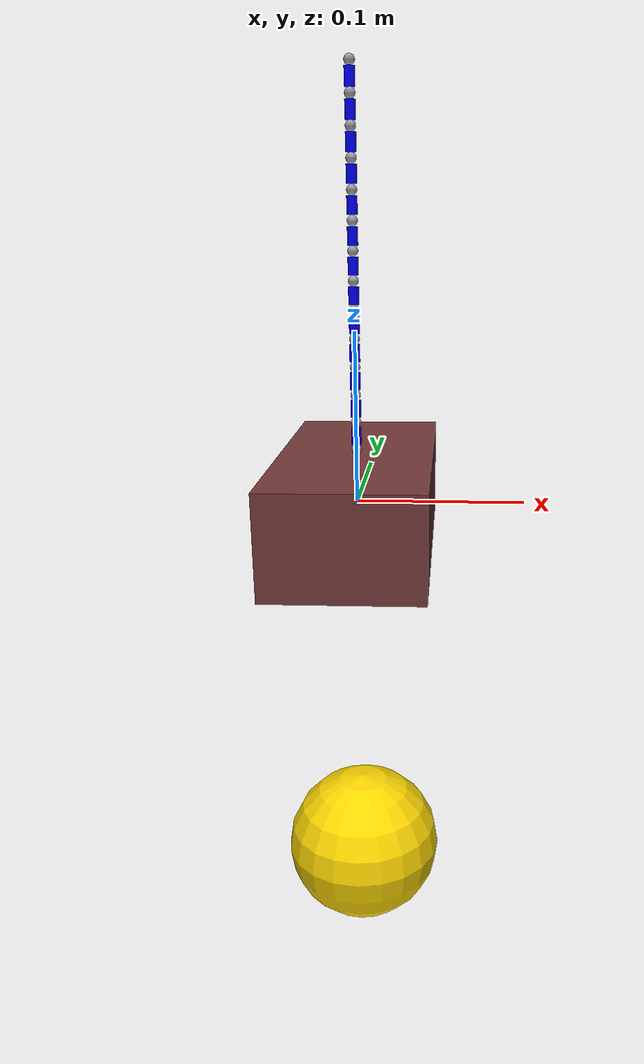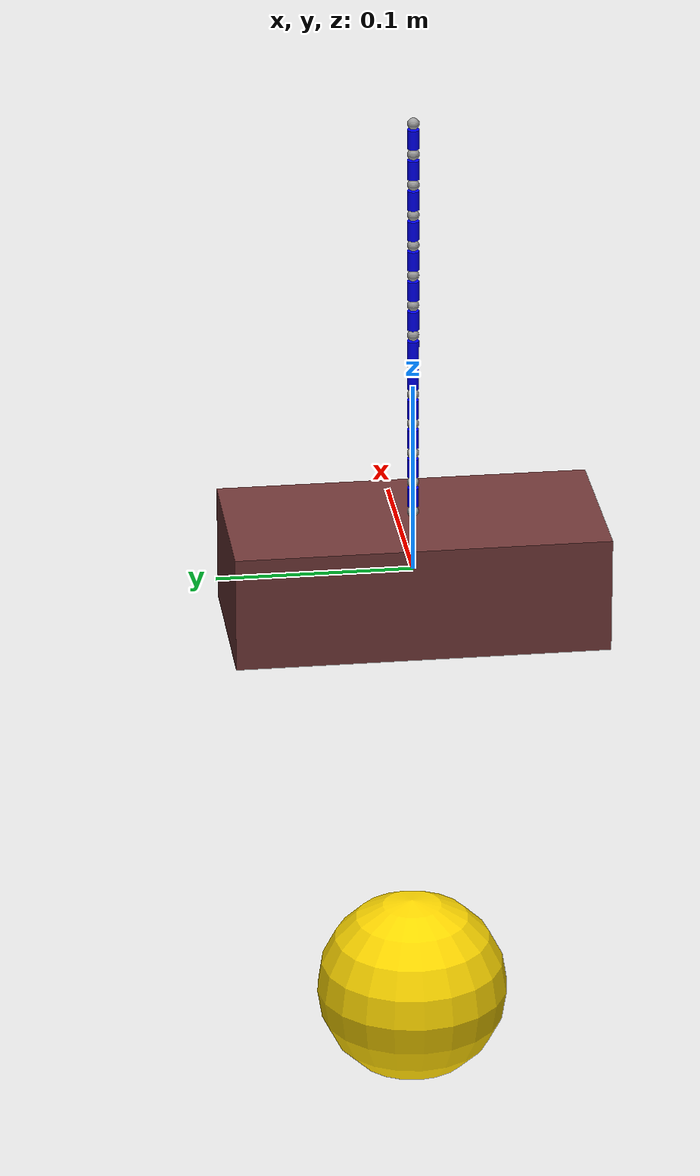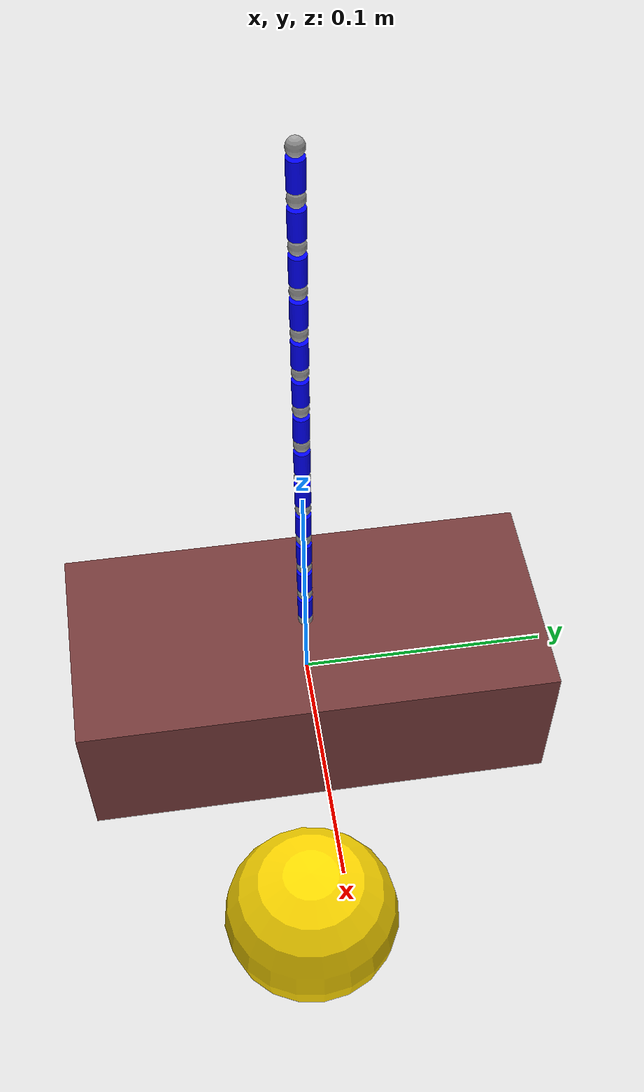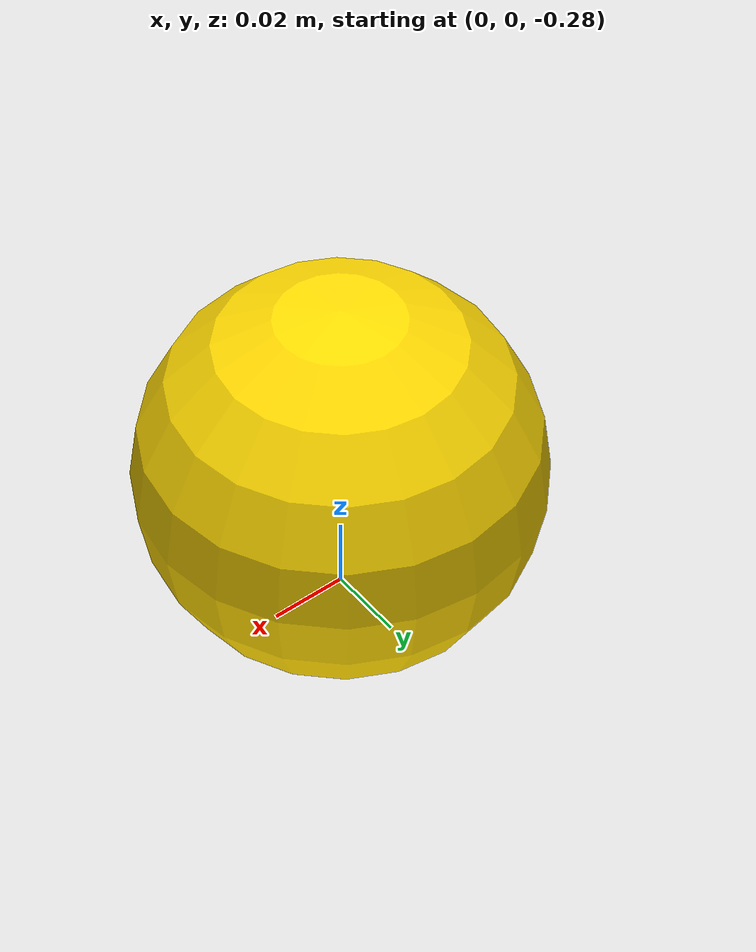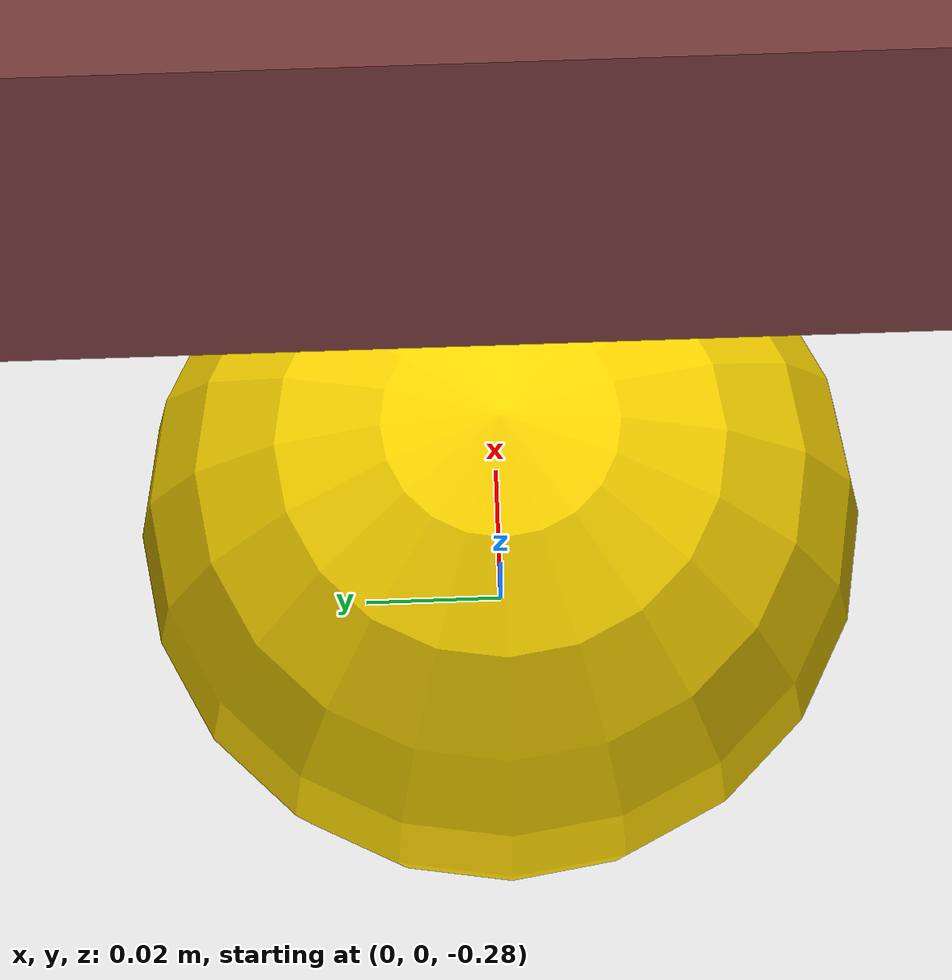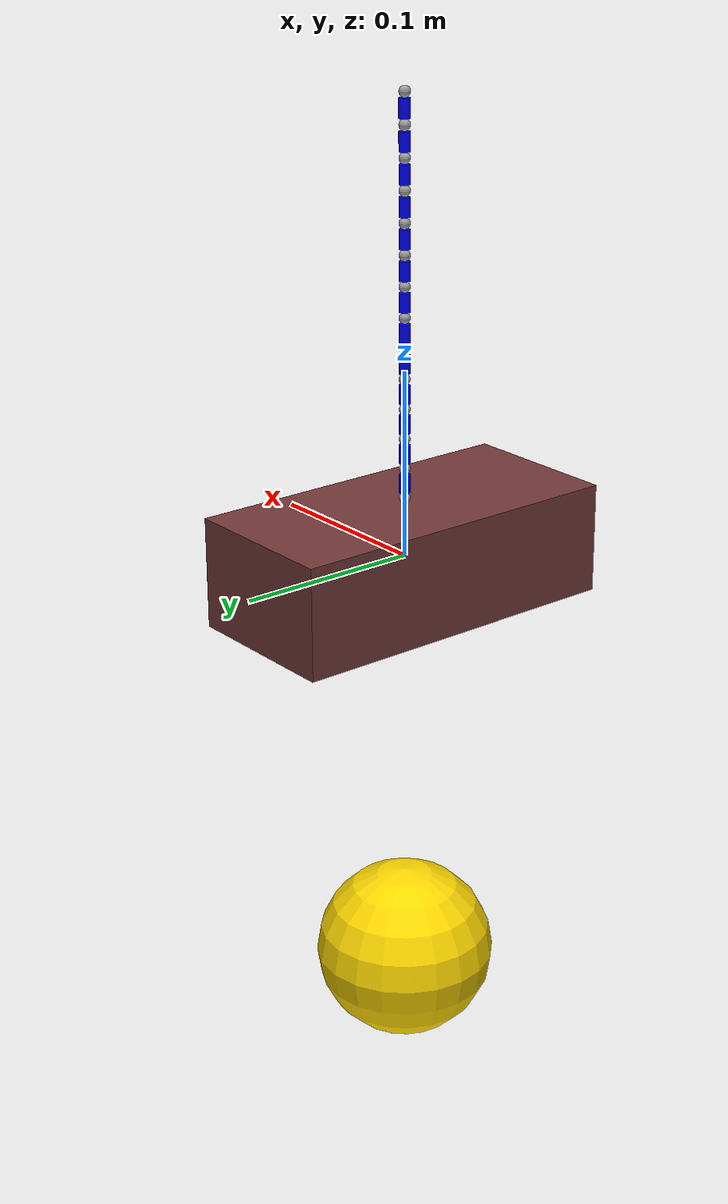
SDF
<sdf version='1.11'>
  <model name='mark2'>
    <joint name='fixed_to_world' type='fixed'>
      <pose relative_to='__model__'>0 0 0 3.1415 0 0</pose>
      <parent>world</parent>
      <child>base_link</child>
    </joint>
    <link name='base_link'>
      <pose relative_to='fixed_to_world'>0 0 0 0 0 0</pose>
      <inertial>
        <pose>0 0 0 0 0 0</pose>
        <mass>5</mass>
        <inertia>
          <ixx>8.3e-04</ixx>
          <ixy>0</ixy>
          <ixz>0</ixz>
          <iyy>8.3e-04</iyy>
          <iyz>0</iyz>
          <izz>1.3e-03</izz>
        </inertia>
      </inertial>
      <collision name='base_link_collision'>
        <pose>0 0 0 0 0 0</pose>
        <geometry>
          <box>
            <size>0.09 0.19 0.06</size>
          </box>
        </geometry>
        <surface>
          <contact>
            <ode/>
          </contact>
          <friction>
            <ode/>
          </friction>
        </surface>
      </collision>
      <visual name='base_link_visual'>
        <pose>0 0 0 0 0 0</pose>
        <geometry>
          <box>
            <size>0.09 0.19 0.06</size>
          </box>
        </geometry>
        <material>
          <diffuse>0.447 0.220 0.220 1</diffuse>
          <ambient>0.36 0.18 0.18 1</ambient>
        </material>
      </visual>

    </link>
    <joint name='base_link_to_segment_1_sphere' type='revolute'>
      <pose relative_to='base_link'>0 0 -0.016 0 0 0</pose>
      <parent>base_link</parent>
      <child>segment_1_sphere</child>
      <axis>
        <xyz>0 1 0</xyz>
        <limit>
          <lower>-3.14</lower>
          <upper>3.14</upper>
          <effort>10</effort>
          <velocity>3</velocity>
        </limit>
        <dynamics>
          <damping>1</damping>
          <friction>0</friction>
          <spring_reference>0</spring_reference>
          <spring_stiffness>0</spring_stiffness>
        </dynamics>
      </axis>
    </joint>
    <link name='segment_1_sphere'>
      <pose relative_to='base_link_to_segment_1_sphere'>0 0 0 0 0 0</pose>
      <inertial>
        <pose>0 0 0 0 0 0</pose>
        <mass>1.13e-4</mass>
        <inertia>
          <ixx>4.1e-10</ixx>
          <ixy>0</ixy>
          <ixz>0</ixz>
          <iyy>4.1e-10</iyy>
          <iyz>0</iyz>
          <izz>4.1e-10</izz>
        </inertia>
      </inertial>
      <collision name='segment_1_sphere_collision'>
        <pose>0 0 0 0 0 0</pose>
        <geometry>
          <sphere>
            <radius>0.003</radius>
          </sphere>
        </geometry>
        <surface>
          <contact>
            <ode/>
          </contact>
          <friction>
            <ode/>
          </friction>
        </surface>
      </collision>
      <visual name='segment_1_sphere_visual'>
        <pose>0 0 0 0 0 0</pose>
        <geometry>
          <sphere>
            <radius>0.003</radius>
          </sphere>
        </geometry>
        <material>
          <diffuse>0.625 0.625 0.625 1</diffuse>
          <ambient>0.625 0.625 0.625 1</ambient>
        </material>
      </visual>

    </link>
    <joint name='segment_1_sphere_to_cylinder' type='revolute'>
      <pose relative_to='segment_1_sphere'>0 0 0 0 0 0</pose>
      <parent>segment_1_sphere</parent>
      <child>segment_1_cylinder</child>
      <axis>
        <xyz>1 0 0</xyz>
        <limit>
          <lower>-3.14</lower>
          <upper>3.14</upper>
          <effort>10</effort>
          <velocity>3</velocity>
        </limit>
        <dynamics>
          <damping>1</damping>
          <friction>0</friction>
          <spring_reference>0</spring_reference>
          <spring_stiffness>0</spring_stiffness>
        </dynamics>
      </axis>
    </joint>
    <link name='segment_1_cylinder'>
      <pose relative_to='segment_1_sphere_to_cylinder'>0 0 0 0 0 0</pose>
      <inertial>
        <pose>0 0 -0.008 0 0 0</pose>
        <mass>2.83e-4</mass>
        <inertia>
          <ixx>3.0e-09</ixx>
          <ixy>0</ixy>
          <ixz>0</ixz>
          <iyy>3.0e-09</iyy>
          <iyz>0</iyz>
          <izz>1.3e-09</izz>
        </inertia>
      </inertial>
      <collision name='segment_1_cylinder_collision'>
        <pose>0 0 -0.008 0 0 0</pose>
        <geometry>
          <cylinder>
            <length>0.01</length>
            <radius>0.003</radius>
          </cylinder>
        </geometry>
        <surface>
          <contact>
            <ode/>
          </contact>
          <friction>
            <ode/>
          </friction>
        </surface>
      </collision>
      <visual name='segment_1_cylinder_visual'>
        <pose>0 0 -0.008 0 0 0</pose>
        <geometry>
          <cylinder>
            <length>0.01</length>
            <radius>0.003</radius>
          </cylinder>
        </geometry>
        <material>
          <diffuse>0 0 1 1</diffuse>
          <ambient>0 0 1 1</ambient>
        </material>
      </visual>

    </link>
    <joint name='segment_1_cylinder_to_segment_2_sphere' type='revolute'>
      <pose relative_to='segment_1_cylinder'>0 0 -0.016 0 0 0</pose>
      <parent>segment_1_cylinder</parent>
      <child>segment_2_sphere</child>
      <axis>
        <xyz>0 1 0</xyz>
        <limit>
          <lower>-3.14</lower>
          <upper>3.14</upper>
          <effort>10</effort>
          <velocity>3</velocity>
        </limit>
        <dynamics>
          <damping>1</damping>
          <friction>0</friction>
          <spring_reference>0</spring_reference>
          <spring_stiffness>0</spring_stiffness>
        </dynamics>
      </axis>
    </joint>
    <link name='segment_2_sphere'>
      <pose relative_to='segment_1_cylinder_to_segment_2_sphere'>0 0 0 0 0 0</pose>
      <inertial>
        <pose>0 0 0 0 0 0</pose>
        <mass>1.13e-4</mass>
        <inertia>
          <ixx>4.1e-10</ixx>
          <ixy>0</ixy>
          <ixz>0</ixz>
          <iyy>4.1e-10</iyy>
          <iyz>0</iyz>
          <izz>4.1e-10</izz>
        </inertia>
      </inertial>
      <collision name='segment_2_sphere_collision'>
        <pose>0 0 0 0 0 0</pose>
        <geometry>
          <sphere>
            <radius>0.003</radius>
          </sphere>
        </geometry>
        <surface>
          <contact>
            <ode/>
          </contact>
          <friction>
            <ode/>
          </friction>
        </surface>
      </collision>
      <visual name='segment_2_sphere_visual'>
        <pose>0 0 0 0 0 0</pose>
        <geometry>
          <sphere>
            <radius>0.003</radius>
          </sphere>
        </geometry>
        <material>
          <diffuse>0.625 0.625 0.625 1</diffuse>
          <ambient>0.625 0.625 0.625 1</ambient>
        </material>
      </visual>

    </link>
    <joint name='segment_2_sphere_to_cylinder' type='revolute'>
      <pose relative_to='segment_2_sphere'>0 0 0 0 0 0</pose>
      <parent>segment_2_sphere</parent>
      <child>segment_2_cylinder</child>
      <axis>
        <xyz>1 0 0</xyz>
        <limit>
          <lower>-3.14</lower>
          <upper>3.14</upper>
          <effort>10</effort>
          <velocity>3</velocity>
        </limit>
        <dynamics>
          <damping>1</damping>
          <friction>0</friction>
          <spring_reference>0</spring_reference>
          <spring_stiffness>0</spring_stiffness>
        </dynamics>
      </axis>
    </joint>
    <link name='segment_2_cylinder'>
      <pose relative_to='segment_2_sphere_to_cylinder'>0 0 0 0 0 0</pose>
      <inertial>
        <pose>0 0 -0.008 0 0 0</pose>
        <mass>2.83e-4</mass>
        <inertia>
          <ixx>3.0e-09</ixx>
          <ixy>0</ixy>
          <ixz>0</ixz>
          <iyy>3.0e-09</iyy>
          <iyz>0</iyz>
          <izz>1.3e-09</izz>
        </inertia>
      </inertial>
      <collision name='segment_2_cylinder_collision'>
        <pose>0 0 -0.008 0 0 0</pose>
        <geometry>
          <cylinder>
            <length>0.01</length>
            <radius>0.003</radius>
          </cylinder>
        </geometry>
        <surface>
          <contact>
            <ode/>
          </contact>
          <friction>
            <ode/>
          </friction>
        </surface>
      </collision>
      <visual name='segment_2_cylinder_visual'>
        <pose>0 0 -0.008 0 0 0</pose>
        <geometry>
          <cylinder>
            <length>0.01</length>
            <radius>0.003</radius>
          </cylinder>
        </geometry>
        <material>
          <diffuse>0 0 1 1</diffuse>
          <ambient>0 0 1 1</ambient>
        </material>
      </visual>

    </link>
    <joint name='segment_2_cylinder_to_segment_3_sphere' type='revolute'>
      <pose relative_to='segment_2_cylinder'>0 0 -0.016 0 0 0</pose>
      <parent>segment_2_cylinder</parent>
      <child>segment_3_sphere</child>
      <axis>
        <xyz>0 1 0</xyz>
        <limit>
          <lower>-3.14</lower>
          <upper>3.14</upper>
          <effort>10</effort>
          <velocity>3</velocity>
        </limit>
        <dynamics>
          <damping>1</damping>
          <friction>0</friction>
          <spring_reference>0</spring_reference>
          <spring_stiffness>0</spring_stiffness>
        </dynamics>
      </axis>
    </joint>
    <link name='segment_3_sphere'>
      <pose relative_to='segment_2_cylinder_to_segment_3_sphere'>0 0 0 0 0 0</pose>
      <inertial>
        <pose>0 0 0 0 0 0</pose>
        <mass>1.13e-4</mass>
        <inertia>
          <ixx>4.1e-10</ixx>
          <ixy>0</ixy>
          <ixz>0</ixz>
          <iyy>4.1e-10</iyy>
          <iyz>0</iyz>
          <izz>4.1e-10</izz>
        </inertia>
      </inertial>
      <collision name='segment_3_sphere_collision'>
        <pose>0 0 0 0 0 0</pose>
        <geometry>
          <sphere>
            <radius>0.003</radius>
          </sphere>
        </geometry>
        <surface>
          <contact>
            <ode/>
          </contact>
          <friction>
            <ode/>
          </friction>
        </surface>
      </collision>
      <visual name='segment_3_sphere_visual'>
        <pose>0 0 0 0 0 0</pose>
        <geometry>
          <sphere>
            <radius>0.003</radius>
          </sphere>
        </geometry>
        <material>
          <diffuse>0.625 0.625 0.625 1</diffuse>
          <ambient>0.625 0.625 0.625 1</ambient>
        </material>
      </visual>

    </link>
    <joint name='segment_3_sphere_to_cylinder' type='revolute'>
      <pose relative_to='segment_3_sphere'>0 0 0 0 0 0</pose>
      <parent>segment_3_sphere</parent>
      <child>segment_3_cylinder</child>
      <axis>
        <xyz>1 0 0</xyz>
        <limit>
          <lower>-3.14</lower>
          <upper>3.14</upper>
          <effort>10</effort>
          <velocity>3</velocity>
        </limit>
        <dynamics>
          <damping>1</damping>
          <friction>0</friction>
          <spring_reference>0</spring_reference>
          <spring_stiffness>0</spring_stiffness>
        </dynamics>
      </axis>
    </joint>
    <link name='segment_3_cylinder'>
      <pose relative_to='segment_3_sphere_to_cylinder'>0 0 0 0 0 0</pose>
      <inertial>
        <pose>0 0 -0.008 0 0 0</pose>
        <mass>2.83e-4</mass>
        <inertia>
          <ixx>3.0e-09</ixx>
          <ixy>0</ixy>
          <ixz>0</ixz>
          <iyy>3.0e-09</iyy>
          <iyz>0</iyz>
          <izz>1.3e-09</izz>
        </inertia>
      </inertial>
      <collision name='segment_3_cylinder_collision'>
        <pose>0 0 -0.008 0 0 0</pose>
        <geometry>
          <cylinder>
            <length>0.01</length>
            <radius>0.003</radius>
          </cylinder>
        </geometry>
        <surface>
          <contact>
            <ode/>
          </contact>
          <friction>
            <ode/>
          </friction>
        </surface>
      </collision>
      <visual name='segment_3_cylinder_visual'>
        <pose>0 0 -0.008 0 0 0</pose>
        <geometry>
          <cylinder>
            <length>0.01</length>
            <radius>0.003</radius>
          </cylinder>
        </geometry>
        <material>
          <diffuse>0 0 1 1</diffuse>
          <ambient>0 0 1 1</ambient>
        </material>
      </visual>

    </link>
    <joint name='segment_3_cylinder_to_segment_4_sphere' type='revolute'>
      <pose relative_to='segment_3_cylinder'>0 0 -0.016 0 0 0</pose>
      <parent>segment_3_cylinder</parent>
      <child>segment_4_sphere</child>
      <axis>
        <xyz>0 1 0</xyz>
        <limit>
          <lower>-3.14</lower>
          <upper>3.14</upper>
          <effort>10</effort>
          <velocity>3</velocity>
        </limit>
        <dynamics>
          <damping>1</damping>
          <friction>0</friction>
          <spring_reference>0</spring_reference>
          <spring_stiffness>0</spring_stiffness>
        </dynamics>
      </axis>
    </joint>
    <link name='segment_4_sphere'>
      <pose relative_to='segment_3_cylinder_to_segment_4_sphere'>0 0 0 0 0 0</pose>
      <inertial>
        <pose>0 0 0 0 0 0</pose>
        <mass>1.13e-4</mass>
        <inertia>
          <ixx>4.1e-10</ixx>
          <ixy>0</ixy>
          <ixz>0</ixz>
          <iyy>4.1e-10</iyy>
          <iyz>0</iyz>
          <izz>4.1e-10</izz>
        </inertia>
      </inertial>
      <collision name='segment_4_sphere_collision'>
        <pose>0 0 0 0 0 0</pose>
        <geometry>
          <sphere>
            <radius>0.003</radius>
          </sphere>
        </geometry>
        <surface>
          <contact>
            <ode/>
          </contact>
          <friction>
            <ode/>
          </friction>
        </surface>
      </collision>
      <visual name='segment_4_sphere_visual'>
        <pose>0 0 0 0 0 0</pose>
        <geometry>
          <sphere>
            <radius>0.003</radius>
          </sphere>
        </geometry>
        <material>
          <diffuse>0.625 0.625 0.625 1</diffuse>
          <ambient>0.625 0.625 0.625 1</ambient>
        </material>
      </visual>

    </link>
    <joint name='segment_4_sphere_to_cylinder' type='revolute'>
      <pose relative_to='segment_4_sphere'>0 0 0 0 0 0</pose>
      <parent>segment_4_sphere</parent>
      <child>segment_4_cylinder</child>
      <axis>
        <xyz>1 0 0</xyz>
        <limit>
          <lower>-3.14</lower>
          <upper>3.14</upper>
          <effort>10</effort>
          <velocity>3</velocity>
        </limit>
        <dynamics>
          <damping>1</damping>
          <friction>0</friction>
          <spring_reference>0</spring_reference>
          <spring_stiffness>0</spring_stiffness>
        </dynamics>
      </axis>
    </joint>
    <link name='segment_4_cylinder'>
      <pose relative_to='segment_4_sphere_to_cylinder'>0 0 0 0 0 0</pose>
      <inertial>
        <pose>0 0 -0.008 0 0 0</pose>
        <mass>2.83e-4</mass>
        <inertia>
          <ixx>3.0e-09</ixx>
          <ixy>0</ixy>
          <ixz>0</ixz>
          <iyy>3.0e-09</iyy>
          <iyz>0</iyz>
          <izz>1.3e-09</izz>
        </inertia>
      </inertial>
      <collision name='segment_4_cylinder_collision'>
        <pose>0 0 -0.008 0 0 0</pose>
        <geometry>
          <cylinder>
            <length>0.01</length>
            <radius>0.003</radius>
          </cylinder>
        </geometry>
        <surface>
          <contact>
            <ode/>
          </contact>
          <friction>
            <ode/>
          </friction>
        </surface>
      </collision>
      <visual name='segment_4_cylinder_visual'>
        <pose>0 0 -0.008 0 0 0</pose>
        <geometry>
          <cylinder>
            <length>0.01</length>
            <radius>0.003</radius>
          </cylinder>
        </geometry>
        <material>
          <diffuse>0 0 1 1</diffuse>
          <ambient>0 0 1 1</ambient>
        </material>
      </visual>

    </link>
    <joint name='segment_4_cylinder_to_segment_5_sphere' type='revolute'>
      <pose relative_to='segment_4_cylinder'>0 0 -0.016 0 0 0</pose>
      <parent>segment_4_cylinder</parent>
      <child>segment_5_sphere</child>
      <axis>
        <xyz>0 1 0</xyz>
        <limit>
          <lower>-3.14</lower>
          <upper>3.14</upper>
          <effort>10</effort>
          <velocity>3</velocity>
        </limit>
        <dynamics>
          <damping>1</damping>
          <friction>0</friction>
          <spring_reference>0</spring_reference>
          <spring_stiffness>0</spring_stiffness>
        </dynamics>
      </axis>
    </joint>
    <link name='segment_5_sphere'>
      <pose relative_to='segment_4_cylinder_to_segment_5_sphere'>0 0 0 0 0 0</pose>
      <inertial>
        <pose>0 0 0 0 0 0</pose>
        <mass>1.13e-4</mass>
        <inertia>
          <ixx>4.1e-10</ixx>
          <ixy>0</ixy>
          <ixz>0</ixz>
          <iyy>4.1e-10</iyy>
          <iyz>0</iyz>
          <izz>4.1e-10</izz>
        </inertia>
      </inertial>
      <collision name='segment_5_sphere_collision'>
        <pose>0 0 0 0 0 0</pose>
        <geometry>
          <sphere>
            <radius>0.003</radius>
          </sphere>
        </geometry>
        <surface>
          <contact>
            <ode/>
          </contact>
          <friction>
            <ode/>
          </friction>
        </surface>
      </collision>
      <visual name='segment_5_sphere_visual'>
        <pose>0 0 0 0 0 0</pose>
        <geometry>
          <sphere>
            <radius>0.003</radius>
          </sphere>
        </geometry>
        <material>
          <diffuse>0.625 0.625 0.625 1</diffuse>
          <ambient>0.625 0.625 0.625 1</ambient>
        </material>
      </visual>

    </link>
    <joint name='segment_5_sphere_to_cylinder' type='revolute'>
      <pose relative_to='segment_5_sphere'>0 0 0 0 0 0</pose>
      <parent>segment_5_sphere</parent>
      <child>segment_5_cylinder</child>
      <axis>
        <xyz>1 0 0</xyz>
        <limit>
          <lower>-3.14</lower>
          <upper>3.14</upper>
          <effort>10</effort>
          <velocity>3</velocity>
        </limit>
        <dynamics>
          <damping>1</damping>
          <friction>0</friction>
          <spring_reference>0</spring_reference>
          <spring_stiffness>0</spring_stiffness>
        </dynamics>
      </axis>
    </joint>
    <link name='segment_5_cylinder'>
      <pose relative_to='segment_5_sphere_to_cylinder'>0 0 0 0 0 0</pose>
      <inertial>
        <pose>0 0 -0.008 0 0 0</pose>
        <mass>2.83e-4</mass>
        <inertia>
          <ixx>3.0e-09</ixx>
          <ixy>0</ixy>
          <ixz>0</ixz>
          <iyy>3.0e-09</iyy>
          <iyz>0</iyz>
          <izz>1.3e-09</izz>
        </inertia>
      </inertial>
      <collision name='segment_5_cylinder_collision'>
        <pose>0 0 -0.008 0 0 0</pose>
        <geometry>
          <cylinder>
            <length>0.01</length>
            <radius>0.003</radius>
          </cylinder>
        </geometry>
        <surface>
          <contact>
            <ode/>
          </contact>
          <friction>
            <ode/>
          </friction>
        </surface>
      </collision>
      <visual name='segment_5_cylinder_visual'>
        <pose>0 0 -0.008 0 0 0</pose>
        <geometry>
          <cylinder>
            <length>0.01</length>
            <radius>0.003</radius>
          </cylinder>
        </geometry>
        <material>
          <diffuse>0 0 1 1</diffuse>
          <ambient>0 0 1 1</ambient>
        </material>
      </visual>

    </link>
    <joint name='segment_5_cylinder_to_segment_6_sphere' type='revolute'>
      <pose relative_to='segment_5_cylinder'>0 0 -0.016 0 0 0</pose>
      <parent>segment_5_cylinder</parent>
      <child>segment_6_sphere</child>
      <axis>
        <xyz>0 1 0</xyz>
        <limit>
          <lower>-3.14</lower>
          <upper>3.14</upper>
          <effort>10</effort>
          <velocity>3</velocity>
        </limit>
        <dynamics>
          <damping>1</damping>
          <friction>0</friction>
          <spring_reference>0</spring_reference>
          <spring_stiffness>0</spring_stiffness>
        </dynamics>
      </axis>
    </joint>
    <link name='segment_6_sphere'>
      <pose relative_to='segment_5_cylinder_to_segment_6_sphere'>0 0 0 0 0 0</pose>
      <inertial>
        <pose>0 0 0 0 0 0</pose>
        <mass>1.13e-4</mass>
        <inertia>
          <ixx>4.1e-10</ixx>
          <ixy>0</ixy>
          <ixz>0</ixz>
          <iyy>4.1e-10</iyy>
          <iyz>0</iyz>
          <izz>4.1e-10</izz>
        </inertia>
      </inertial>
      <collision name='segment_6_sphere_collision'>
        <pose>0 0 0 0 0 0</pose>
        <geometry>
          <sphere>
            <radius>0.003</radius>
          </sphere>
        </geometry>
        <surface>
          <contact>
            <ode/>
          </contact>
          <friction>
            <ode/>
          </friction>
        </surface>
      </collision>
      <visual name='segment_6_sphere_visual'>
        <pose>0 0 0 0 0 0</pose>
        <geometry>
          <sphere>
            <radius>0.003</radius>
          </sphere>
        </geometry>
        <material>
          <diffuse>0.625 0.625 0.625 1</diffuse>
          <ambient>0.625 0.625 0.625 1</ambient>
        </material>
      </visual>

    </link>
    <joint name='segment_6_sphere_to_cylinder' type='revolute'>
      <pose relative_to='segment_6_sphere'>0 0 0 0 0 0</pose>
      <parent>segment_6_sphere</parent>
      <child>segment_6_cylinder</child>
      <axis>
        <xyz>1 0 0</xyz>
        <limit>
          <lower>-3.14</lower>
          <upper>3.14</upper>
          <effort>10</effort>
          <velocity>3</velocity>
        </limit>
        <dynamics>
          <damping>1</damping>
          <friction>0</friction>
          <spring_reference>0</spring_reference>
          <spring_stiffness>0</spring_stiffness>
        </dynamics>
      </axis>
    </joint>
    <link name='segment_6_cylinder'>
      <pose relative_to='segment_6_sphere_to_cylinder'>0 0 0 0 0 0</pose>
      <inertial>
        <pose>0 0 -0.008 0 0 0</pose>
        <mass>2.83e-4</mass>
        <inertia>
          <ixx>3.0e-09</ixx>
          <ixy>0</ixy>
          <ixz>0</ixz>
          <iyy>3.0e-09</iyy>
          <iyz>0</iyz>
          <izz>1.3e-09</izz>
        </inertia>
      </inertial>
      <collision name='segment_6_cylinder_collision'>
        <pose>0 0 -0.008 0 0 0</pose>
        <geometry>
          <cylinder>
            <length>0.01</length>
            <radius>0.003</radius>
          </cylinder>
        </geometry>
        <surface>
          <contact>
            <ode/>
          </contact>
          <friction>
            <ode/>
          </friction>
        </surface>
      </collision>
      <visual name='segment_6_cylinder_visual'>
        <pose>0 0 -0.008 0 0 0</pose>
        <geometry>
          <cylinder>
            <length>0.01</length>
            <radius>0.003</radius>
          </cylinder>
        </geometry>
        <material>
          <diffuse>0 0 1 1</diffuse>
          <ambient>0 0 1 1</ambient>
        </material>
      </visual>

    </link>
    <joint name='segment_6_cylinder_to_segment_7_sphere' type='revolute'>
      <pose relative_to='segment_6_cylinder'>0 0 -0.016 0 0 0</pose>
      <parent>segment_6_cylinder</parent>
      <child>segment_7_sphere</child>
      <axis>
        <xyz>0 1 0</xyz>
        <limit>
          <lower>-3.14</lower>
          <upper>3.14</upper>
          <effort>10</effort>
          <velocity>3</velocity>
        </limit>
        <dynamics>
          <damping>1</damping>
          <friction>0</friction>
          <spring_reference>0</spring_reference>
          <spring_stiffness>0</spring_stiffness>
        </dynamics>
      </axis>
    </joint>
    <link name='segment_7_sphere'>
      <pose relative_to='segment_6_cylinder_to_segment_7_sphere'>0 0 0 0 0 0</pose>
      <inertial>
        <pose>0 0 0 0 0 0</pose>
        <mass>1.13e-4</mass>
        <inertia>
          <ixx>4.1e-10</ixx>
          <ixy>0</ixy>
          <ixz>0</ixz>
          <iyy>4.1e-10</iyy>
          <iyz>0</iyz>
          <izz>4.1e-10</izz>
        </inertia>
      </inertial>
      <collision name='segment_7_sphere_collision'>
        <pose>0 0 0 0 0 0</pose>
        <geometry>
          <sphere>
            <radius>0.003</radius>
          </sphere>
        </geometry>
        <surface>
          <contact>
            <ode/>
          </contact>
          <friction>
            <ode/>
          </friction>
        </surface>
      </collision>
      <visual name='segment_7_sphere_visual'>
        <pose>0 0 0 0 0 0</pose>
        <geometry>
          <sphere>
            <radius>0.003</radius>
          </sphere>
        </geometry>
        <material>
          <diffuse>0.625 0.625 0.625 1</diffuse>
          <ambient>0.625 0.625 0.625 1</ambient>
        </material>
      </visual>

    </link>
    <joint name='segment_7_sphere_to_cylinder' type='revolute'>
      <pose relative_to='segment_7_sphere'>0 0 0 0 0 0</pose>
      <parent>segment_7_sphere</parent>
      <child>segment_7_cylinder</child>
      <axis>
        <xyz>1 0 0</xyz>
        <limit>
          <lower>-3.14</lower>
          <upper>3.14</upper>
          <effort>10</effort>
          <velocity>3</velocity>
        </limit>
        <dynamics>
          <damping>1</damping>
          <friction>0</friction>
          <spring_reference>0</spring_reference>
          <spring_stiffness>0</spring_stiffness>
        </dynamics>
      </axis>
    </joint>
    <link name='segment_7_cylinder'>
      <pose relative_to='segment_7_sphere_to_cylinder'>0 0 0 0 0 0</pose>
      <inertial>
        <pose>0 0 -0.008 0 0 0</pose>
        <mass>2.83e-4</mass>
        <inertia>
          <ixx>3.0e-09</ixx>
          <ixy>0</ixy>
          <ixz>0</ixz>
          <iyy>3.0e-09</iyy>
          <iyz>0</iyz>
          <izz>1.3e-09</izz>
        </inertia>
      </inertial>
      <collision name='segment_7_cylinder_collision'>
        <pose>0 0 -0.008 0 0 0</pose>
        <geometry>
          <cylinder>
            <length>0.01</length>
            <radius>0.003</radius>
          </cylinder>
        </geometry>
        <surface>
          <contact>
            <ode/>
          </contact>
          <friction>
            <ode/>
          </friction>
        </surface>
      </collision>
      <visual name='segment_7_cylinder_visual'>
        <pose>0 0 -0.008 0 0 0</pose>
        <geometry>
          <cylinder>
            <length>0.01</length>
            <radius>0.003</radius>
          </cylinder>
        </geometry>
        <material>
          <diffuse>0 0 1 1</diffuse>
          <ambient>0 0 1 1</ambient>
        </material>
      </visual>

    </link>
    <joint name='segment_7_cylinder_to_segment_8_sphere' type='revolute'>
      <pose relative_to='segment_7_cylinder'>0 0 -0.016 0 0 0</pose>
      <parent>segment_7_cylinder</parent>
      <child>segment_8_sphere</child>
      <axis>
        <xyz>0 1 0</xyz>
        <limit>
          <lower>-3.14</lower>
          <upper>3.14</upper>
          <effort>10</effort>
          <velocity>3</velocity>
        </limit>
        <dynamics>
          <damping>1</damping>
          <friction>0</friction>
          <spring_reference>0</spring_reference>
          <spring_stiffness>0</spring_stiffness>
        </dynamics>
      </axis>
    </joint>
    <link name='segment_8_sphere'>
      <pose relative_to='segment_7_cylinder_to_segment_8_sphere'>0 0 0 0 0 0</pose>
      <inertial>
        <pose>0 0 0 0 0 0</pose>
        <mass>1.13e-4</mass>
        <inertia>
          <ixx>4.1e-10</ixx>
          <ixy>0</ixy>
          <ixz>0</ixz>
          <iyy>4.1e-10</iyy>
          <iyz>0</iyz>
          <izz>4.1e-10</izz>
        </inertia>
      </inertial>
      <collision name='segment_8_sphere_collision'>
        <pose>0 0 0 0 0 0</pose>
        <geometry>
          <sphere>
            <radius>0.003</radius>
          </sphere>
        </geometry>
        <surface>
          <contact>
            <ode/>
          </contact>
          <friction>
            <ode/>
          </friction>
        </surface>
      </collision>
      <visual name='segment_8_sphere_visual'>
        <pose>0 0 0 0 0 0</pose>
        <geometry>
          <sphere>
            <radius>0.003</radius>
          </sphere>
        </geometry>
        <material>
          <diffuse>0.625 0.625 0.625 1</diffuse>
          <ambient>0.625 0.625 0.625 1</ambient>
        </material>
      </visual>

    </link>
    <joint name='segment_8_sphere_to_cylinder' type='revolute'>
      <pose relative_to='segment_8_sphere'>0 0 0 0 0 0</pose>
      <parent>segment_8_sphere</parent>
      <child>segment_8_cylinder</child>
      <axis>
        <xyz>1 0 0</xyz>
        <limit>
          <lower>-3.14</lower>
          <upper>3.14</upper>
          <effort>10</effort>
          <velocity>3</velocity>
        </limit>
        <dynamics>
          <damping>1</damping>
          <friction>0</friction>
          <spring_reference>0</spring_reference>
          <spring_stiffness>0</spring_stiffness>
        </dynamics>
      </axis>
    </joint>
    <link name='segment_8_cylinder'>
      <pose relative_to='segment_8_sphere_to_cylinder'>0 0 0 0 0 0</pose>
      <inertial>
        <pose>0 0 -0.008 0 0 0</pose>
        <mass>2.83e-4</mass>
        <inertia>
          <ixx>3.0e-09</ixx>
          <ixy>0</ixy>
          <ixz>0</ixz>
          <iyy>3.0e-09</iyy>
          <iyz>0</iyz>
          <izz>1.3e-09</izz>
        </inertia>
      </inertial>
      <collision name='segment_8_cylinder_collision'>
        <pose>0 0 -0.008 0 0 0</pose>
        <geometry>
          <cylinder>
            <length>0.01</length>
            <radius>0.003</radius>
          </cylinder>
        </geometry>
        <surface>
          <contact>
            <ode/>
          </contact>
          <friction>
            <ode/>
          </friction>
        </surface>
      </collision>
      <visual name='segment_8_cylinder_visual'>
        <pose>0 0 -0.008 0 0 0</pose>
        <geometry>
          <cylinder>
            <length>0.01</length>
            <radius>0.003</radius>
          </cylinder>
        </geometry>
        <material>
          <diffuse>0 0 1 1</diffuse>
          <ambient>0 0 1 1</ambient>
        </material>
      </visual>

    </link>
    <joint name='segment_8_cylinder_to_segment_9_sphere' type='revolute'>
      <pose relative_to='segment_8_cylinder'>0 0 -0.016 0 0 0</pose>
      <parent>segment_8_cylinder</parent>
      <child>segment_9_sphere</child>
      <axis>
        <xyz>0 1 0</xyz>
        <limit>
          <lower>-3.14</lower>
          <upper>3.14</upper>
          <effort>10</effort>
          <velocity>3</velocity>
        </limit>
        <dynamics>
          <damping>1</damping>
          <friction>0</friction>
          <spring_reference>0</spring_reference>
          <spring_stiffness>0</spring_stiffness>
        </dynamics>
      </axis>
    </joint>
    <link name='segment_9_sphere'>
      <pose relative_to='segment_8_cylinder_to_segment_9_sphere'>0 0 0 0 0 0</pose>
      <inertial>
        <pose>0 0 0 0 0 0</pose>
        <mass>1.13e-4</mass>
        <inertia>
          <ixx>4.1e-10</ixx>
          <ixy>0</ixy>
          <ixz>0</ixz>
          <iyy>4.1e-10</iyy>
          <iyz>0</iyz>
          <izz>4.1e-10</izz>
        </inertia>
      </inertial>
      <collision name='segment_9_sphere_collision'>
        <pose>0 0 0 0 0 0</pose>
        <geometry>
          <sphere>
            <radius>0.003</radius>
          </sphere>
        </geometry>
        <surface>
          <contact>
            <ode/>
          </contact>
          <friction>
            <ode/>
          </friction>
        </surface>
      </collision>
      <visual name='segment_9_sphere_visual'>
        <pose>0 0 0 0 0 0</pose>
        <geometry>
          <sphere>
            <radius>0.003</radius>
          </sphere>
        </geometry>
        <material>
          <diffuse>0.625 0.625 0.625 1</diffuse>
          <ambient>0.625 0.625 0.625 1</ambient>
        </material>
      </visual>

    </link>
    <joint name='segment_9_sphere_to_cylinder' type='revolute'>
      <pose relative_to='segment_9_sphere'>0 0 0 0 0 0</pose>
      <parent>segment_9_sphere</parent>
      <child>segment_9_cylinder</child>
      <axis>
        <xyz>1 0 0</xyz>
        <limit>
          <lower>-3.14</lower>
          <upper>3.14</upper>
          <effort>10</effort>
          <velocity>3</velocity>
        </limit>
        <dynamics>
          <damping>1</damping>
          <friction>0</friction>
          <spring_reference>0</spring_reference>
          <spring_stiffness>0</spring_stiffness>
        </dynamics>
      </axis>
    </joint>
    <link name='segment_9_cylinder'>
      <pose relative_to='segment_9_sphere_to_cylinder'>0 0 0 0 0 0</pose>
      <inertial>
        <pose>0 0 -0.008 0 0 0</pose>
        <mass>2.83e-4</mass>
        <inertia>
          <ixx>3.0e-09</ixx>
          <ixy>0</ixy>
          <ixz>0</ixz>
          <iyy>3.0e-09</iyy>
          <iyz>0</iyz>
          <izz>1.3e-09</izz>
        </inertia>
      </inertial>
      <collision name='segment_9_cylinder_collision'>
        <pose>0 0 -0.008 0 0 0</pose>
        <geometry>
          <cylinder>
            <length>0.01</length>
            <radius>0.003</radius>
          </cylinder>
        </geometry>
        <surface>
          <contact>
            <ode/>
          </contact>
          <friction>
            <ode/>
          </friction>
        </surface>
      </collision>
      <visual name='segment_9_cylinder_visual'>
        <pose>0 0 -0.008 0 0 0</pose>
        <geometry>
          <cylinder>
            <length>0.01</length>
            <radius>0.003</radius>
          </cylinder>
        </geometry>
        <material>
          <diffuse>0 0 1 1</diffuse>
          <ambient>0 0 1 1</ambient>
        </material>
      </visual>

    </link>
    <joint name='segment_9_cylinder_to_segment_10_sphere' type='revolute'>
      <pose relative_to='segment_9_cylinder'>0 0 -0.016 0 0 0</pose>
      <parent>segment_9_cylinder</parent>
      <child>segment_10_sphere</child>
      <axis>
        <xyz>0 1 0</xyz>
        <limit>
          <lower>-3.14</lower>
          <upper>3.14</upper>
          <effort>10</effort>
          <velocity>3</velocity>
        </limit>
        <dynamics>
          <damping>1</damping>
          <friction>0</friction>
          <spring_reference>0</spring_reference>
          <spring_stiffness>0</spring_stiffness>
        </dynamics>
      </axis>
    </joint>
    <link name='segment_10_sphere'>
      <pose relative_to='segment_9_cylinder_to_segment_10_sphere'>0 0 0 0 0 0</pose>
      <inertial>
        <pose>0 0 0 0 0 0</pose>
        <mass>1.13e-4</mass>
        <inertia>
          <ixx>4.1e-10</ixx>
          <ixy>0</ixy>
          <ixz>0</ixz>
          <iyy>4.1e-10</iyy>
          <iyz>0</iyz>
          <izz>4.1e-10</izz>
        </inertia>
      </inertial>
      <collision name='segment_10_sphere_collision'>
        <pose>0 0 0 0 0 0</pose>
        <geometry>
          <sphere>
            <radius>0.003</radius>
          </sphere>
        </geometry>
        <surface>
          <contact>
            <ode/>
          </contact>
          <friction>
            <ode/>
          </friction>
        </surface>
      </collision>
      <visual name='segment_10_sphere_visual'>
        <pose>0 0 0 0 0 0</pose>
        <geometry>
          <sphere>
            <radius>0.003</radius>
          </sphere>
        </geometry>
        <material>
          <diffuse>0.625 0.625 0.625 1</diffuse>
          <ambient>0.625 0.625 0.625 1</ambient>
        </material>
      </visual>

    </link>
    <joint name='segment_10_sphere_to_cylinder' type='revolute'>
      <pose relative_to='segment_10_sphere'>0 0 0 0 0 0</pose>
      <parent>segment_10_sphere</parent>
      <child>segment_10_cylinder</child>
      <axis>
        <xyz>1 0 0</xyz>
        <limit>
          <lower>-3.14</lower>
          <upper>3.14</upper>
          <effort>10</effort>
          <velocity>3</velocity>
        </limit>
        <dynamics>
          <damping>1</damping>
          <friction>0</friction>
          <spring_reference>0</spring_reference>
          <spring_stiffness>0</spring_stiffness>
        </dynamics>
      </axis>
    </joint>
    <link name='segment_10_cylinder'>
      <pose relative_to='segment_10_sphere_to_cylinder'>0 0 0 0 0 0</pose>
      <inertial>
        <pose>0 0 -0.008 0 0 0</pose>
        <mass>2.83e-4</mass>
        <inertia>
          <ixx>3.0e-09</ixx>
          <ixy>0</ixy>
          <ixz>0</ixz>
          <iyy>3.0e-09</iyy>
          <iyz>0</iyz>
          <izz>1.3e-09</izz>
        </inertia>
      </inertial>
      <collision name='segment_10_cylinder_collision'>
        <pose>0 0 -0.008 0 0 0</pose>
        <geometry>
          <cylinder>
            <length>0.01</length>
            <radius>0.003</radius>
          </cylinder>
        </geometry>
        <surface>
          <contact>
            <ode/>
          </contact>
          <friction>
            <ode/>
          </friction>
        </surface>
      </collision>
      <visual name='segment_10_cylinder_visual'>
        <pose>0 0 -0.008 0 0 0</pose>
        <geometry>
          <cylinder>
            <length>0.01</length>
            <radius>0.003</radius>
          </cylinder>
        </geometry>
        <material>
          <diffuse>0 0 1 1</diffuse>
          <ambient>0 0 1 1</ambient>
        </material>
      </visual>

    </link>
    <joint name='segment_10_cylinder_to_segment_11_sphere' type='revolute'>
      <pose relative_to='segment_10_cylinder'>0 0 -0.016 0 0 0</pose>
      <parent>segment_10_cylinder</parent>
      <child>segment_11_sphere</child>
      <axis>
        <xyz>0 1 0</xyz>
        <limit>
          <lower>-3.14</lower>
          <upper>3.14</upper>
          <effort>10</effort>
          <velocity>3</velocity>
        </limit>
        <dynamics>
          <damping>1</damping>
          <friction>0</friction>
          <spring_reference>0</spring_reference>
          <spring_stiffness>0</spring_stiffness>
        </dynamics>
      </axis>
    </joint>
    <link name='segment_11_sphere'>
      <pose relative_to='segment_10_cylinder_to_segment_11_sphere'>0 0 0 0 0 0</pose>
      <inertial>
        <pose>0 0 0 0 0 0</pose>
        <mass>1.13e-4</mass>
        <inertia>
          <ixx>4.1e-10</ixx>
          <ixy>0</ixy>
          <ixz>0</ixz>
          <iyy>4.1e-10</iyy>
          <iyz>0</iyz>
          <izz>4.1e-10</izz>
        </inertia>
      </inertial>
      <collision name='segment_11_sphere_collision'>
        <pose>0 0 0 0 0 0</pose>
        <geometry>
          <sphere>
            <radius>0.003</radius>
          </sphere>
        </geometry>
        <surface>
          <contact>
            <ode/>
          </contact>
          <friction>
            <ode/>
          </friction>
        </surface>
      </collision>
      <visual name='segment_11_sphere_visual'>
        <pose>0 0 0 0 0 0</pose>
        <geometry>
          <sphere>
            <radius>0.003</radius>
          </sphere>
        </geometry>
        <material>
          <diffuse>0.625 0.625 0.625 1</diffuse>
          <ambient>0.625 0.625 0.625 1</ambient>
        </material>
      </visual>

    </link>
    <joint name='segment_11_sphere_to_cylinder' type='revolute'>
      <pose relative_to='segment_11_sphere'>0 0 0 0 0 0</pose>
      <parent>segment_11_sphere</parent>
      <child>segment_11_cylinder</child>
      <axis>
        <xyz>1 0 0</xyz>
        <limit>
          <lower>-3.14</lower>
          <upper>3.14</upper>
          <effort>10</effort>
          <velocity>3</velocity>
        </limit>
        <dynamics>
          <damping>1</damping>
          <friction>0</friction>
          <spring_reference>0</spring_reference>
          <spring_stiffness>0</spring_stiffness>
        </dynamics>
      </axis>
    </joint>
    <link name='segment_11_cylinder'>
      <pose relative_to='segment_11_sphere_to_cylinder'>0 0 0 0 0 0</pose>
      <inertial>
        <pose>0 0 -0.008 0 0 0</pose>
        <mass>2.83e-4</mass>
        <inertia>
          <ixx>3.0e-09</ixx>
          <ixy>0</ixy>
          <ixz>0</ixz>
          <iyy>3.0e-09</iyy>
          <iyz>0</iyz>
          <izz>1.3e-09</izz>
        </inertia>
      </inertial>
      <collision name='segment_11_cylinder_collision'>
        <pose>0 0 -0.008 0 0 0</pose>
        <geometry>
          <cylinder>
            <length>0.01</length>
            <radius>0.003</radius>
          </cylinder>
        </geometry>
        <surface>
          <contact>
            <ode/>
          </contact>
          <friction>
            <ode/>
          </friction>
        </surface>
      </collision>
      <visual name='segment_11_cylinder_visual'>
        <pose>0 0 -0.008 0 0 0</pose>
        <geometry>
          <cylinder>
            <length>0.01</length>
            <radius>0.003</radius>
          </cylinder>
        </geometry>
        <material>
          <diffuse>0 0 1 1</diffuse>
          <ambient>0 0 1 1</ambient>
        </material>
      </visual>

    </link>
    <joint name='segment_11_cylinder_to_segment_12_sphere' type='revolute'>
      <pose relative_to='segment_11_cylinder'>0 0 -0.016 0 0 0</pose>
      <parent>segment_11_cylinder</parent>
      <child>segment_12_sphere</child>
      <axis>
        <xyz>0 1 0</xyz>
        <limit>
          <lower>-3.14</lower>
          <upper>3.14</upper>
          <effort>10</effort>
          <velocity>3</velocity>
        </limit>
        <dynamics>
          <damping>1</damping>
          <friction>0</friction>
          <spring_reference>0</spring_reference>
          <spring_stiffness>0</spring_stiffness>
        </dynamics>
      </axis>
    </joint>
    <link name='segment_12_sphere'>
      <pose relative_to='segment_11_cylinder_to_segment_12_sphere'>0 0 0 0 0 0</pose>
      <inertial>
        <pose>0 0 0 0 0 0</pose>
        <mass>1.13e-4</mass>
        <inertia>
          <ixx>4.1e-10</ixx>
          <ixy>0</ixy>
          <ixz>0</ixz>
          <iyy>4.1e-10</iyy>
          <iyz>0</iyz>
          <izz>4.1e-10</izz>
        </inertia>
      </inertial>
      <collision name='segment_12_sphere_collision'>
        <pose>0 0 0 0 0 0</pose>
        <geometry>
          <sphere>
            <radius>0.003</radius>
          </sphere>
        </geometry>
        <surface>
          <contact>
            <ode/>
          </contact>
          <friction>
            <ode/>
          </friction>
        </surface>
      </collision>
      <visual name='segment_12_sphere_visual'>
        <pose>0 0 0 0 0 0</pose>
        <geometry>
          <sphere>
            <radius>0.003</radius>
          </sphere>
        </geometry>
        <material>
          <diffuse>0.625 0.625 0.625 1</diffuse>
          <ambient>0.625 0.625 0.625 1</ambient>
        </material>
      </visual>

    </link>
    <joint name='segment_12_sphere_to_cylinder' type='revolute'>
      <pose relative_to='segment_12_sphere'>0 0 0 0 0 0</pose>
      <parent>segment_12_sphere</parent>
      <child>segment_12_cylinder</child>
      <axis>
        <xyz>1 0 0</xyz>
        <limit>
          <lower>-3.14</lower>
          <upper>3.14</upper>
          <effort>10</effort>
          <velocity>3</velocity>
        </limit>
        <dynamics>
          <damping>1</damping>
          <friction>0</friction>
          <spring_reference>0</spring_reference>
          <spring_stiffness>0</spring_stiffness>
        </dynamics>
      </axis>
    </joint>
    <link name='segment_12_cylinder'>
      <pose relative_to='segment_12_sphere_to_cylinder'>0 0 0 0 0 0</pose>
      <inertial>
        <pose>0 0 -0.008 0 0 0</pose>
        <mass>2.83e-4</mass>
        <inertia>
          <ixx>3.0e-09</ixx>
          <ixy>0</ixy>
          <ixz>0</ixz>
          <iyy>3.0e-09</iyy>
          <iyz>0</iyz>
          <izz>1.3e-09</izz>
        </inertia>
      </inertial>
      <collision name='segment_12_cylinder_collision'>
        <pose>0 0 -0.008 0 0 0</pose>
        <geometry>
          <cylinder>
            <length>0.01</length>
            <radius>0.003</radius>
          </cylinder>
        </geometry>
        <surface>
          <contact>
            <ode/>
          </contact>
          <friction>
            <ode/>
          </friction>
        </surface>
      </collision>
      <visual name='segment_12_cylinder_visual'>
        <pose>0 0 -0.008 0 0 0</pose>
        <geometry>
          <cylinder>
            <length>0.01</length>
            <radius>0.003</radius>
          </cylinder>
        </geometry>
        <material>
          <diffuse>0 0 1 1</diffuse>
          <ambient>0 0 1 1</ambient>
        </material>
      </visual>

    </link>
    <joint name='segment_12_cylinder_to_segment_13_sphere' type='revolute'>
      <pose relative_to='segment_12_cylinder'>0 0 -0.016 0 0 0</pose>
      <parent>segment_12_cylinder</parent>
      <child>segment_13_sphere</child>
      <axis>
        <xyz>0 1 0</xyz>
        <limit>
          <lower>-3.14</lower>
          <upper>3.14</upper>
          <effort>10</effort>
          <velocity>3</velocity>
        </limit>
        <dynamics>
          <damping>1</damping>
          <friction>0</friction>
          <spring_reference>0</spring_reference>
          <spring_stiffness>0</spring_stiffness>
        </dynamics>
      </axis>
    </joint>
    <link name='segment_13_sphere'>
      <pose relative_to='segment_12_cylinder_to_segment_13_sphere'>0 0 0 0 0 0</pose>
      <inertial>
        <pose>0 0 0 0 0 0</pose>
        <mass>1.13e-4</mass>
        <inertia>
          <ixx>4.1e-10</ixx>
          <ixy>0</ixy>
          <ixz>0</ixz>
          <iyy>4.1e-10</iyy>
          <iyz>0</iyz>
          <izz>4.1e-10</izz>
        </inertia>
      </inertial>
      <collision name='segment_13_sphere_collision'>
        <pose>0 0 0 0 0 0</pose>
        <geometry>
          <sphere>
            <radius>0.003</radius>
          </sphere>
        </geometry>
        <surface>
          <contact>
            <ode/>
          </contact>
          <friction>
            <ode/>
          </friction>
        </surface>
      </collision>
      <visual name='segment_13_sphere_visual'>
        <pose>0 0 0 0 0 0</pose>
        <geometry>
          <sphere>
            <radius>0.003</radius>
          </sphere>
        </geometry>
        <material>
          <diffuse>0.625 0.625 0.625 1</diffuse>
          <ambient>0.625 0.625 0.625 1</ambient>
        </material>
      </visual>

    </link>
    <joint name='segment_13_sphere_to_cylinder' type='revolute'>
      <pose relative_to='segment_13_sphere'>0 0 0 0 0 0</pose>
      <parent>segment_13_sphere</parent>
      <child>segment_13_cylinder</child>
      <axis>
        <xyz>1 0 0</xyz>
        <limit>
          <lower>-3.14</lower>
          <upper>3.14</upper>
          <effort>10</effort>
          <velocity>3</velocity>
        </limit>
        <dynamics>
          <damping>1</damping>
          <friction>0</friction>
          <spring_reference>0</spring_reference>
          <spring_stiffness>0</spring_stiffness>
        </dynamics>
      </axis>
    </joint>
    <link name='segment_13_cylinder'>
      <pose relative_to='segment_13_sphere_to_cylinder'>0 0 0 0 0 0</pose>
      <inertial>
        <pose>0 0 -0.008 0 0 0</pose>
        <mass>2.83e-4</mass>
        <inertia>
          <ixx>3.0e-09</ixx>
          <ixy>0</ixy>
          <ixz>0</ixz>
          <iyy>3.0e-09</iyy>
          <iyz>0</iyz>
          <izz>1.3e-09</izz>
        </inertia>
      </inertial>
      <collision name='segment_13_cylinder_collision'>
        <pose>0 0 -0.008 0 0 0</pose>
        <geometry>
          <cylinder>
            <length>0.01</length>
            <radius>0.003</radius>
          </cylinder>
        </geometry>
        <surface>
          <contact>
            <ode/>
          </contact>
          <friction>
            <ode/>
          </friction>
        </surface>
      </collision>
      <visual name='segment_13_cylinder_visual'>
        <pose>0 0 -0.008 0 0 0</pose>
        <geometry>
          <cylinder>
            <length>0.01</length>
            <radius>0.003</radius>
          </cylinder>
        </geometry>
        <material>
          <diffuse>0 0 1 1</diffuse>
          <ambient>0 0 1 1</ambient>
        </material>
      </visual>

    </link>
    <joint name='segment_13_cylinder_to_segment_14_sphere' type='revolute'>
      <pose relative_to='segment_13_cylinder'>0 0 -0.016 0 0 0</pose>
      <parent>segment_13_cylinder</parent>
      <child>segment_14_sphere</child>
      <axis>
        <xyz>0 1 0</xyz>
        <limit>
          <lower>-3.14</lower>
          <upper>3.14</upper>
          <effort>10</effort>
          <velocity>3</velocity>
        </limit>
        <dynamics>
          <damping>1</damping>
          <friction>0</friction>
          <spring_reference>0</spring_reference>
          <spring_stiffness>0</spring_stiffness>
        </dynamics>
      </axis>
    </joint>
    <link name='segment_14_sphere'>
      <pose relative_to='segment_13_cylinder_to_segment_14_sphere'>0 0 0 0 0 0</pose>
      <inertial>
        <pose>0 0 0 0 0 0</pose>
        <mass>1.13e-4</mass>
        <inertia>
          <ixx>4.1e-10</ixx>
          <ixy>0</ixy>
          <ixz>0</ixz>
          <iyy>4.1e-10</iyy>
          <iyz>0</iyz>
          <izz>4.1e-10</izz>
        </inertia>
      </inertial>
      <collision name='segment_14_sphere_collision'>
        <pose>0 0 0 0 0 0</pose>
        <geometry>
          <sphere>
            <radius>0.003</radius>
          </sphere>
        </geometry>
        <surface>
          <contact>
            <ode/>
          </contact>
          <friction>
            <ode/>
          </friction>
        </surface>
      </collision>
      <visual name='segment_14_sphere_visual'>
        <pose>0 0 0 0 0 0</pose>
        <geometry>
          <sphere>
            <radius>0.003</radius>
          </sphere>
        </geometry>
        <material>
          <diffuse>0.625 0.625 0.625 1</diffuse>
          <ambient>0.625 0.625 0.625 1</ambient>
        </material>
      </visual>

    </link>
    <joint name='segment_14_sphere_to_cylinder' type='revolute'>
      <pose relative_to='segment_14_sphere'>0 0 0 0 0 0</pose>
      <parent>segment_14_sphere</parent>
      <child>segment_14_cylinder</child>
      <axis>
        <xyz>1 0 0</xyz>
        <limit>
          <lower>-3.14</lower>
          <upper>3.14</upper>
          <effort>10</effort>
          <velocity>3</velocity>
        </limit>
        <dynamics>
          <damping>1</damping>
          <friction>0</friction>
          <spring_reference>0</spring_reference>
          <spring_stiffness>0</spring_stiffness>
        </dynamics>
      </axis>
    </joint>
    <link name='segment_14_cylinder'>
      <pose relative_to='segment_14_sphere_to_cylinder'>0 0 0 0 0 0</pose>
      <inertial>
        <pose>0 0 -0.008 0 0 0</pose>
        <mass>2.83e-4</mass>
        <inertia>
          <ixx>3.0e-09</ixx>
          <ixy>0</ixy>
          <ixz>0</ixz>
          <iyy>3.0e-09</iyy>
          <iyz>0</iyz>
          <izz>1.3e-09</izz>
        </inertia>
      </inertial>
      <collision name='segment_14_cylinder_collision'>
        <pose>0 0 -0.008 0 0 0</pose>
        <geometry>
          <cylinder>
            <length>0.01</length>
            <radius>0.003</radius>
          </cylinder>
        </geometry>
        <surface>
          <contact>
            <ode/>
          </contact>
          <friction>
            <ode/>
          </friction>
        </surface>
      </collision>
      <visual name='segment_14_cylinder_visual'>
        <pose>0 0 -0.008 0 0 0</pose>
        <geometry>
          <cylinder>
            <length>0.01</length>
            <radius>0.003</radius>
          </cylinder>
        </geometry>
        <material>
          <diffuse>0 0 1 1</diffuse>
          <ambient>0 0 1 1</ambient>
        </material>
      </visual>

    </link>
    <joint name='segment_14_cylinder_to_segment_15_sphere' type='revolute'>
      <pose relative_to='segment_14_cylinder'>0 0 -0.016 0 0 0</pose>
      <parent>segment_14_cylinder</parent>
      <child>segment_15_sphere</child>
      <axis>
        <xyz>0 1 0</xyz>
        <limit>
          <lower>-3.14</lower>
          <upper>3.14</upper>
          <effort>10</effort>
          <velocity>3</velocity>
        </limit>
        <dynamics>
          <damping>1</damping>
          <friction>0</friction>
          <spring_reference>0</spring_reference>
          <spring_stiffness>0</spring_stiffness>
        </dynamics>
      </axis>
    </joint>
    <link name='segment_15_sphere'>
      <pose relative_to='segment_14_cylinder_to_segment_15_sphere'>0 0 0 0 0 0</pose>
      <inertial>
        <pose>0 0 0 0 0 0</pose>
        <mass>1.13e-4</mass>
        <inertia>
          <ixx>4.1e-10</ixx>
          <ixy>0</ixy>
          <ixz>0</ixz>
          <iyy>4.1e-10</iyy>
          <iyz>0</iyz>
          <izz>4.1e-10</izz>
        </inertia>
      </inertial>
      <collision name='segment_15_sphere_collision'>
        <pose>0 0 0 0 0 0</pose>
        <geometry>
          <sphere>
            <radius>0.003</radius>
          </sphere>
        </geometry>
        <surface>
          <contact>
            <ode/>
          </contact>
          <friction>
            <ode/>
          </friction>
        </surface>
      </collision>
      <visual name='segment_15_sphere_visual'>
        <pose>0 0 0 0 0 0</pose>
        <geometry>
          <sphere>
            <radius>0.003</radius>
          </sphere>
        </geometry>
        <material>
          <diffuse>0.625 0.625 0.625 1</diffuse>
          <ambient>0.625 0.625 0.625 1</ambient>
        </material>
      </visual>

    </link>
    <joint name='segment_15_sphere_to_cylinder' type='revolute'>
      <pose relative_to='segment_15_sphere'>0 0 0 0 0 0</pose>
      <parent>segment_15_sphere</parent>
      <child>segment_15_cylinder</child>
      <axis>
        <xyz>1 0 0</xyz>
        <limit>
          <lower>-3.14</lower>
          <upper>3.14</upper>
          <effort>10</effort>
          <velocity>3</velocity>
        </limit>
        <dynamics>
          <damping>1</damping>
          <friction>0</friction>
          <spring_reference>0</spring_reference>
          <spring_stiffness>0</spring_stiffness>
        </dynamics>
      </axis>
    </joint>
    <link name='segment_15_cylinder'>
      <pose relative_to='segment_15_sphere_to_cylinder'>0 0 0 0 0 0</pose>
      <inertial>
        <pose>0 0 -0.008 0 0 0</pose>
        <mass>2.83e-4</mass>
        <inertia>
          <ixx>3.0e-09</ixx>
          <ixy>0</ixy>
          <ixz>0</ixz>
          <iyy>3.0e-09</iyy>
          <iyz>0</iyz>
          <izz>1.3e-09</izz>
        </inertia>
      </inertial>
      <collision name='segment_15_cylinder_collision'>
        <pose>0 0 -0.008 0 0 0</pose>
        <geometry>
          <cylinder>
            <length>0.01</length>
            <radius>0.003</radius>
          </cylinder>
        </geometry>
        <surface>
          <contact>
            <ode/>
          </contact>
          <friction>
            <ode/>
          </friction>
        </surface>
      </collision>
      <visual name='segment_15_cylinder_visual'>
        <pose>0 0 -0.008 0 0 0</pose>
        <geometry>
          <cylinder>
            <length>0.01</length>
            <radius>0.003</radius>
          </cylinder>
        </geometry>
        <material>
          <diffuse>0 0 1 1</diffuse>
          <ambient>0 0 1 1</ambient>
        </material>
      </visual>

    </link>
    <joint name='segment_15_cylinder_to_segment_16_sphere' type='revolute'>
      <pose relative_to='segment_15_cylinder'>0 0 -0.016 0 0 0</pose>
      <parent>segment_15_cylinder</parent>
      <child>segment_16_sphere</child>
      <axis>
        <xyz>0 1 0</xyz>
        <limit>
          <lower>-3.14</lower>
          <upper>3.14</upper>
          <effort>10</effort>
          <velocity>3</velocity>
        </limit>
        <dynamics>
          <damping>1</damping>
          <friction>0</friction>
          <spring_reference>0</spring_reference>
          <spring_stiffness>0</spring_stiffness>
        </dynamics>
      </axis>
    </joint>
    <link name='segment_16_sphere'>
      <pose relative_to='segment_15_cylinder_to_segment_16_sphere'>0 0 0 0 0 0</pose>
      <inertial>
        <pose>0 0 0 0 0 0</pose>
        <mass>1.13e-4</mass>
        <inertia>
          <ixx>4.1e-10</ixx>
          <ixy>0</ixy>
          <ixz>0</ixz>
          <iyy>4.1e-10</iyy>
          <iyz>0</iyz>
          <izz>4.1e-10</izz>
        </inertia>
      </inertial>
      <collision name='segment_16_sphere_collision'>
        <pose>0 0 0 0 0 0</pose>
        <geometry>
          <sphere>
            <radius>0.003</radius>
          </sphere>
        </geometry>
        <surface>
          <contact>
            <ode/>
          </contact>
          <friction>
            <ode/>
          </friction>
        </surface>
      </collision>
      <visual name='segment_16_sphere_visual'>
        <pose>0 0 0 0 0 0</pose>
        <geometry>
          <sphere>
            <radius>0.003</radius>
          </sphere>
        </geometry>
        <material>
          <diffuse>0.625 0.625 0.625 1</diffuse>
          <ambient>0.625 0.625 0.625 1</ambient>
        </material>
      </visual>

    </link>
    <joint name='segment_16_sphere_to_cylinder' type='revolute'>
      <pose relative_to='segment_16_sphere'>0 0 0 0 0 0</pose>
      <parent>segment_16_sphere</parent>
      <child>segment_16_cylinder</child>
      <axis>
        <xyz>1 0 0</xyz>
        <limit>
          <lower>-3.14</lower>
          <upper>3.14</upper>
          <effort>10</effort>
          <velocity>3</velocity>
        </limit>
        <dynamics>
          <damping>1</damping>
          <friction>0</friction>
          <spring_reference>0</spring_reference>
          <spring_stiffness>0</spring_stiffness>
        </dynamics>
      </axis>
    </joint>
    <link name='segment_16_cylinder'>
      <pose relative_to='segment_16_sphere_to_cylinder'>0 0 0 0 0 0</pose>
      <inertial>
        <pose>0 0 -0.008 0 0 0</pose>
        <mass>2.83e-4</mass>
        <inertia>
          <ixx>3.0e-09</ixx>
          <ixy>0</ixy>
          <ixz>0</ixz>
          <iyy>3.0e-09</iyy>
          <iyz>0</iyz>
          <izz>1.3e-09</izz>
        </inertia>
      </inertial>
      <collision name='segment_16_cylinder_collision'>
        <pose>0 0 -0.008 0 0 0</pose>
        <geometry>
          <cylinder>
            <length>0.01</length>
            <radius>0.003</radius>
          </cylinder>
        </geometry>
        <surface>
          <contact>
            <ode/>
          </contact>
          <friction>
            <ode/>
          </friction>
        </surface>
      </collision>
      <visual name='segment_16_cylinder_visual'>
        <pose>0 0 -0.008 0 0 0</pose>
        <geometry>
          <cylinder>
            <length>0.01</length>
            <radius>0.003</radius>
          </cylinder>
        </geometry>
        <material>
          <diffuse>0 0 1 1</diffuse>
          <ambient>0 0 1 1</ambient>
        </material>
      </visual>

    </link>
    <joint name='segment_16_cylinder_to_segment_17_sphere' type='revolute'>
      <pose relative_to='segment_16_cylinder'>0 0 -0.016 0 0 0</pose>
      <parent>segment_16_cylinder</parent>
      <child>segment_17_sphere</child>
      <axis>
        <xyz>0 1 0</xyz>
        <limit>
          <lower>-3.14</lower>
          <upper>3.14</upper>
          <effort>10</effort>
          <velocity>3</velocity>
        </limit>
        <dynamics>
          <damping>1</damping>
          <friction>0</friction>
          <spring_reference>0</spring_reference>
          <spring_stiffness>0</spring_stiffness>
        </dynamics>
      </axis>
    </joint>
    <link name='segment_17_sphere'>
      <pose relative_to='segment_16_cylinder_to_segment_17_sphere'>0 0 0 0 0 0</pose>
      <inertial>
        <pose>0 0 0 0 0 0</pose>
        <mass>1.13e-4</mass>
        <inertia>
          <ixx>4.1e-10</ixx>
          <ixy>0</ixy>
          <ixz>0</ixz>
          <iyy>4.1e-10</iyy>
          <iyz>0</iyz>
          <izz>4.1e-10</izz>
        </inertia>
      </inertial>
      <collision name='segment_17_sphere_collision'>
        <pose>0 0 0 0 0 0</pose>
        <geometry>
          <sphere>
            <radius>0.003</radius>
          </sphere>
        </geometry>
        <surface>
          <contact>
            <ode/>
          </contact>
          <friction>
            <ode/>
          </friction>
        </surface>
      </collision>
      <visual name='segment_17_sphere_visual'>
        <pose>0 0 0 0 0 0</pose>
        <geometry>
          <sphere>
            <radius>0.003</radius>
          </sphere>
        </geometry>
        <material>
          <diffuse>0.625 0.625 0.625 1</diffuse>
          <ambient>0.625 0.625 0.625 1</ambient>
        </material>
      </visual>

    </link>
    <joint name='segment_17_sphere_to_cylinder' type='revolute'>
      <pose relative_to='segment_17_sphere'>0 0 0 0 0 0</pose>
      <parent>segment_17_sphere</parent>
      <child>segment_17_cylinder</child>
      <axis>
        <xyz>1 0 0</xyz>
        <limit>
          <lower>-3.14</lower>
          <upper>3.14</upper>
          <effort>10</effort>
          <velocity>3</velocity>
        </limit>
        <dynamics>
          <damping>1</damping>
          <friction>0</friction>
          <spring_reference>0</spring_reference>
          <spring_stiffness>0</spring_stiffness>
        </dynamics>
      </axis>
    </joint>
    <link name='segment_17_cylinder'>
      <pose relative_to='segment_17_sphere_to_cylinder'>0 0 0 0 0 0</pose>
      <inertial>
        <pose>0 0 -0.008 0 0 0</pose>
        <mass>2.83e-4</mass>
        <inertia>
          <ixx>3.0e-09</ixx>
          <ixy>0</ixy>
          <ixz>0</ixz>
          <iyy>3.0e-09</iyy>
          <iyz>0</iyz>
          <izz>1.3e-09</izz>
        </inertia>
      </inertial>
      <collision name='segment_17_cylinder_collision'>
        <pose>0 0 -0.008 0 0 0</pose>
        <geometry>
          <cylinder>
            <length>0.01</length>
            <radius>0.003</radius>
          </cylinder>
        </geometry>
        <surface>
          <contact>
            <ode/>
          </contact>
          <friction>
            <ode/>
          </friction>
        </surface>
      </collision>
      <visual name='segment_17_cylinder_visual'>
        <pose>0 0 -0.008 0 0 0</pose>
        <geometry>
          <cylinder>
            <length>0.01</length>
            <radius>0.003</radius>
          </cylinder>
        </geometry>
        <material>
          <diffuse>0 0 1 1</diffuse>
          <ambient>0 0 1 1</ambient>
        </material>
      </visual>

    </link>
    <joint name='segment_17_cylinder_to_segment_18_sphere' type='revolute'>
      <pose relative_to='segment_17_cylinder'>0 0 -0.016 0 0 0</pose>
      <parent>segment_17_cylinder</parent>
      <child>segment_18_sphere</child>
      <axis>
        <xyz>0 1 0</xyz>
        <limit>
          <lower>-3.14</lower>
          <upper>3.14</upper>
          <effort>10</effort>
          <velocity>3</velocity>
        </limit>
        <dynamics>
          <damping>1</damping>
          <friction>0</friction>
          <spring_reference>0</spring_reference>
          <spring_stiffness>0</spring_stiffness>
        </dynamics>
      </axis>
    </joint>
    <link name='segment_18_sphere'>
      <pose relative_to='segment_17_cylinder_to_segment_18_sphere'>0 0 0 0 0 0</pose>
      <inertial>
        <pose>0 0 0 0 0 0</pose>
        <mass>1.13e-4</mass>
        <inertia>
          <ixx>4.1e-10</ixx>
          <ixy>0</ixy>
          <ixz>0</ixz>
          <iyy>4.1e-10</iyy>
          <iyz>0</iyz>
          <izz>4.1e-10</izz>
        </inertia>
      </inertial>
      <collision name='segment_18_sphere_collision'>
        <pose>0 0 0 0 0 0</pose>
        <geometry>
          <sphere>
            <radius>0.003</radius>
          </sphere>
        </geometry>
        <surface>
          <contact>
            <ode/>
          </contact>
          <friction>
            <ode/>
          </friction>
        </surface>
      </collision>
      <visual name='segment_18_sphere_visual'>
        <pose>0 0 0 0 0 0</pose>
        <geometry>
          <sphere>
            <radius>0.003</radius>
          </sphere>
        </geometry>
        <material>
          <diffuse>0.625 0.625 0.625 1</diffuse>
          <ambient>0.625 0.625 0.625 1</ambient>
        </material>
      </visual>

    </link>
    <joint name='segment_18_sphere_to_cylinder' type='revolute'>
      <pose relative_to='segment_18_sphere'>0 0 0 0 0 0</pose>
      <parent>segment_18_sphere</parent>
      <child>segment_18_cylinder</child>
      <axis>
        <xyz>1 0 0</xyz>
        <limit>
          <lower>-3.14</lower>
          <upper>3.14</upper>
          <effort>10</effort>
          <velocity>3</velocity>
        </limit>
        <dynamics>
          <damping>1</damping>
          <friction>0</friction>
          <spring_reference>0</spring_reference>
          <spring_stiffness>0</spring_stiffness>
        </dynamics>
      </axis>
    </joint>
    <link name='segment_18_cylinder'>
      <pose relative_to='segment_18_sphere_to_cylinder'>0 0 0 0 0 0</pose>
      <inertial>
        <pose>0 0 -0.008 0 0 0</pose>
        <mass>2.83e-4</mass>
        <inertia>
          <ixx>3.0e-09</ixx>
          <ixy>0</ixy>
          <ixz>0</ixz>
          <iyy>3.0e-09</iyy>
          <iyz>0</iyz>
          <izz>1.3e-09</izz>
        </inertia>
      </inertial>
      <collision name='segment_18_cylinder_collision'>
        <pose>0 0 -0.008 0 0 0</pose>
        <geometry>
          <cylinder>
            <length>0.01</length>
            <radius>0.003</radius>
          </cylinder>
        </geometry>
        <surface>
          <contact>
            <ode/>
          </contact>
          <friction>
            <ode/>
          </friction>
        </surface>
      </collision>
      <visual name='segment_18_cylinder_visual'>
        <pose>0 0 -0.008 0 0 0</pose>
        <geometry>
          <cylinder>
            <length>0.01</length>
            <radius>0.003</radius>
          </cylinder>
        </geometry>
        <material>
          <diffuse>0 0 1 1</diffuse>
          <ambient>0 0 1 1</ambient>
        </material>
      </visual>

    </link>
    <joint name='segment_18_cylinder_to_segment_19_sphere' type='revolute'>
      <pose relative_to='segment_18_cylinder'>0 0 -0.016 0 0 0</pose>
      <parent>segment_18_cylinder</parent>
      <child>segment_19_sphere</child>
      <axis>
        <xyz>0 1 0</xyz>
        <limit>
          <lower>-3.14</lower>
          <upper>3.14</upper>
          <effort>10</effort>
          <velocity>3</velocity>
        </limit>
        <dynamics>
          <damping>1</damping>
          <friction>0</friction>
          <spring_reference>0</spring_reference>
          <spring_stiffness>0</spring_stiffness>
        </dynamics>
      </axis>
    </joint>
    <link name='segment_19_sphere'>
      <pose relative_to='segment_18_cylinder_to_segment_19_sphere'>0 0 0 0 0 0</pose>
      <inertial>
        <pose>0 0 0 0 0 0</pose>
        <mass>1.13e-4</mass>
        <inertia>
          <ixx>4.1e-10</ixx>
          <ixy>0</ixy>
          <ixz>0</ixz>
          <iyy>4.1e-10</iyy>
          <iyz>0</iyz>
          <izz>4.1e-10</izz>
        </inertia>
      </inertial>
      <collision name='segment_19_sphere_collision'>
        <pose>0 0 0 0 0 0</pose>
        <geometry>
          <sphere>
            <radius>0.003</radius>
          </sphere>
        </geometry>
        <surface>
          <contact>
            <ode/>
          </contact>
          <friction>
            <ode/>
          </friction>
        </surface>
      </collision>
      <visual name='segment_19_sphere_visual'>
        <pose>0 0 0 0 0 0</pose>
        <geometry>
          <sphere>
            <radius>0.003</radius>
          </sphere>
        </geometry>
        <material>
          <diffuse>0.625 0.625 0.625 1</diffuse>
          <ambient>0.625 0.625 0.625 1</ambient>
        </material>
      </visual>

    </link>
    <joint name='segment_19_sphere_to_cylinder' type='revolute'>
      <pose relative_to='segment_19_sphere'>0 0 0 0 0 0</pose>
      <parent>segment_19_sphere</parent>
      <child>segment_19_cylinder</child>
      <axis>
        <xyz>1 0 0</xyz>
        <limit>
          <lower>-3.14</lower>
          <upper>3.14</upper>
          <effort>10</effort>
          <velocity>3</velocity>
        </limit>
        <dynamics>
          <damping>1</damping>
          <friction>0</friction>
          <spring_reference>0</spring_reference>
          <spring_stiffness>0</spring_stiffness>
        </dynamics>
      </axis>
    </joint>
    <link name='segment_19_cylinder'>
      <pose relative_to='segment_19_sphere_to_cylinder'>0 0 0 0 0 0</pose>
      <inertial>
        <pose>0 0 -0.008 0 0 0</pose>
        <mass>2.83e-4</mass>
        <inertia>
          <ixx>3.0e-09</ixx>
          <ixy>0</ixy>
          <ixz>0</ixz>
          <iyy>3.0e-09</iyy>
          <iyz>0</iyz>
          <izz>1.3e-09</izz>
        </inertia>
      </inertial>
      <collision name='segment_19_cylinder_collision'>
        <pose>0 0 -0.008 0 0 0</pose>
        <geometry>
          <cylinder>
            <length>0.01</length>
            <radius>0.003</radius>
          </cylinder>
        </geometry>
        <surface>
          <contact>
            <ode/>
          </contact>
          <friction>
            <ode/>
          </friction>
        </surface>
      </collision>
      <visual name='segment_19_cylinder_visual'>
        <pose>0 0 -0.008 0 0 0</pose>
        <geometry>
          <cylinder>
            <length>0.01</length>
            <radius>0.003</radius>
          </cylinder>
        </geometry>
        <material>
          <diffuse>0 0 1 1</diffuse>
          <ambient>0 0 1 1</ambient>
        </material>
      </visual>

    </link>
    <joint name='segment_19_cylinder_to_segment_20_sphere' type='revolute'>
      <pose relative_to='segment_19_cylinder'>0 0 -0.016 0 0 0</pose>
      <parent>segment_19_cylinder</parent>
      <child>segment_20_sphere</child>
      <axis>
        <xyz>0 1 0</xyz>
        <limit>
          <lower>-3.14</lower>
          <upper>3.14</upper>
          <effort>10</effort>
          <velocity>3</velocity>
        </limit>
        <dynamics>
          <damping>1</damping>
          <friction>0</friction>
          <spring_reference>0</spring_reference>
          <spring_stiffness>0</spring_stiffness>
        </dynamics>
      </axis>
    </joint>
    <link name='segment_20_sphere'>
      <pose relative_to='segment_19_cylinder_to_segment_20_sphere'>0 0 0 0 0 0</pose>
      <inertial>
        <pose>0 0 0 0 0 0</pose>
        <mass>1.13e-4</mass>
        <inertia>
          <ixx>4.1e-10</ixx>
          <ixy>0</ixy>
          <ixz>0</ixz>
          <iyy>4.1e-10</iyy>
          <iyz>0</iyz>
          <izz>4.1e-10</izz>
        </inertia>
      </inertial>
      <collision name='segment_20_sphere_collision'>
        <pose>0 0 0 0 0 0</pose>
        <geometry>
          <sphere>
            <radius>0.003</radius>
          </sphere>
        </geometry>
        <surface>
          <contact>
            <ode/>
          </contact>
          <friction>
            <ode/>
          </friction>
        </surface>
      </collision>
      <visual name='segment_20_sphere_visual'>
        <pose>0 0 0 0 0 0</pose>
        <geometry>
          <sphere>
            <radius>0.003</radius>
          </sphere>
        </geometry>
        <material>
          <diffuse>0.625 0.625 0.625 1</diffuse>
          <ambient>0.625 0.625 0.625 1</ambient>
        </material>
      </visual>

    </link>
    <joint name='segment_20_sphere_to_cylinder' type='revolute'>
      <pose relative_to='segment_20_sphere'>0 0 0 0 0 0</pose>
      <parent>segment_20_sphere</parent>
      <child>segment_20_cylinder</child>
      <axis>
        <xyz>1 0 0</xyz>
        <limit>
          <lower>-3.14</lower>
          <upper>3.14</upper>
          <effort>10</effort>
          <velocity>3</velocity>
        </limit>
        <dynamics>
          <damping>1</damping>
          <friction>0</friction>
          <spring_reference>0</spring_reference>
          <spring_stiffness>0</spring_stiffness>
        </dynamics>
      </axis>
    </joint>
    <link name='segment_20_cylinder'>
      <pose relative_to='segment_20_sphere_to_cylinder'>0 0 0 0 0 0</pose>
      <inertial>
        <pose>0 0 -0.008 0 0 0</pose>
        <mass>2.83e-4</mass>
        <inertia>
          <ixx>3.0e-09</ixx>
          <ixy>0</ixy>
          <ixz>0</ixz>
          <iyy>3.0e-09</iyy>
          <iyz>0</iyz>
          <izz>1.3e-09</izz>
        </inertia>
      </inertial>
      <collision name='segment_20_cylinder_collision'>
        <pose>0 0 -0.008 0 0 0</pose>
        <geometry>
          <cylinder>
            <length>0.01</length>
            <radius>0.003</radius>
          </cylinder>
        </geometry>
        <surface>
          <contact>
            <ode/>
          </contact>
          <friction>
            <ode/>
          </friction>
        </surface>
      </collision>
      <visual name='segment_20_cylinder_visual'>
        <pose>0 0 -0.008 0 0 0</pose>
        <geometry>
          <cylinder>
            <length>0.01</length>
            <radius>0.003</radius>
          </cylinder>
        </geometry>
        <material>
          <diffuse>0 0 1 1</diffuse>
          <ambient>0 0 1 1</ambient>
        </material>
      </visual>

    </link>
    <joint name='segment_20_cylinder_to_segment_21_sphere' type='revolute'>
      <pose relative_to='segment_20_cylinder'>0 0 -0.016 0 0 0</pose>
      <parent>segment_20_cylinder</parent>
      <child>segment_21_sphere</child>
      <axis>
        <xyz>0 1 0</xyz>
        <limit>
          <lower>-3.14</lower>
          <upper>3.14</upper>
          <effort>10</effort>
          <velocity>3</velocity>
        </limit>
        <dynamics>
          <damping>1</damping>
          <friction>0</friction>
          <spring_reference>0</spring_reference>
          <spring_stiffness>0</spring_stiffness>
        </dynamics>
      </axis>
    </joint>
    <link name='segment_21_sphere'>
      <pose relative_to='segment_20_cylinder_to_segment_21_sphere'>0 0 0 0 0 0</pose>
      <inertial>
        <pose>0 0 0 0 0 0</pose>
        <mass>1.13e-4</mass>
        <inertia>
          <ixx>4.1e-10</ixx>
          <ixy>0</ixy>
          <ixz>0</ixz>
          <iyy>4.1e-10</iyy>
          <iyz>0</iyz>
          <izz>4.1e-10</izz>
        </inertia>
      </inertial>
      <collision name='segment_21_sphere_collision'>
        <pose>0 0 0 0 0 0</pose>
        <geometry>
          <sphere>
            <radius>0.003</radius>
          </sphere>
        </geometry>
        <surface>
          <contact>
            <ode/>
          </contact>
          <friction>
            <ode/>
          </friction>
        </surface>
      </collision>
      <visual name='segment_21_sphere_visual'>
        <pose>0 0 0 0 0 0</pose>
        <geometry>
          <sphere>
            <radius>0.003</radius>
          </sphere>
        </geometry>
        <material>
          <diffuse>0.625 0.625 0.625 1</diffuse>
          <ambient>0.625 0.625 0.625 1</ambient>
        </material>
      </visual>

    </link>
    <joint name='segment_21_sphere_to_cylinder' type='revolute'>
      <pose relative_to='segment_21_sphere'>0 0 0 0 0 0</pose>
      <parent>segment_21_sphere</parent>
      <child>segment_21_cylinder</child>
      <axis>
        <xyz>1 0 0</xyz>
        <limit>
          <lower>-3.14</lower>
          <upper>3.14</upper>
          <effort>10</effort>
          <velocity>3</velocity>
        </limit>
        <dynamics>
          <damping>1</damping>
          <friction>0</friction>
          <spring_reference>0</spring_reference>
          <spring_stiffness>0</spring_stiffness>
        </dynamics>
      </axis>
    </joint>
    <link name='segment_21_cylinder'>
      <pose relative_to='segment_21_sphere_to_cylinder'>0 0 0 0 0 0</pose>
      <inertial>
        <pose>0 0 -0.008 0 0 0</pose>
        <mass>2.83e-4</mass>
        <inertia>
          <ixx>3.0e-09</ixx>
          <ixy>0</ixy>
          <ixz>0</ixz>
          <iyy>3.0e-09</iyy>
          <iyz>0</iyz>
          <izz>1.3e-09</izz>
        </inertia>
      </inertial>
      <collision name='segment_21_cylinder_collision'>
        <pose>0 0 -0.008 0 0 0</pose>
        <geometry>
          <cylinder>
            <length>0.01</length>
            <radius>0.003</radius>
          </cylinder>
        </geometry>
        <surface>
          <contact>
            <ode/>
          </contact>
          <friction>
            <ode/>
          </friction>
        </surface>
      </collision>
      <visual name='segment_21_cylinder_visual'>
        <pose>0 0 -0.008 0 0 0</pose>
        <geometry>
          <cylinder>
            <length>0.01</length>
            <radius>0.003</radius>
          </cylinder>
        </geometry>
        <material>
          <diffuse>0 0 1 1</diffuse>
          <ambient>0 0 1 1</ambient>
        </material>
      </visual>

    </link>
    <joint name='segment_21_cylinder_to_segment_22_sphere' type='revolute'>
      <pose relative_to='segment_21_cylinder'>0 0 -0.016 0 0 0</pose>
      <parent>segment_21_cylinder</parent>
      <child>segment_22_sphere</child>
      <axis>
        <xyz>0 1 0</xyz>
        <limit>
          <lower>-3.14</lower>
          <upper>3.14</upper>
          <effort>10</effort>
          <velocity>3</velocity>
        </limit>
        <dynamics>
          <damping>1</damping>
          <friction>0</friction>
          <spring_reference>0</spring_reference>
          <spring_stiffness>0</spring_stiffness>
        </dynamics>
      </axis>
    </joint>
    <link name='segment_22_sphere'>
      <pose relative_to='segment_21_cylinder_to_segment_22_sphere'>0 0 0 0 0 0</pose>
      <inertial>
        <pose>0 0 0 0 0 0</pose>
        <mass>1.13e-4</mass>
        <inertia>
          <ixx>4.1e-10</ixx>
          <ixy>0</ixy>
          <ixz>0</ixz>
          <iyy>4.1e-10</iyy>
          <iyz>0</iyz>
          <izz>4.1e-10</izz>
        </inertia>
      </inertial>
      <collision name='segment_22_sphere_collision'>
        <pose>0 0 0 0 0 0</pose>
        <geometry>
          <sphere>
            <radius>0.003</radius>
          </sphere>
        </geometry>
        <surface>
          <contact>
            <ode/>
          </contact>
          <friction>
            <ode/>
          </friction>
        </surface>
      </collision>
      <visual name='segment_22_sphere_visual'>
        <pose>0 0 0 0 0 0</pose>
        <geometry>
          <sphere>
            <radius>0.003</radius>
          </sphere>
        </geometry>
        <material>
          <diffuse>0.625 0.625 0.625 1</diffuse>
          <ambient>0.625 0.625 0.625 1</ambient>
        </material>
      </visual>

    </link>
    <joint name='segment_22_sphere_to_cylinder' type='revolute'>
      <pose relative_to='segment_22_sphere'>0 0 0 0 0 0</pose>
      <parent>segment_22_sphere</parent>
      <child>segment_22_cylinder</child>
      <axis>
        <xyz>1 0 0</xyz>
        <limit>
          <lower>-3.14</lower>
          <upper>3.14</upper>
          <effort>10</effort>
          <velocity>3</velocity>
        </limit>
        <dynamics>
          <damping>1</damping>
          <friction>0</friction>
          <spring_reference>0</spring_reference>
          <spring_stiffness>0</spring_stiffness>
        </dynamics>
      </axis>
    </joint>
    <link name='segment_22_cylinder'>
      <pose relative_to='segment_22_sphere_to_cylinder'>0 0 0 0 0 0</pose>
      <inertial>
        <pose>0 0 -0.008 0 0 0</pose>
        <mass>2.83e-4</mass>
        <inertia>
          <ixx>3.0e-09</ixx>
          <ixy>0</ixy>
          <ixz>0</ixz>
          <iyy>3.0e-09</iyy>
          <iyz>0</iyz>
          <izz>1.3e-09</izz>
        </inertia>
      </inertial>
      <collision name='segment_22_cylinder_collision'>
        <pose>0 0 -0.008 0 0 0</pose>
        <geometry>
          <cylinder>
            <length>0.01</length>
            <radius>0.003</radius>
          </cylinder>
        </geometry>
        <surface>
          <contact>
            <ode/>
          </contact>
          <friction>
            <ode/>
          </friction>
        </surface>
      </collision>
      <visual name='segment_22_cylinder_visual'>
        <pose>0 0 -0.008 0 0 0</pose>
        <geometry>
          <cylinder>
            <length>0.01</length>
            <radius>0.003</radius>
          </cylinder>
        </geometry>
        <material>
          <diffuse>0 0 1 1</diffuse>
          <ambient>0 0 1 1</ambient>
        </material>
      </visual>

    </link>
    <joint name='segment_22_cylinder_to_segment_23_sphere' type='revolute'>
      <pose relative_to='segment_22_cylinder'>0 0 -0.016 0 0 0</pose>
      <parent>segment_22_cylinder</parent>
      <child>segment_23_sphere</child>
      <axis>
        <xyz>0 1 0</xyz>
        <limit>
          <lower>-3.14</lower>
          <upper>3.14</upper>
          <effort>10</effort>
          <velocity>3</velocity>
        </limit>
        <dynamics>
          <damping>1</damping>
          <friction>0</friction>
          <spring_reference>0</spring_reference>
          <spring_stiffness>0</spring_stiffness>
        </dynamics>
      </axis>
    </joint>
    <link name='segment_23_sphere'>
      <pose relative_to='segment_22_cylinder_to_segment_23_sphere'>0 0 0 0 0 0</pose>
      <inertial>
        <pose>0 0 0 0 0 0</pose>
        <mass>1.13e-4</mass>
        <inertia>
          <ixx>4.1e-10</ixx>
          <ixy>0</ixy>
          <ixz>0</ixz>
          <iyy>4.1e-10</iyy>
          <iyz>0</iyz>
          <izz>4.1e-10</izz>
        </inertia>
      </inertial>
      <collision name='segment_23_sphere_collision'>
        <pose>0 0 0 0 0 0</pose>
        <geometry>
          <sphere>
            <radius>0.003</radius>
          </sphere>
        </geometry>
        <surface>
          <contact>
            <ode/>
          </contact>
          <friction>
            <ode/>
          </friction>
        </surface>
      </collision>
      <visual name='segment_23_sphere_visual'>
        <pose>0 0 0 0 0 0</pose>
        <geometry>
          <sphere>
            <radius>0.003</radius>
          </sphere>
        </geometry>
        <material>
          <diffuse>0.625 0.625 0.625 1</diffuse>
          <ambient>0.625 0.625 0.625 1</ambient>
        </material>
      </visual>

    </link>
    <joint name='segment_23_sphere_to_cylinder' type='revolute'>
      <pose relative_to='segment_23_sphere'>0 0 0 0 0 0</pose>
      <parent>segment_23_sphere</parent>
      <child>segment_23_cylinder</child>
      <axis>
        <xyz>1 0 0</xyz>
        <limit>
          <lower>-3.14</lower>
          <upper>3.14</upper>
          <effort>10</effort>
          <velocity>3</velocity>
        </limit>
        <dynamics>
          <damping>1</damping>
          <friction>0</friction>
          <spring_reference>0</spring_reference>
          <spring_stiffness>0</spring_stiffness>
        </dynamics>
      </axis>
    </joint>
    <link name='segment_23_cylinder'>
      <pose relative_to='segment_23_sphere_to_cylinder'>0 0 0 0 0 0</pose>
      <inertial>
        <pose>0 0 -0.008 0 0 0</pose>
        <mass>2.83e-4</mass>
        <inertia>
          <ixx>3.0e-09</ixx>
          <ixy>0</ixy>
          <ixz>0</ixz>
          <iyy>3.0e-09</iyy>
          <iyz>0</iyz>
          <izz>1.3e-09</izz>
        </inertia>
      </inertial>
      <collision name='segment_23_cylinder_collision'>
        <pose>0 0 -0.008 0 0 0</pose>
        <geometry>
          <cylinder>
            <length>0.01</length>
            <radius>0.003</radius>
          </cylinder>
        </geometry>
        <surface>
          <contact>
            <ode/>
          </contact>
          <friction>
            <ode/>
          </friction>
        </surface>
      </collision>
      <visual name='segment_23_cylinder_visual'>
        <pose>0 0 -0.008 0 0 0</pose>
        <geometry>
          <cylinder>
            <length>0.01</length>
            <radius>0.003</radius>
          </cylinder>
        </geometry>
        <material>
          <diffuse>0 0 1 1</diffuse>
          <ambient>0 0 1 1</ambient>
        </material>
      </visual>

    </link>
    <joint name='segment_23_cylinder_to_segment_24_sphere' type='revolute'>
      <pose relative_to='segment_23_cylinder'>0 0 -0.016 0 0 0</pose>
      <parent>segment_23_cylinder</parent>
      <child>segment_24_sphere</child>
      <axis>
        <xyz>0 1 0</xyz>
        <limit>
          <lower>-3.14</lower>
          <upper>3.14</upper>
          <effort>10</effort>
          <velocity>3</velocity>
        </limit>
        <dynamics>
          <damping>1</damping>
          <friction>0</friction>
          <spring_reference>0</spring_reference>
          <spring_stiffness>0</spring_stiffness>
        </dynamics>
      </axis>
    </joint>
    <link name='segment_24_sphere'>
      <pose relative_to='segment_23_cylinder_to_segment_24_sphere'>0 0 0 0 0 0</pose>
      <inertial>
        <pose>0 0 0 0 0 0</pose>
        <mass>1.13e-4</mass>
        <inertia>
          <ixx>4.1e-10</ixx>
          <ixy>0</ixy>
          <ixz>0</ixz>
          <iyy>4.1e-10</iyy>
          <iyz>0</iyz>
          <izz>4.1e-10</izz>
        </inertia>
      </inertial>
      <collision name='segment_24_sphere_collision'>
        <pose>0 0 0 0 0 0</pose>
        <geometry>
          <sphere>
            <radius>0.003</radius>
          </sphere>
        </geometry>
        <surface>
          <contact>
            <ode/>
          </contact>
          <friction>
            <ode/>
          </friction>
        </surface>
      </collision>
      <visual name='segment_24_sphere_visual'>
        <pose>0 0 0 0 0 0</pose>
        <geometry>
          <sphere>
            <radius>0.003</radius>
          </sphere>
        </geometry>
        <material>
          <diffuse>0.625 0.625 0.625 1</diffuse>
          <ambient>0.625 0.625 0.625 1</ambient>
        </material>
      </visual>

    </link>
    <joint name='segment_24_sphere_to_cylinder' type='revolute'>
      <pose relative_to='segment_24_sphere'>0 0 0 0 0 0</pose>
      <parent>segment_24_sphere</parent>
      <child>segment_24_cylinder</child>
      <axis>
        <xyz>1 0 0</xyz>
        <limit>
          <lower>-3.14</lower>
          <upper>3.14</upper>
          <effort>10</effort>
          <velocity>3</velocity>
        </limit>
        <dynamics>
          <damping>1</damping>
          <friction>0</friction>
          <spring_reference>0</spring_reference>
          <spring_stiffness>0</spring_stiffness>
        </dynamics>
      </axis>
    </joint>
    <link name='segment_24_cylinder'>
      <pose relative_to='segment_24_sphere_to_cylinder'>0 0 0 0 0 0</pose>
      <inertial>
        <pose>0 0 -0.008 0 0 0</pose>
        <mass>2.83e-4</mass>
        <inertia>
          <ixx>3.0e-09</ixx>
          <ixy>0</ixy>
          <ixz>0</ixz>
          <iyy>3.0e-09</iyy>
          <iyz>0</iyz>
          <izz>1.3e-09</izz>
        </inertia>
      </inertial>
      <collision name='segment_24_cylinder_collision'>
        <pose>0 0 -0.008 0 0 0</pose>
        <geometry>
          <cylinder>
            <length>0.01</length>
            <radius>0.003</radius>
          </cylinder>
        </geometry>
        <surface>
          <contact>
            <ode/>
          </contact>
          <friction>
            <ode/>
          </friction>
        </surface>
      </collision>
      <visual name='segment_24_cylinder_visual'>
        <pose>0 0 -0.008 0 0 0</pose>
        <geometry>
          <cylinder>
            <length>0.01</length>
            <radius>0.003</radius>
          </cylinder>
        </geometry>
        <material>
          <diffuse>0 0 1 1</diffuse>
          <ambient>0 0 1 1</ambient>
        </material>
      </visual>

    </link>
    <joint name='segment_24_cylinder_to_segment_25_sphere' type='revolute'>
      <pose relative_to='segment_24_cylinder'>0 0 -0.016 0 0 0</pose>
      <parent>segment_24_cylinder</parent>
      <child>segment_25_sphere</child>
      <axis>
        <xyz>0 1 0</xyz>
        <limit>
          <lower>-3.14</lower>
          <upper>3.14</upper>
          <effort>10</effort>
          <velocity>3</velocity>
        </limit>
        <dynamics>
          <damping>1</damping>
          <friction>0</friction>
          <spring_reference>0</spring_reference>
          <spring_stiffness>0</spring_stiffness>
        </dynamics>
      </axis>
    </joint>
    <link name='segment_25_sphere'>
      <pose relative_to='segment_24_cylinder_to_segment_25_sphere'>0 0 0 0 0 0</pose>
      <inertial>
        <pose>0 0 0 0 0 0</pose>
        <mass>1.13e-4</mass>
        <inertia>
          <ixx>4.1e-10</ixx>
          <ixy>0</ixy>
          <ixz>0</ixz>
          <iyy>4.1e-10</iyy>
          <iyz>0</iyz>
          <izz>4.1e-10</izz>
        </inertia>
      </inertial>
      <collision name='segment_25_sphere_collision'>
        <pose>0 0 0 0 0 0</pose>
        <geometry>
          <sphere>
            <radius>0.003</radius>
          </sphere>
        </geometry>
        <surface>
          <contact>
            <ode/>
          </contact>
          <friction>
            <ode/>
          </friction>
        </surface>
      </collision>
      <visual name='segment_25_sphere_visual'>
        <pose>0 0 0 0 0 0</pose>
        <geometry>
          <sphere>
            <radius>0.003</radius>
          </sphere>
        </geometry>
        <material>
          <diffuse>0.625 0.625 0.625 1</diffuse>
          <ambient>0.625 0.625 0.625 1</ambient>
        </material>
      </visual>

    </link>
    <joint name='segment_25_sphere_to_cylinder' type='revolute'>
      <pose relative_to='segment_25_sphere'>0 0 0 0 0 0</pose>
      <parent>segment_25_sphere</parent>
      <child>segment_25_cylinder</child>
      <axis>
        <xyz>1 0 0</xyz>
        <limit>
          <lower>-3.14</lower>
          <upper>3.14</upper>
          <effort>10</effort>
          <velocity>3</velocity>
        </limit>
        <dynamics>
          <damping>1</damping>
          <friction>0</friction>
          <spring_reference>0</spring_reference>
          <spring_stiffness>0</spring_stiffness>
        </dynamics>
      </axis>
    </joint>
    <link name='segment_25_cylinder'>
      <pose relative_to='segment_25_sphere_to_cylinder'>0 0 0 0 0 0</pose>
      <inertial>
        <pose>0 0 -0.008 0 0 0</pose>
        <mass>2.83e-4</mass>
        <inertia>
          <ixx>3.0e-09</ixx>
          <ixy>0</ixy>
          <ixz>0</ixz>
          <iyy>3.0e-09</iyy>
          <iyz>0</iyz>
          <izz>1.3e-09</izz>
        </inertia>
      </inertial>
      <collision name='segment_25_cylinder_collision'>
        <pose>0 0 -0.008 0 0 0</pose>
        <geometry>
          <cylinder>
            <length>0.01</length>
            <radius>0.003</radius>
          </cylinder>
        </geometry>
        <surface>
          <contact>
            <ode/>
          </contact>
          <friction>
            <ode/>
          </friction>
        </surface>
      </collision>
      <visual name='segment_25_cylinder_visual'>
        <pose>0 0 -0.008 0 0 0</pose>
        <geometry>
          <cylinder>
            <length>0.01</length>
            <radius>0.003</radius>
          </cylinder>
        </geometry>
        <material>
          <diffuse>0 0 1 1</diffuse>
          <ambient>0 0 1 1</ambient>
        </material>
      </visual>

    </link>
    <joint name='segment_25_cylinder_to_segment_26_sphere' type='revolute'>
      <pose relative_to='segment_25_cylinder'>0 0 -0.016 0 0 0</pose>
      <parent>segment_25_cylinder</parent>
      <child>segment_26_sphere</child>
      <axis>
        <xyz>0 1 0</xyz>
        <limit>
          <lower>-3.14</lower>
          <upper>3.14</upper>
          <effort>10</effort>
          <velocity>3</velocity>
        </limit>
        <dynamics>
          <damping>1</damping>
          <friction>0</friction>
          <spring_reference>0</spring_reference>
          <spring_stiffness>0</spring_stiffness>
        </dynamics>
      </axis>
    </joint>
    <link name='segment_26_sphere'>
      <pose relative_to='segment_25_cylinder_to_segment_26_sphere'>0 0 0 0 0 0</pose>
      <inertial>
        <pose>0 0 0 0 0 0</pose>
        <mass>1.13e-4</mass>
        <inertia>
          <ixx>4.1e-10</ixx>
          <ixy>0</ixy>
          <ixz>0</ixz>
          <iyy>4.1e-10</iyy>
          <iyz>0</iyz>
          <izz>4.1e-10</izz>
        </inertia>
      </inertial>
      <collision name='segment_26_sphere_collision'>
        <pose>0 0 0 0 0 0</pose>
        <geometry>
          <sphere>
            <radius>0.003</radius>
          </sphere>
        </geometry>
        <surface>
          <contact>
            <ode/>
          </contact>
          <friction>
            <ode/>
          </friction>
        </surface>
      </collision>
      <visual name='segment_26_sphere_visual'>
        <pose>0 0 0 0 0 0</pose>
        <geometry>
          <sphere>
            <radius>0.003</radius>
          </sphere>
        </geometry>
        <material>
          <diffuse>0.625 0.625 0.625 1</diffuse>
          <ambient>0.625 0.625 0.625 1</ambient>
        </material>
      </visual>

    </link>
    <joint name='segment_26_sphere_to_cylinder' type='revolute'>
      <pose relative_to='segment_26_sphere'>0 0 0 0 0 0</pose>
      <parent>segment_26_sphere</parent>
      <child>segment_26_cylinder</child>
      <axis>
        <xyz>1 0 0</xyz>
        <limit>
          <lower>-3.14</lower>
          <upper>3.14</upper>
          <effort>10</effort>
          <velocity>3</velocity>
        </limit>
        <dynamics>
          <damping>1</damping>
          <friction>0</friction>
          <spring_reference>0</spring_reference>
          <spring_stiffness>0</spring_stiffness>
        </dynamics>
      </axis>
    </joint>
    <link name='segment_26_cylinder'>
      <pose relative_to='segment_26_sphere_to_cylinder'>0 0 0 0 0 0</pose>
      <inertial>
        <pose>0 0 -0.008 0 0 0</pose>
        <mass>2.83e-4</mass>
        <inertia>
          <ixx>3.0e-09</ixx>
          <ixy>0</ixy>
          <ixz>0</ixz>
          <iyy>3.0e-09</iyy>
          <iyz>0</iyz>
          <izz>1.3e-09</izz>
        </inertia>
      </inertial>
      <collision name='segment_26_cylinder_collision'>
        <pose>0 0 -0.008 0 0 0</pose>
        <geometry>
          <cylinder>
            <length>0.01</length>
            <radius>0.003</radius>
          </cylinder>
        </geometry>
        <surface>
          <contact>
            <ode/>
          </contact>
          <friction>
            <ode/>
          </friction>
        </surface>
      </collision>
      <visual name='segment_26_cylinder_visual'>
        <pose>0 0 -0.008 0 0 0</pose>
        <geometry>
          <cylinder>
            <length>0.01</length>
            <radius>0.003</radius>
          </cylinder>
        </geometry>
        <material>
          <diffuse>0 0 1 1</diffuse>
          <ambient>0 0 1 1</ambient>
        </material>
      </visual>

    </link>
    <joint name='segment_26_cylinder_to_segment_27_sphere' type='revolute'>
      <pose relative_to='segment_26_cylinder'>0 0 -0.016 0 0 0</pose>
      <parent>segment_26_cylinder</parent>
      <child>segment_27_sphere</child>
      <axis>
        <xyz>0 1 0</xyz>
        <limit>
          <lower>-3.14</lower>
          <upper>3.14</upper>
          <effort>10</effort>
          <velocity>3</velocity>
        </limit>
        <dynamics>
          <damping>1</damping>
          <friction>0</friction>
          <spring_reference>0</spring_reference>
          <spring_stiffness>0</spring_stiffness>
        </dynamics>
      </axis>
    </joint>
    <link name='segment_27_sphere'>
      <pose relative_to='segment_26_cylinder_to_segment_27_sphere'>0 0 0 0 0 0</pose>
      <inertial>
        <pose>0 0 0 0 0 0</pose>
        <mass>1.13e-4</mass>
        <inertia>
          <ixx>4.1e-10</ixx>
          <ixy>0</ixy>
          <ixz>0</ixz>
          <iyy>4.1e-10</iyy>
          <iyz>0</iyz>
          <izz>4.1e-10</izz>
        </inertia>
      </inertial>
      <collision name='segment_27_sphere_collision'>
        <pose>0 0 0 0 0 0</pose>
        <geometry>
          <sphere>
            <radius>0.003</radius>
          </sphere>
        </geometry>
        <surface>
          <contact>
            <ode/>
          </contact>
          <friction>
            <ode/>
          </friction>
        </surface>
      </collision>
      <visual name='segment_27_sphere_visual'>
        <pose>0 0 0 0 0 0</pose>
        <geometry>
          <sphere>
            <radius>0.003</radius>
          </sphere>
        </geometry>
        <material>
          <diffuse>0.625 0.625 0.625 1</diffuse>
          <ambient>0.625 0.625 0.625 1</ambient>
        </material>
      </visual>

    </link>
    <joint name='segment_27_sphere_to_cylinder' type='revolute'>
      <pose relative_to='segment_27_sphere'>0 0 0 0 0 0</pose>
      <parent>segment_27_sphere</parent>
      <child>segment_27_cylinder</child>
      <axis>
        <xyz>1 0 0</xyz>
        <limit>
          <lower>-3.14</lower>
          <upper>3.14</upper>
          <effort>10</effort>
          <velocity>3</velocity>
        </limit>
        <dynamics>
          <damping>1</damping>
          <friction>0</friction>
          <spring_reference>0</spring_reference>
          <spring_stiffness>0</spring_stiffness>
        </dynamics>
      </axis>
    </joint>
    <link name='segment_27_cylinder'>
      <pose relative_to='segment_27_sphere_to_cylinder'>0 0 0 0 0 0</pose>
      <inertial>
        <pose>0 0 -0.008 0 0 0</pose>
        <mass>2.83e-4</mass>
        <inertia>
          <ixx>3.0e-09</ixx>
          <ixy>0</ixy>
          <ixz>0</ixz>
          <iyy>3.0e-09</iyy>
          <iyz>0</iyz>
          <izz>1.3e-09</izz>
        </inertia>
      </inertial>
      <collision name='segment_27_cylinder_collision'>
        <pose>0 0 -0.008 0 0 0</pose>
        <geometry>
          <cylinder>
            <length>0.01</length>
            <radius>0.003</radius>
          </cylinder>
        </geometry>
        <surface>
          <contact>
            <ode/>
          </contact>
          <friction>
            <ode/>
          </friction>
        </surface>
      </collision>
      <visual name='segment_27_cylinder_visual'>
        <pose>0 0 -0.008 0 0 0</pose>
        <geometry>
          <cylinder>
            <length>0.01</length>
            <radius>0.003</radius>
          </cylinder>
        </geometry>
        <material>
          <diffuse>0 0 1 1</diffuse>
          <ambient>0 0 1 1</ambient>
        </material>
      </visual>

    </link>
    <joint name='segment_27_cylinder_to_segment_28_sphere' type='revolute'>
      <pose relative_to='segment_27_cylinder'>0 0 -0.016 0 0 0</pose>
      <parent>segment_27_cylinder</parent>
      <child>segment_28_sphere</child>
      <axis>
        <xyz>0 1 0</xyz>
        <limit>
          <lower>-3.14</lower>
          <upper>3.14</upper>
          <effort>10</effort>
          <velocity>3</velocity>
        </limit>
        <dynamics>
          <damping>1</damping>
          <friction>0</friction>
          <spring_reference>0</spring_reference>
          <spring_stiffness>0</spring_stiffness>
        </dynamics>
      </axis>
    </joint>
    <link name='segment_28_sphere'>
      <pose relative_to='segment_27_cylinder_to_segment_28_sphere'>0 0 0 0 0 0</pose>
      <inertial>
        <pose>0 0 0 0 0 0</pose>
        <mass>1.13e-4</mass>
        <inertia>
          <ixx>4.1e-10</ixx>
          <ixy>0</ixy>
          <ixz>0</ixz>
          <iyy>4.1e-10</iyy>
          <iyz>0</iyz>
          <izz>4.1e-10</izz>
        </inertia>
      </inertial>
      <collision name='segment_28_sphere_collision'>
        <pose>0 0 0 0 0 0</pose>
        <geometry>
          <sphere>
            <radius>0.003</radius>
          </sphere>
        </geometry>
        <surface>
          <contact>
            <ode/>
          </contact>
          <friction>
            <ode/>
          </friction>
        </surface>
      </collision>
      <visual name='segment_28_sphere_visual'>
        <pose>0 0 0 0 0 0</pose>
        <geometry>
          <sphere>
            <radius>0.003</radius>
          </sphere>
        </geometry>
        <material>
          <diffuse>0.625 0.625 0.625 1</diffuse>
          <ambient>0.625 0.625 0.625 1</ambient>
        </material>
      </visual>

    </link>
    <joint name='segment_28_sphere_to_cylinder' type='revolute'>
      <pose relative_to='segment_28_sphere'>0 0 0 0 0 0</pose>
      <parent>segment_28_sphere</parent>
      <child>segment_28_cylinder</child>
      <axis>
        <xyz>1 0 0</xyz>
        <limit>
          <lower>-3.14</lower>
          <upper>3.14</upper>
          <effort>10</effort>
          <velocity>3</velocity>
        </limit>
        <dynamics>
          <damping>1</damping>
          <friction>0</friction>
          <spring_reference>0</spring_reference>
          <spring_stiffness>0</spring_stiffness>
        </dynamics>
      </axis>
    </joint>
    <link name='segment_28_cylinder'>
      <pose relative_to='segment_28_sphere_to_cylinder'>0 0 0 0 0 0</pose>
      <inertial>
        <pose>0 0 -0.008 0 0 0</pose>
        <mass>2.83e-4</mass>
        <inertia>
          <ixx>3.0e-09</ixx>
          <ixy>0</ixy>
          <ixz>0</ixz>
          <iyy>3.0e-09</iyy>
          <iyz>0</iyz>
          <izz>1.3e-09</izz>
        </inertia>
      </inertial>
      <collision name='segment_28_cylinder_collision'>
        <pose>0 0 -0.008 0 0 0</pose>
        <geometry>
          <cylinder>
            <length>0.01</length>
            <radius>0.003</radius>
          </cylinder>
        </geometry>
        <surface>
          <contact>
            <ode/>
          </contact>
          <friction>
            <ode/>
          </friction>
        </surface>
      </collision>
      <visual name='segment_28_cylinder_visual'>
        <pose>0 0 -0.008 0 0 0</pose>
        <geometry>
          <cylinder>
            <length>0.01</length>
            <radius>0.003</radius>
          </cylinder>
        </geometry>
        <material>
          <diffuse>0 0 1 1</diffuse>
          <ambient>0 0 1 1</ambient>
        </material>
      </visual>

    </link>
    <joint name='segment_28_cylinder_to_segment_29_sphere' type='revolute'>
      <pose relative_to='segment_28_cylinder'>0 0 -0.016 0 0 0</pose>
      <parent>segment_28_cylinder</parent>
      <child>segment_29_sphere</child>
      <axis>
        <xyz>0 1 0</xyz>
        <limit>
          <lower>-3.14</lower>
          <upper>3.14</upper>
          <effort>10</effort>
          <velocity>3</velocity>
        </limit>
        <dynamics>
          <damping>1</damping>
          <friction>0</friction>
          <spring_reference>0</spring_reference>
          <spring_stiffness>0</spring_stiffness>
        </dynamics>
      </axis>
    </joint>
    <link name='segment_29_sphere'>
      <pose relative_to='segment_28_cylinder_to_segment_29_sphere'>0 0 0 0 0 0</pose>
      <inertial>
        <pose>0 0 0 0 0 0</pose>
        <mass>1.13e-4</mass>
        <inertia>
          <ixx>4.1e-10</ixx>
          <ixy>0</ixy>
          <ixz>0</ixz>
          <iyy>4.1e-10</iyy>
          <iyz>0</iyz>
          <izz>4.1e-10</izz>
        </inertia>
      </inertial>
      <collision name='segment_29_sphere_collision'>
        <pose>0 0 0 0 0 0</pose>
        <geometry>
          <sphere>
            <radius>0.003</radius>
          </sphere>
        </geometry>
        <surface>
          <contact>
            <ode/>
          </contact>
          <friction>
            <ode/>
          </friction>
        </surface>
      </collision>
      <visual name='segment_29_sphere_visual'>
        <pose>0 0 0 0 0 0</pose>
        <geometry>
          <sphere>
            <radius>0.003</radius>
          </sphere>
        </geometry>
        <material>
          <diffuse>0.625 0.625 0.625 1</diffuse>
          <ambient>0.625 0.625 0.625 1</ambient>
        </material>
      </visual>

    </link>
    <joint name='segment_29_sphere_to_cylinder' type='revolute'>
      <pose relative_to='segment_29_sphere'>0 0 0 0 0 0</pose>
      <parent>segment_29_sphere</parent>
      <child>segment_29_cylinder</child>
      <axis>
        <xyz>1 0 0</xyz>
        <limit>
          <lower>-3.14</lower>
          <upper>3.14</upper>
          <effort>10</effort>
          <velocity>3</velocity>
        </limit>
        <dynamics>
          <damping>1</damping>
          <friction>0</friction>
          <spring_reference>0</spring_reference>
          <spring_stiffness>0</spring_stiffness>
        </dynamics>
      </axis>
    </joint>
    <link name='segment_29_cylinder'>
      <pose relative_to='segment_29_sphere_to_cylinder'>0 0 0 0 0 0</pose>
      <inertial>
        <pose>0 0 -0.008 0 0 0</pose>
        <mass>2.83e-4</mass>
        <inertia>
          <ixx>3.0e-09</ixx>
          <ixy>0</ixy>
          <ixz>0</ixz>
          <iyy>3.0e-09</iyy>
          <iyz>0</iyz>
          <izz>1.3e-09</izz>
        </inertia>
      </inertial>
      <collision name='segment_29_cylinder_collision'>
        <pose>0 0 -0.008 0 0 0</pose>
        <geometry>
          <cylinder>
            <length>0.01</length>
            <radius>0.003</radius>
          </cylinder>
        </geometry>
        <surface>
          <contact>
            <ode/>
          </contact>
          <friction>
            <ode/>
          </friction>
        </surface>
      </collision>
      <visual name='segment_29_cylinder_visual'>
        <pose>0 0 -0.008 0 0 0</pose>
        <geometry>
          <cylinder>
            <length>0.01</length>
            <radius>0.003</radius>
          </cylinder>
        </geometry>
        <material>
          <diffuse>0 0 1 1</diffuse>
          <ambient>0 0 1 1</ambient>
        </material>
      </visual>

    </link>
    <joint name='segment_29_cylinder_to_segment_30_sphere' type='revolute'>
      <pose relative_to='segment_29_cylinder'>0 0 -0.016 0 0 0</pose>
      <parent>segment_29_cylinder</parent>
      <child>segment_30_sphere</child>
      <axis>
        <xyz>0 1 0</xyz>
        <limit>
          <lower>-3.14</lower>
          <upper>3.14</upper>
          <effort>10</effort>
          <velocity>3</velocity>
        </limit>
        <dynamics>
          <damping>1</damping>
          <friction>0</friction>
          <spring_reference>0</spring_reference>
          <spring_stiffness>0</spring_stiffness>
        </dynamics>
      </axis>
    </joint>
    <link name='segment_30_sphere'>
      <pose relative_to='segment_29_cylinder_to_segment_30_sphere'>0 0 0 0 0 0</pose>
      <inertial>
        <pose>0 0 0 0 0 0</pose>
        <mass>1.13e-4</mass>
        <inertia>
          <ixx>4.1e-10</ixx>
          <ixy>0</ixy>
          <ixz>0</ixz>
          <iyy>4.1e-10</iyy>
          <iyz>0</iyz>
          <izz>4.1e-10</izz>
        </inertia>
      </inertial>
      <collision name='segment_30_sphere_collision'>
        <pose>0 0 0 0 0 0</pose>
        <geometry>
          <sphere>
            <radius>0.003</radius>
          </sphere>
        </geometry>
        <surface>
          <contact>
            <ode/>
          </contact>
          <friction>
            <ode/>
          </friction>
        </surface>
      </collision>
      <visual name='segment_30_sphere_visual'>
        <pose>0 0 0 0 0 0</pose>
        <geometry>
          <sphere>
            <radius>0.003</radius>
          </sphere>
        </geometry>
        <material>
          <diffuse>0.625 0.625 0.625 1</diffuse>
          <ambient>0.625 0.625 0.625 1</ambient>
        </material>
      </visual>

    </link>
    <joint name='segment_30_sphere_to_cylinder' type='revolute'>
      <pose relative_to='segment_30_sphere'>0 0 0 0 0 0</pose>
      <parent>segment_30_sphere</parent>
      <child>segment_30_cylinder</child>
      <axis>
        <xyz>1 0 0</xyz>
        <limit>
          <lower>-3.14</lower>
          <upper>3.14</upper>
          <effort>10</effort>
          <velocity>3</velocity>
        </limit>
        <dynamics>
          <damping>1</damping>
          <friction>0</friction>
          <spring_reference>0</spring_reference>
          <spring_stiffness>0</spring_stiffness>
        </dynamics>
      </axis>
    </joint>
    <link name='segment_30_cylinder'>
      <pose relative_to='segment_30_sphere_to_cylinder'>0 0 0 0 0 0</pose>
      <inertial>
        <pose>0 0 -0.008 0 0 0</pose>
        <mass>2.83e-4</mass>
        <inertia>
          <ixx>3.0e-09</ixx>
          <ixy>0</ixy>
          <ixz>0</ixz>
          <iyy>3.0e-09</iyy>
          <iyz>0</iyz>
          <izz>1.3e-09</izz>
        </inertia>
      </inertial>
      <collision name='segment_30_cylinder_collision'>
        <pose>0 0 -0.008 0 0 0</pose>
        <geometry>
          <cylinder>
            <length>0.01</length>
            <radius>0.003</radius>
          </cylinder>
        </geometry>
        <surface>
          <contact>
            <ode/>
          </contact>
          <friction>
            <ode/>
          </friction>
        </surface>
      </collision>
      <visual name='segment_30_cylinder_visual'>
        <pose>0 0 -0.008 0 0 0</pose>
        <geometry>
          <cylinder>
            <length>0.01</length>
            <radius>0.003</radius>
          </cylinder>
        </geometry>
        <material>
          <diffuse>0 0 1 1</diffuse>
          <ambient>0 0 1 1</ambient>
        </material>
      </visual>

    </link>
    <joint name='segment_30_cylinder_to_segment_31_sphere' type='revolute'>
      <pose relative_to='segment_30_cylinder'>0 0 -0.016 0 0 0</pose>
      <parent>segment_30_cylinder</parent>
      <child>segment_31_sphere</child>
      <axis>
        <xyz>0 1 0</xyz>
        <limit>
          <lower>-3.14</lower>
          <upper>3.14</upper>
          <effort>10</effort>
          <velocity>3</velocity>
        </limit>
        <dynamics>
          <damping>1</damping>
          <friction>0</friction>
          <spring_reference>0</spring_reference>
          <spring_stiffness>0</spring_stiffness>
        </dynamics>
      </axis>
    </joint>
    <link name='segment_31_sphere'>
      <pose relative_to='segment_30_cylinder_to_segment_31_sphere'>0 0 0 0 0 0</pose>
      <inertial>
        <pose>0 0 0 0 0 0</pose>
        <mass>1.13e-4</mass>
        <inertia>
          <ixx>4.1e-10</ixx>
          <ixy>0</ixy>
          <ixz>0</ixz>
          <iyy>4.1e-10</iyy>
          <iyz>0</iyz>
          <izz>4.1e-10</izz>
        </inertia>
      </inertial>
      <collision name='segment_31_sphere_collision'>
        <pose>0 0 0 0 0 0</pose>
        <geometry>
          <sphere>
            <radius>0.003</radius>
          </sphere>
        </geometry>
        <surface>
          <contact>
            <ode/>
          </contact>
          <friction>
            <ode/>
          </friction>
        </surface>
      </collision>
      <visual name='segment_31_sphere_visual'>
        <pose>0 0 0 0 0 0</pose>
        <geometry>
          <sphere>
            <radius>0.003</radius>
          </sphere>
        </geometry>
        <material>
          <diffuse>0.625 0.625 0.625 1</diffuse>
          <ambient>0.625 0.625 0.625 1</ambient>
        </material>
      </visual>

    </link>
    <joint name='segment_31_sphere_to_cylinder' type='revolute'>
      <pose relative_to='segment_31_sphere'>0 0 0 0 0 0</pose>
      <parent>segment_31_sphere</parent>
      <child>segment_31_cylinder</child>
      <axis>
        <xyz>1 0 0</xyz>
        <limit>
          <lower>-3.14</lower>
          <upper>3.14</upper>
          <effort>10</effort>
          <velocity>3</velocity>
        </limit>
        <dynamics>
          <damping>1</damping>
          <friction>0</friction>
          <spring_reference>0</spring_reference>
          <spring_stiffness>0</spring_stiffness>
        </dynamics>
      </axis>
    </joint>
    <link name='segment_31_cylinder'>
      <pose relative_to='segment_31_sphere_to_cylinder'>0 0 0 0 0 0</pose>
      <inertial>
        <pose>0 0 -0.008 0 0 0</pose>
        <mass>2.83e-4</mass>
        <inertia>
          <ixx>3.0e-09</ixx>
          <ixy>0</ixy>
          <ixz>0</ixz>
          <iyy>3.0e-09</iyy>
          <iyz>0</iyz>
          <izz>1.3e-09</izz>
        </inertia>
      </inertial>
      <collision name='segment_31_cylinder_collision'>
        <pose>0 0 -0.008 0 0 0</pose>
        <geometry>
          <cylinder>
            <length>0.01</length>
            <radius>0.003</radius>
          </cylinder>
        </geometry>
        <surface>
          <contact>
            <ode/>
          </contact>
          <friction>
            <ode/>
          </friction>
        </surface>
      </collision>
      <visual name='segment_31_cylinder_visual'>
        <pose>0 0 -0.008 0 0 0</pose>
        <geometry>
          <cylinder>
            <length>0.01</length>
            <radius>0.003</radius>
          </cylinder>
        </geometry>
        <material>
          <diffuse>0 0 1 1</diffuse>
          <ambient>0 0 1 1</ambient>
        </material>
      </visual>

    </link>
    <joint name='segment_31_cylinder_to_segment_32_sphere' type='revolute'>
      <pose relative_to='segment_31_cylinder'>0 0 -0.016 0 0 0</pose>
      <parent>segment_31_cylinder</parent>
      <child>segment_32_sphere</child>
      <axis>
        <xyz>0 1 0</xyz>
        <limit>
          <lower>-3.14</lower>
          <upper>3.14</upper>
          <effort>10</effort>
          <velocity>3</velocity>
        </limit>
        <dynamics>
          <damping>1</damping>
          <friction>0</friction>
          <spring_reference>0</spring_reference>
          <spring_stiffness>0</spring_stiffness>
        </dynamics>
      </axis>
    </joint>
    <link name='segment_32_sphere'>
      <pose relative_to='segment_31_cylinder_to_segment_32_sphere'>0 0 0 0 0 0</pose>
      <inertial>
        <pose>0 0 0 0 0 0</pose>
        <mass>1.13e-4</mass>
        <inertia>
          <ixx>4.1e-10</ixx>
          <ixy>0</ixy>
          <ixz>0</ixz>
          <iyy>4.1e-10</iyy>
          <iyz>0</iyz>
          <izz>4.1e-10</izz>
        </inertia>
      </inertial>
      <collision name='segment_32_sphere_collision'>
        <pose>0 0 0 0 0 0</pose>
        <geometry>
          <sphere>
            <radius>0.003</radius>
          </sphere>
        </geometry>
        <surface>
          <contact>
            <ode/>
          </contact>
          <friction>
            <ode/>
          </friction>
        </surface>
      </collision>
      <visual name='segment_32_sphere_visual'>
        <pose>0 0 0 0 0 0</pose>
        <geometry>
          <sphere>
            <radius>0.003</radius>
          </sphere>
        </geometry>
        <material>
          <diffuse>0.625 0.625 0.625 1</diffuse>
          <ambient>0.625 0.625 0.625 1</ambient>
        </material>
      </visual>

    </link>
    <joint name='segment_32_sphere_to_cylinder' type='revolute'>
      <pose relative_to='segment_32_sphere'>0 0 0 0 0 0</pose>
      <parent>segment_32_sphere</parent>
      <child>segment_32_cylinder</child>
      <axis>
        <xyz>1 0 0</xyz>
        <limit>
          <lower>-3.14</lower>
          <upper>3.14</upper>
          <effort>10</effort>
          <velocity>3</velocity>
        </limit>
        <dynamics>
          <damping>1</damping>
          <friction>0</friction>
          <spring_reference>0</spring_reference>
          <spring_stiffness>0</spring_stiffness>
        </dynamics>
      </axis>
    </joint>
    <link name='segment_32_cylinder'>
      <pose relative_to='segment_32_sphere_to_cylinder'>0 0 0 0 0 0</pose>
      <inertial>
        <pose>0 0 -0.008 0 0 0</pose>
        <mass>2.83e-4</mass>
        <inertia>
          <ixx>3.0e-09</ixx>
          <ixy>0</ixy>
          <ixz>0</ixz>
          <iyy>3.0e-09</iyy>
          <iyz>0</iyz>
          <izz>1.3e-09</izz>
        </inertia>
      </inertial>
      <collision name='segment_32_cylinder_collision'>
        <pose>0 0 -0.008 0 0 0</pose>
        <geometry>
          <cylinder>
            <length>0.01</length>
            <radius>0.003</radius>
          </cylinder>
        </geometry>
        <surface>
          <contact>
            <ode/>
          </contact>
          <friction>
            <ode/>
          </friction>
        </surface>
      </collision>
      <visual name='segment_32_cylinder_visual'>
        <pose>0 0 -0.008 0 0 0</pose>
        <geometry>
          <cylinder>
            <length>0.01</length>
            <radius>0.003</radius>
          </cylinder>
        </geometry>
        <material>
          <diffuse>0 0 1 1</diffuse>
          <ambient>0 0 1 1</ambient>
        </material>
      </visual>

    </link>
    <joint name='segment_32_cylinder_to_segment_33_sphere' type='revolute'>
      <pose relative_to='segment_32_cylinder'>0 0 -0.016 0 0 0</pose>
      <parent>segment_32_cylinder</parent>
      <child>segment_33_sphere</child>
      <axis>
        <xyz>0 1 0</xyz>
        <limit>
          <lower>-3.14</lower>
          <upper>3.14</upper>
          <effort>10</effort>
          <velocity>3</velocity>
        </limit>
        <dynamics>
          <damping>1</damping>
          <friction>0</friction>
          <spring_reference>0</spring_reference>
          <spring_stiffness>0</spring_stiffness>
        </dynamics>
      </axis>
    </joint>
    <link name='segment_33_sphere'>
      <pose relative_to='segment_32_cylinder_to_segment_33_sphere'>0 0 0 0 0 0</pose>
      <inertial>
        <pose>0 0 0 0 0 0</pose>
        <mass>1.13e-4</mass>
        <inertia>
          <ixx>4.1e-10</ixx>
          <ixy>0</ixy>
          <ixz>0</ixz>
          <iyy>4.1e-10</iyy>
          <iyz>0</iyz>
          <izz>4.1e-10</izz>
        </inertia>
      </inertial>
      <collision name='segment_33_sphere_collision'>
        <pose>0 0 0 0 0 0</pose>
        <geometry>
          <sphere>
            <radius>0.003</radius>
          </sphere>
        </geometry>
        <surface>
          <contact>
            <ode/>
          </contact>
          <friction>
            <ode/>
          </friction>
        </surface>
      </collision>
      <visual name='segment_33_sphere_visual'>
        <pose>0 0 0 0 0 0</pose>
        <geometry>
          <sphere>
            <radius>0.003</radius>
          </sphere>
        </geometry>
        <material>
          <diffuse>0.625 0.625 0.625 1</diffuse>
          <ambient>0.625 0.625 0.625 1</ambient>
        </material>
      </visual>

    </link>
    <joint name='segment_33_sphere_to_cylinder' type='revolute'>
      <pose relative_to='segment_33_sphere'>0 0 0 0 0 0</pose>
      <parent>segment_33_sphere</parent>
      <child>segment_33_cylinder</child>
      <axis>
        <xyz>1 0 0</xyz>
        <limit>
          <lower>-3.14</lower>
          <upper>3.14</upper>
          <effort>10</effort>
          <velocity>3</velocity>
        </limit>
        <dynamics>
          <damping>1</damping>
          <friction>0</friction>
          <spring_reference>0</spring_reference>
          <spring_stiffness>0</spring_stiffness>
        </dynamics>
      </axis>
    </joint>
    <link name='segment_33_cylinder'>
      <pose relative_to='segment_33_sphere_to_cylinder'>0 0 0 0 0 0</pose>
      <inertial>
        <pose>0 0 -0.008 0 0 0</pose>
        <mass>2.83e-4</mass>
        <inertia>
          <ixx>3.0e-09</ixx>
          <ixy>0</ixy>
          <ixz>0</ixz>
          <iyy>3.0e-09</iyy>
          <iyz>0</iyz>
          <izz>1.3e-09</izz>
        </inertia>
      </inertial>
      <collision name='segment_33_cylinder_collision'>
        <pose>0 0 -0.008 0 0 0</pose>
        <geometry>
          <cylinder>
            <length>0.01</length>
            <radius>0.003</radius>
          </cylinder>
        </geometry>
        <surface>
          <contact>
            <ode/>
          </contact>
          <friction>
            <ode/>
          </friction>
        </surface>
      </collision>
      <visual name='segment_33_cylinder_visual'>
        <pose>0 0 -0.008 0 0 0</pose>
        <geometry>
          <cylinder>
            <length>0.01</length>
            <radius>0.003</radius>
          </cylinder>
        </geometry>
        <material>
          <diffuse>0 0 1 1</diffuse>
          <ambient>0 0 1 1</ambient>
        </material>
      </visual>

    </link>
    <joint name='segment_33_cylinder_to_segment_34_sphere' type='revolute'>
      <pose relative_to='segment_33_cylinder'>0 0 -0.016 0 0 0</pose>
      <parent>segment_33_cylinder</parent>
      <child>segment_34_sphere</child>
      <axis>
        <xyz>0 1 0</xyz>
        <limit>
          <lower>-3.14</lower>
          <upper>3.14</upper>
          <effort>10</effort>
          <velocity>3</velocity>
        </limit>
        <dynamics>
          <damping>1</damping>
          <friction>0</friction>
          <spring_reference>0</spring_reference>
          <spring_stiffness>0</spring_stiffness>
        </dynamics>
      </axis>
    </joint>
    <link name='segment_34_sphere'>
      <pose relative_to='segment_33_cylinder_to_segment_34_sphere'>0 0 0 0 0 0</pose>
      <inertial>
        <pose>0 0 0 0 0 0</pose>
        <mass>1.13e-4</mass>
        <inertia>
          <ixx>4.1e-10</ixx>
          <ixy>0</ixy>
          <ixz>0</ixz>
          <iyy>4.1e-10</iyy>
          <iyz>0</iyz>
          <izz>4.1e-10</izz>
        </inertia>
      </inertial>
      <collision name='segment_34_sphere_collision'>
        <pose>0 0 0 0 0 0</pose>
        <geometry>
          <sphere>
            <radius>0.003</radius>
          </sphere>
        </geometry>
        <surface>
          <contact>
            <ode/>
          </contact>
          <friction>
            <ode/>
          </friction>
        </surface>
      </collision>
      <visual name='segment_34_sphere_visual'>
        <pose>0 0 0 0 0 0</pose>
        <geometry>
          <sphere>
            <radius>0.003</radius>
          </sphere>
        </geometry>
        <material>
          <diffuse>0.625 0.625 0.625 1</diffuse>
          <ambient>0.625 0.625 0.625 1</ambient>
        </material>
      </visual>

    </link>
    <joint name='segment_34_sphere_to_cylinder' type='revolute'>
      <pose relative_to='segment_34_sphere'>0 0 0 0 0 0</pose>
      <parent>segment_34_sphere</parent>
      <child>segment_34_cylinder</child>
      <axis>
        <xyz>1 0 0</xyz>
        <limit>
          <lower>-3.14</lower>
          <upper>3.14</upper>
          <effort>10</effort>
          <velocity>3</velocity>
        </limit>
        <dynamics>
          <damping>1</damping>
          <friction>0</friction>
          <spring_reference>0</spring_reference>
          <spring_stiffness>0</spring_stiffness>
        </dynamics>
      </axis>
    </joint>
    <link name='segment_34_cylinder'>
      <pose relative_to='segment_34_sphere_to_cylinder'>0 0 0 0 0 0</pose>
      <inertial>
        <pose>0 0 -0.008 0 0 0</pose>
        <mass>2.83e-4</mass>
        <inertia>
          <ixx>3.0e-09</ixx>
          <ixy>0</ixy>
          <ixz>0</ixz>
          <iyy>3.0e-09</iyy>
          <iyz>0</iyz>
          <izz>1.3e-09</izz>
        </inertia>
      </inertial>
      <collision name='segment_34_cylinder_collision'>
        <pose>0 0 -0.008 0 0 0</pose>
        <geometry>
          <cylinder>
            <length>0.01</length>
            <radius>0.003</radius>
          </cylinder>
        </geometry>
        <surface>
          <contact>
            <ode/>
          </contact>
          <friction>
            <ode/>
          </friction>
        </surface>
      </collision>
      <visual name='segment_34_cylinder_visual'>
        <pose>0 0 -0.008 0 0 0</pose>
        <geometry>
          <cylinder>
            <length>0.01</length>
            <radius>0.003</radius>
          </cylinder>
        </geometry>
        <material>
          <diffuse>0 0 1 1</diffuse>
          <ambient>0 0 1 1</ambient>
        </material>
      </visual>

    </link>
    <joint name='segment_34_cylinder_to_segment_35_sphere' type='revolute'>
      <pose relative_to='segment_34_cylinder'>0 0 -0.016 0 0 0</pose>
      <parent>segment_34_cylinder</parent>
      <child>segment_35_sphere</child>
      <axis>
        <xyz>0 1 0</xyz>
        <limit>
          <lower>-3.14</lower>
          <upper>3.14</upper>
          <effort>10</effort>
          <velocity>3</velocity>
        </limit>
        <dynamics>
          <damping>1</damping>
          <friction>0</friction>
          <spring_reference>0</spring_reference>
          <spring_stiffness>0</spring_stiffness>
        </dynamics>
      </axis>
    </joint>
    <link name='segment_35_sphere'>
      <pose relative_to='segment_34_cylinder_to_segment_35_sphere'>0 0 0 0 0 0</pose>
      <inertial>
        <pose>0 0 0 0 0 0</pose>
        <mass>1.13e-4</mass>
        <inertia>
          <ixx>4.1e-10</ixx>
          <ixy>0</ixy>
          <ixz>0</ixz>
          <iyy>4.1e-10</iyy>
          <iyz>0</iyz>
          <izz>4.1e-10</izz>
        </inertia>
      </inertial>
      <collision name='segment_35_sphere_collision'>
        <pose>0 0 0 0 0 0</pose>
        <geometry>
          <sphere>
            <radius>0.003</radius>
          </sphere>
        </geometry>
        <surface>
          <contact>
            <ode/>
          </contact>
          <friction>
            <ode/>
          </friction>
        </surface>
      </collision>
      <visual name='segment_35_sphere_visual'>
        <pose>0 0 0 0 0 0</pose>
        <geometry>
          <sphere>
            <radius>0.003</radius>
          </sphere>
        </geometry>
        <material>
          <diffuse>0.625 0.625 0.625 1</diffuse>
          <ambient>0.625 0.625 0.625 1</ambient>
        </material>
      </visual>

    </link>
    <joint name='segment_35_sphere_to_cylinder' type='revolute'>
      <pose relative_to='segment_35_sphere'>0 0 0 0 0 0</pose>
      <parent>segment_35_sphere</parent>
      <child>segment_35_cylinder</child>
      <axis>
        <xyz>1 0 0</xyz>
        <limit>
          <lower>-3.14</lower>
          <upper>3.14</upper>
          <effort>10</effort>
          <velocity>3</velocity>
        </limit>
        <dynamics>
          <damping>1</damping>
          <friction>0</friction>
          <spring_reference>0</spring_reference>
          <spring_stiffness>0</spring_stiffness>
        </dynamics>
      </axis>
    </joint>
    <link name='segment_35_cylinder'>
      <pose relative_to='segment_35_sphere_to_cylinder'>0 0 0 0 0 0</pose>
      <inertial>
        <pose>0 0 -0.008 0 0 0</pose>
        <mass>2.83e-4</mass>
        <inertia>
          <ixx>3.0e-09</ixx>
          <ixy>0</ixy>
          <ixz>0</ixz>
          <iyy>3.0e-09</iyy>
          <iyz>0</iyz>
          <izz>1.3e-09</izz>
        </inertia>
      </inertial>
      <collision name='segment_35_cylinder_collision'>
        <pose>0 0 -0.008 0 0 0</pose>
        <geometry>
          <cylinder>
            <length>0.01</length>
            <radius>0.003</radius>
          </cylinder>
        </geometry>
        <surface>
          <contact>
            <ode/>
          </contact>
          <friction>
            <ode/>
          </friction>
        </surface>
      </collision>
      <visual name='segment_35_cylinder_visual'>
        <pose>0 0 -0.008 0 0 0</pose>
        <geometry>
          <cylinder>
            <length>0.01</length>
            <radius>0.003</radius>
          </cylinder>
        </geometry>
        <material>
          <diffuse>0 0 1 1</diffuse>
          <ambient>0 0 1 1</ambient>
        </material>
      </visual>

    </link>
    <joint name='segment_35_cylinder_to_segment_36_sphere' type='revolute'>
      <pose relative_to='segment_35_cylinder'>0 0 -0.016 0 0 0</pose>
      <parent>segment_35_cylinder</parent>
      <child>segment_36_sphere</child>
      <axis>
        <xyz>0 1 0</xyz>
        <limit>
          <lower>-3.14</lower>
          <upper>3.14</upper>
          <effort>10</effort>
          <velocity>3</velocity>
        </limit>
        <dynamics>
          <damping>1</damping>
          <friction>0</friction>
          <spring_reference>0</spring_reference>
          <spring_stiffness>0</spring_stiffness>
        </dynamics>
      </axis>
    </joint>
    <link name='segment_36_sphere'>
      <pose relative_to='segment_35_cylinder_to_segment_36_sphere'>0 0 0 0 0 0</pose>
      <inertial>
        <pose>0 0 0 0 0 0</pose>
        <mass>1.13e-4</mass>
        <inertia>
          <ixx>4.1e-10</ixx>
          <ixy>0</ixy>
          <ixz>0</ixz>
          <iyy>4.1e-10</iyy>
          <iyz>0</iyz>
          <izz>4.1e-10</izz>
        </inertia>
      </inertial>
      <collision name='segment_36_sphere_collision'>
        <pose>0 0 0 0 0 0</pose>
        <geometry>
          <sphere>
            <radius>0.003</radius>
          </sphere>
        </geometry>
        <surface>
          <contact>
            <ode/>
          </contact>
          <friction>
            <ode/>
          </friction>
        </surface>
      </collision>
      <visual name='segment_36_sphere_visual'>
        <pose>0 0 0 0 0 0</pose>
        <geometry>
          <sphere>
            <radius>0.003</radius>
          </sphere>
        </geometry>
        <material>
          <diffuse>0.625 0.625 0.625 1</diffuse>
          <ambient>0.625 0.625 0.625 1</ambient>
        </material>
      </visual>

    </link>
    <joint name='segment_36_sphere_to_cylinder' type='revolute'>
      <pose relative_to='segment_36_sphere'>0 0 0 0 0 0</pose>
      <parent>segment_36_sphere</parent>
      <child>segment_36_cylinder</child>
      <axis>
        <xyz>1 0 0</xyz>
        <limit>
          <lower>-3.14</lower>
          <upper>3.14</upper>
          <effort>10</effort>
          <velocity>3</velocity>
        </limit>
        <dynamics>
          <damping>1</damping>
          <friction>0</friction>
          <spring_reference>0</spring_reference>
          <spring_stiffness>0</spring_stiffness>
        </dynamics>
      </axis>
    </joint>
    <link name='segment_36_cylinder'>
      <pose relative_to='segment_36_sphere_to_cylinder'>0 0 0 0 0 0</pose>
      <inertial>
        <pose>0 0 -0.008 0 0 0</pose>
        <mass>2.83e-4</mass>
        <inertia>
          <ixx>3.0e-09</ixx>
          <ixy>0</ixy>
          <ixz>0</ixz>
          <iyy>3.0e-09</iyy>
          <iyz>0</iyz>
          <izz>1.3e-09</izz>
        </inertia>
      </inertial>
      <collision name='segment_36_cylinder_collision'>
        <pose>0 0 -0.008 0 0 0</pose>
        <geometry>
          <cylinder>
            <length>0.01</length>
            <radius>0.003</radius>
          </cylinder>
        </geometry>
        <surface>
          <contact>
            <ode/>
          </contact>
          <friction>
            <ode/>
          </friction>
        </surface>
      </collision>
      <visual name='segment_36_cylinder_visual'>
        <pose>0 0 -0.008 0 0 0</pose>
        <geometry>
          <cylinder>
            <length>0.01</length>
            <radius>0.003</radius>
          </cylinder>
        </geometry>
        <material>
          <diffuse>0 0 1 1</diffuse>
          <ambient>0 0 1 1</ambient>
        </material>
      </visual>

    </link>
    <joint name='segment_36_cylinder_to_segment_37_sphere' type='revolute'>
      <pose relative_to='segment_36_cylinder'>0 0 -0.016 0 0 0</pose>
      <parent>segment_36_cylinder</parent>
      <child>segment_37_sphere</child>
      <axis>
        <xyz>0 1 0</xyz>
        <limit>
          <lower>-3.14</lower>
          <upper>3.14</upper>
          <effort>10</effort>
          <velocity>3</velocity>
        </limit>
        <dynamics>
          <damping>1</damping>
          <friction>0</friction>
          <spring_reference>0</spring_reference>
          <spring_stiffness>0</spring_stiffness>
        </dynamics>
      </axis>
    </joint>
    <link name='segment_37_sphere'>
      <pose relative_to='segment_36_cylinder_to_segment_37_sphere'>0 0 0 0 0 0</pose>
      <inertial>
        <pose>0 0 0 0 0 0</pose>
        <mass>1.13e-4</mass>
        <inertia>
          <ixx>4.1e-10</ixx>
          <ixy>0</ixy>
          <ixz>0</ixz>
          <iyy>4.1e-10</iyy>
          <iyz>0</iyz>
          <izz>4.1e-10</izz>
        </inertia>
      </inertial>
      <collision name='segment_37_sphere_collision'>
        <pose>0 0 0 0 0 0</pose>
        <geometry>
          <sphere>
            <radius>0.003</radius>
          </sphere>
        </geometry>
        <surface>
          <contact>
            <ode/>
          </contact>
          <friction>
            <ode/>
          </friction>
        </surface>
      </collision>
      <visual name='segment_37_sphere_visual'>
        <pose>0 0 0 0 0 0</pose>
        <geometry>
          <sphere>
            <radius>0.003</radius>
          </sphere>
        </geometry>
        <material>
          <diffuse>0.625 0.625 0.625 1</diffuse>
          <ambient>0.625 0.625 0.625 1</ambient>
        </material>
      </visual>

    </link>
    <joint name='segment_37_sphere_to_cylinder' type='revolute'>
      <pose relative_to='segment_37_sphere'>0 0 0 0 0 0</pose>
      <parent>segment_37_sphere</parent>
      <child>segment_37_cylinder</child>
      <axis>
        <xyz>1 0 0</xyz>
        <limit>
          <lower>-3.14</lower>
          <upper>3.14</upper>
          <effort>10</effort>
          <velocity>3</velocity>
        </limit>
        <dynamics>
          <damping>1</damping>
          <friction>0</friction>
          <spring_reference>0</spring_reference>
          <spring_stiffness>0</spring_stiffness>
        </dynamics>
      </axis>
    </joint>
    <link name='segment_37_cylinder'>
      <pose relative_to='segment_37_sphere_to_cylinder'>0 0 0 0 0 0</pose>
      <inertial>
        <pose>0 0 -0.008 0 0 0</pose>
        <mass>2.83e-4</mass>
        <inertia>
          <ixx>3.0e-09</ixx>
          <ixy>0</ixy>
          <ixz>0</ixz>
          <iyy>3.0e-09</iyy>
          <iyz>0</iyz>
          <izz>1.3e-09</izz>
        </inertia>
      </inertial>
      <collision name='segment_37_cylinder_collision'>
        <pose>0 0 -0.008 0 0 0</pose>
        <geometry>
          <cylinder>
            <length>0.01</length>
            <radius>0.003</radius>
          </cylinder>
        </geometry>
        <surface>
          <contact>
            <ode/>
          </contact>
          <friction>
            <ode/>
          </friction>
        </surface>
      </collision>
      <visual name='segment_37_cylinder_visual'>
        <pose>0 0 -0.008 0 0 0</pose>
        <geometry>
          <cylinder>
            <length>0.01</length>
            <radius>0.003</radius>
          </cylinder>
        </geometry>
        <material>
          <diffuse>0 0 1 1</diffuse>
          <ambient>0 0 1 1</ambient>
        </material>
      </visual>

    </link>
    <joint name='segment_37_cylinder_to_segment_38_sphere' type='revolute'>
      <pose relative_to='segment_37_cylinder'>0 0 -0.016 0 0 0</pose>
      <parent>segment_37_cylinder</parent>
      <child>segment_38_sphere</child>
      <axis>
        <xyz>0 1 0</xyz>
        <limit>
          <lower>-3.14</lower>
          <upper>3.14</upper>
          <effort>10</effort>
          <velocity>3</velocity>
        </limit>
        <dynamics>
          <damping>1</damping>
          <friction>0</friction>
          <spring_reference>0</spring_reference>
          <spring_stiffness>0</spring_stiffness>
        </dynamics>
      </axis>
    </joint>
    <link name='segment_38_sphere'>
      <pose relative_to='segment_37_cylinder_to_segment_38_sphere'>0 0 0 0 0 0</pose>
      <inertial>
        <pose>0 0 0 0 0 0</pose>
        <mass>1.13e-4</mass>
        <inertia>
          <ixx>4.1e-10</ixx>
          <ixy>0</ixy>
          <ixz>0</ixz>
          <iyy>4.1e-10</iyy>
          <iyz>0</iyz>
          <izz>4.1e-10</izz>
        </inertia>
      </inertial>
      <collision name='segment_38_sphere_collision'>
        <pose>0 0 0 0 0 0</pose>
        <geometry>
          <sphere>
            <radius>0.003</radius>
          </sphere>
        </geometry>
        <surface>
          <contact>
            <ode/>
          </contact>
          <friction>
            <ode/>
          </friction>
        </surface>
      </collision>
      <visual name='segment_38_sphere_visual'>
        <pose>0 0 0 0 0 0</pose>
        <geometry>
          <sphere>
            <radius>0.003</radius>
          </sphere>
        </geometry>
        <material>
          <diffuse>0.625 0.625 0.625 1</diffuse>
          <ambient>0.625 0.625 0.625 1</ambient>
        </material>
      </visual>

    </link>
    <joint name='segment_38_sphere_to_cylinder' type='revolute'>
      <pose relative_to='segment_38_sphere'>0 0 0 0 0 0</pose>
      <parent>segment_38_sphere</parent>
      <child>segment_38_cylinder</child>
      <axis>
        <xyz>1 0 0</xyz>
        <limit>
          <lower>-3.14</lower>
          <upper>3.14</upper>
          <effort>10</effort>
          <velocity>3</velocity>
        </limit>
        <dynamics>
          <damping>1</damping>
          <friction>0</friction>
          <spring_reference>0</spring_reference>
          <spring_stiffness>0</spring_stiffness>
        </dynamics>
      </axis>
    </joint>
    <link name='segment_38_cylinder'>
      <pose relative_to='segment_38_sphere_to_cylinder'>0 0 0 0 0 0</pose>
      <inertial>
        <pose>0 0 -0.008 0 0 0</pose>
        <mass>2.83e-4</mass>
        <inertia>
          <ixx>3.0e-09</ixx>
          <ixy>0</ixy>
          <ixz>0</ixz>
          <iyy>3.0e-09</iyy>
          <iyz>0</iyz>
          <izz>1.3e-09</izz>
        </inertia>
      </inertial>
      <collision name='segment_38_cylinder_collision'>
        <pose>0 0 -0.008 0 0 0</pose>
        <geometry>
          <cylinder>
            <length>0.01</length>
            <radius>0.003</radius>
          </cylinder>
        </geometry>
        <surface>
          <contact>
            <ode/>
          </contact>
          <friction>
            <ode/>
          </friction>
        </surface>
      </collision>
      <visual name='segment_38_cylinder_visual'>
        <pose>0 0 -0.008 0 0 0</pose>
        <geometry>
          <cylinder>
            <length>0.01</length>
            <radius>0.003</radius>
          </cylinder>
        </geometry>
        <material>
          <diffuse>0 0 1 1</diffuse>
          <ambient>0 0 1 1</ambient>
        </material>
      </visual>

    </link>
    <joint name='segment_38_cylinder_to_segment_39_sphere' type='revolute'>
      <pose relative_to='segment_38_cylinder'>0 0 -0.016 0 0 0</pose>
      <parent>segment_38_cylinder</parent>
      <child>segment_39_sphere</child>
      <axis>
        <xyz>0 1 0</xyz>
        <limit>
          <lower>-3.14</lower>
          <upper>3.14</upper>
          <effort>10</effort>
          <velocity>3</velocity>
        </limit>
        <dynamics>
          <damping>1</damping>
          <friction>0</friction>
          <spring_reference>0</spring_reference>
          <spring_stiffness>0</spring_stiffness>
        </dynamics>
      </axis>
    </joint>
    <link name='segment_39_sphere'>
      <pose relative_to='segment_38_cylinder_to_segment_39_sphere'>0 0 0 0 0 0</pose>
      <inertial>
        <pose>0 0 0 0 0 0</pose>
        <mass>1.13e-4</mass>
        <inertia>
          <ixx>4.1e-10</ixx>
          <ixy>0</ixy>
          <ixz>0</ixz>
          <iyy>4.1e-10</iyy>
          <iyz>0</iyz>
          <izz>4.1e-10</izz>
        </inertia>
      </inertial>
      <collision name='segment_39_sphere_collision'>
        <pose>0 0 0 0 0 0</pose>
        <geometry>
          <sphere>
            <radius>0.003</radius>
          </sphere>
        </geometry>
        <surface>
          <contact>
            <ode/>
          </contact>
          <friction>
            <ode/>
          </friction>
        </surface>
      </collision>
      <visual name='segment_39_sphere_visual'>
        <pose>0 0 0 0 0 0</pose>
        <geometry>
          <sphere>
            <radius>0.003</radius>
          </sphere>
        </geometry>
        <material>
          <diffuse>0.625 0.625 0.625 1</diffuse>
          <ambient>0.625 0.625 0.625 1</ambient>
        </material>
      </visual>

    </link>
    <joint name='segment_39_sphere_to_cylinder' type='revolute'>
      <pose relative_to='segment_39_sphere'>0 0 0 0 0 0</pose>
      <parent>segment_39_sphere</parent>
      <child>segment_39_cylinder</child>
      <axis>
        <xyz>1 0 0</xyz>
        <limit>
          <lower>-3.14</lower>
          <upper>3.14</upper>
          <effort>10</effort>
          <velocity>3</velocity>
        </limit>
        <dynamics>
          <damping>1</damping>
          <friction>0</friction>
          <spring_reference>0</spring_reference>
          <spring_stiffness>0</spring_stiffness>
        </dynamics>
      </axis>
    </joint>
    <link name='segment_39_cylinder'>
      <pose relative_to='segment_39_sphere_to_cylinder'>0 0 0 0 0 0</pose>
      <inertial>
        <pose>0 0 -0.008 0 0 0</pose>
        <mass>2.83e-4</mass>
        <inertia>
          <ixx>3.0e-09</ixx>
          <ixy>0</ixy>
          <ixz>0</ixz>
          <iyy>3.0e-09</iyy>
          <iyz>0</iyz>
          <izz>1.3e-09</izz>
        </inertia>
      </inertial>
      <collision name='segment_39_cylinder_collision'>
        <pose>0 0 -0.008 0 0 0</pose>
        <geometry>
          <cylinder>
            <length>0.01</length>
            <radius>0.003</radius>
          </cylinder>
        </geometry>
        <surface>
          <contact>
            <ode/>
          </contact>
          <friction>
            <ode/>
          </friction>
        </surface>
      </collision>
      <visual name='segment_39_cylinder_visual'>
        <pose>0 0 -0.008 0 0 0</pose>
        <geometry>
          <cylinder>
            <length>0.01</length>
            <radius>0.003</radius>
          </cylinder>
        </geometry>
        <material>
          <diffuse>0 0 1 1</diffuse>
          <ambient>0 0 1 1</ambient>
        </material>
      </visual>

    </link>
    <joint name='segment_39_cylinder_to_segment_40_sphere' type='revolute'>
      <pose relative_to='segment_39_cylinder'>0 0 -0.016 0 0 0</pose>
      <parent>segment_39_cylinder</parent>
      <child>segment_40_sphere</child>
      <axis>
        <xyz>0 1 0</xyz>
        <limit>
          <lower>-3.14</lower>
          <upper>3.14</upper>
          <effort>10</effort>
          <velocity>3</velocity>
        </limit>
        <dynamics>
          <damping>1</damping>
          <friction>0</friction>
          <spring_reference>0</spring_reference>
          <spring_stiffness>0</spring_stiffness>
        </dynamics>
      </axis>
    </joint>
    <link name='segment_40_sphere'>
      <pose relative_to='segment_39_cylinder_to_segment_40_sphere'>0 0 0 0 0 0</pose>
      <inertial>
        <pose>0 0 0 0 0 0</pose>
        <mass>1.13e-4</mass>
        <inertia>
          <ixx>4.1e-10</ixx>
          <ixy>0</ixy>
          <ixz>0</ixz>
          <iyy>4.1e-10</iyy>
          <iyz>0</iyz>
          <izz>4.1e-10</izz>
        </inertia>
      </inertial>
      <collision name='segment_40_sphere_collision'>
        <pose>0 0 0 0 0 0</pose>
        <geometry>
          <sphere>
            <radius>0.003</radius>
          </sphere>
        </geometry>
        <surface>
          <contact>
            <ode/>
          </contact>
          <friction>
            <ode/>
          </friction>
        </surface>
      </collision>
      <visual name='segment_40_sphere_visual'>
        <pose>0 0 0 0 0 0</pose>
        <geometry>
          <sphere>
            <radius>0.003</radius>
          </sphere>
        </geometry>
        <material>
          <diffuse>0.625 0.625 0.625 1</diffuse>
          <ambient>0.625 0.625 0.625 1</ambient>
        </material>
      </visual>

    </link>
    <joint name='segment_40_sphere_to_cylinder' type='revolute'>
      <pose relative_to='segment_40_sphere'>0 0 0 0 0 0</pose>
      <parent>segment_40_sphere</parent>
      <child>segment_40_cylinder</child>
      <axis>
        <xyz>1 0 0</xyz>
        <limit>
          <lower>-3.14</lower>
          <upper>3.14</upper>
          <effort>10</effort>
          <velocity>3</velocity>
        </limit>
        <dynamics>
          <damping>1</damping>
          <friction>0</friction>
          <spring_reference>0</spring_reference>
          <spring_stiffness>0</spring_stiffness>
        </dynamics>
      </axis>
    </joint>
    <link name='segment_40_cylinder'>
      <pose relative_to='segment_40_sphere_to_cylinder'>0 0 0 0 0 0</pose>
      <inertial>
        <pose>0 0 -0.008 0 0 0</pose>
        <mass>2.83e-4</mass>
        <inertia>
          <ixx>3.0e-09</ixx>
          <ixy>0</ixy>
          <ixz>0</ixz>
          <iyy>3.0e-09</iyy>
          <iyz>0</iyz>
          <izz>1.3e-09</izz>
        </inertia>
      </inertial>
      <collision name='segment_40_cylinder_collision'>
        <pose>0 0 -0.008 0 0 0</pose>
        <geometry>
          <cylinder>
            <length>0.01</length>
            <radius>0.003</radius>
          </cylinder>
        </geometry>
        <surface>
          <contact>
            <ode/>
          </contact>
          <friction>
            <ode/>
          </friction>
        </surface>
      </collision>
      <visual name='segment_40_cylinder_visual'>
        <pose>0 0 -0.008 0 0 0</pose>
        <geometry>
          <cylinder>
            <length>0.01</length>
            <radius>0.003</radius>
          </cylinder>
        </geometry>
        <material>
          <diffuse>0 0 1 1</diffuse>
          <ambient>0 0 1 1</ambient>
        </material>
      </visual>

    </link>
    <joint name='segment_40_cylinder_to_segment_41_sphere' type='revolute'>
      <pose relative_to='segment_40_cylinder'>0 0 -0.016 0 0 0</pose>
      <parent>segment_40_cylinder</parent>
      <child>segment_41_sphere</child>
      <axis>
        <xyz>0 1 0</xyz>
        <limit>
          <lower>-3.14</lower>
          <upper>3.14</upper>
          <effort>10</effort>
          <velocity>3</velocity>
        </limit>
        <dynamics>
          <damping>1</damping>
          <friction>0</friction>
          <spring_reference>0</spring_reference>
          <spring_stiffness>0</spring_stiffness>
        </dynamics>
      </axis>
    </joint>
    <link name='segment_41_sphere'>
      <pose relative_to='segment_40_cylinder_to_segment_41_sphere'>0 0 0 0 0 0</pose>
      <inertial>
        <pose>0 0 0 0 0 0</pose>
        <mass>1.13e-4</mass>
        <inertia>
          <ixx>4.1e-10</ixx>
          <ixy>0</ixy>
          <ixz>0</ixz>
          <iyy>4.1e-10</iyy>
          <iyz>0</iyz>
          <izz>4.1e-10</izz>
        </inertia>
      </inertial>
      <collision name='segment_41_sphere_collision'>
        <pose>0 0 0 0 0 0</pose>
        <geometry>
          <sphere>
            <radius>0.003</radius>
          </sphere>
        </geometry>
        <surface>
          <contact>
            <ode/>
          </contact>
          <friction>
            <ode/>
          </friction>
        </surface>
      </collision>
      <visual name='segment_41_sphere_visual'>
        <pose>0 0 0 0 0 0</pose>
        <geometry>
          <sphere>
            <radius>0.003</radius>
          </sphere>
        </geometry>
        <material>
          <diffuse>0.625 0.625 0.625 1</diffuse>
          <ambient>0.625 0.625 0.625 1</ambient>
        </material>
      </visual>

    </link>
    <joint name='segment_41_sphere_to_cylinder' type='revolute'>
      <pose relative_to='segment_41_sphere'>0 0 0 0 0 0</pose>
      <parent>segment_41_sphere</parent>
      <child>segment_41_cylinder</child>
      <axis>
        <xyz>1 0 0</xyz>
        <limit>
          <lower>-3.14</lower>
          <upper>3.14</upper>
          <effort>10</effort>
          <velocity>3</velocity>
        </limit>
        <dynamics>
          <damping>1</damping>
          <friction>0</friction>
          <spring_reference>0</spring_reference>
          <spring_stiffness>0</spring_stiffness>
        </dynamics>
      </axis>
    </joint>
    <link name='segment_41_cylinder'>
      <pose relative_to='segment_41_sphere_to_cylinder'>0 0 0 0 0 0</pose>
      <inertial>
        <pose>0 0 -0.008 0 0 0</pose>
        <mass>2.83e-4</mass>
        <inertia>
          <ixx>3.0e-09</ixx>
          <ixy>0</ixy>
          <ixz>0</ixz>
          <iyy>3.0e-09</iyy>
          <iyz>0</iyz>
          <izz>1.3e-09</izz>
        </inertia>
      </inertial>
      <collision name='segment_41_cylinder_collision'>
        <pose>0 0 -0.008 0 0 0</pose>
        <geometry>
          <cylinder>
            <length>0.01</length>
            <radius>0.003</radius>
          </cylinder>
        </geometry>
        <surface>
          <contact>
            <ode/>
          </contact>
          <friction>
            <ode/>
          </friction>
        </surface>
      </collision>
      <visual name='segment_41_cylinder_visual'>
        <pose>0 0 -0.008 0 0 0</pose>
        <geometry>
          <cylinder>
            <length>0.01</length>
            <radius>0.003</radius>
          </cylinder>
        </geometry>
        <material>
          <diffuse>0 0 1 1</diffuse>
          <ambient>0 0 1 1</ambient>
        </material>
      </visual>

    </link>
    <joint name='segment_41_cylinder_to_segment_42_sphere' type='revolute'>
      <pose relative_to='segment_41_cylinder'>0 0 -0.016 0 0 0</pose>
      <parent>segment_41_cylinder</parent>
      <child>segment_42_sphere</child>
      <axis>
        <xyz>0 1 0</xyz>
        <limit>
          <lower>-3.14</lower>
          <upper>3.14</upper>
          <effort>10</effort>
          <velocity>3</velocity>
        </limit>
        <dynamics>
          <damping>1</damping>
          <friction>0</friction>
          <spring_reference>0</spring_reference>
          <spring_stiffness>0</spring_stiffness>
        </dynamics>
      </axis>
    </joint>
    <link name='segment_42_sphere'>
      <pose relative_to='segment_41_cylinder_to_segment_42_sphere'>0 0 0 0 0 0</pose>
      <inertial>
        <pose>0 0 0 0 0 0</pose>
        <mass>1.13e-4</mass>
        <inertia>
          <ixx>4.1e-10</ixx>
          <ixy>0</ixy>
          <ixz>0</ixz>
          <iyy>4.1e-10</iyy>
          <iyz>0</iyz>
          <izz>4.1e-10</izz>
        </inertia>
      </inertial>
      <collision name='segment_42_sphere_collision'>
        <pose>0 0 0 0 0 0</pose>
        <geometry>
          <sphere>
            <radius>0.003</radius>
          </sphere>
        </geometry>
        <surface>
          <contact>
            <ode/>
          </contact>
          <friction>
            <ode/>
          </friction>
        </surface>
      </collision>
      <visual name='segment_42_sphere_visual'>
        <pose>0 0 0 0 0 0</pose>
        <geometry>
          <sphere>
            <radius>0.003</radius>
          </sphere>
        </geometry>
        <material>
          <diffuse>0.625 0.625 0.625 1</diffuse>
          <ambient>0.625 0.625 0.625 1</ambient>
        </material>
      </visual>

    </link>
    <joint name='segment_42_sphere_to_cylinder' type='revolute'>
      <pose relative_to='segment_42_sphere'>0 0 0 0 0 0</pose>
      <parent>segment_42_sphere</parent>
      <child>segment_42_cylinder</child>
      <axis>
        <xyz>1 0 0</xyz>
        <limit>
          <lower>-3.14</lower>
          <upper>3.14</upper>
          <effort>10</effort>
          <velocity>3</velocity>
        </limit>
        <dynamics>
          <damping>1</damping>
          <friction>0</friction>
          <spring_reference>0</spring_reference>
          <spring_stiffness>0</spring_stiffness>
        </dynamics>
      </axis>
    </joint>
    <link name='segment_42_cylinder'>
      <pose relative_to='segment_42_sphere_to_cylinder'>0 0 0 0 0 0</pose>
      <inertial>
        <pose>0 0 -0.008 0 0 0</pose>
        <mass>2.83e-4</mass>
        <inertia>
          <ixx>3.0e-09</ixx>
          <ixy>0</ixy>
          <ixz>0</ixz>
          <iyy>3.0e-09</iyy>
          <iyz>0</iyz>
          <izz>1.3e-09</izz>
        </inertia>
      </inertial>
      <collision name='segment_42_cylinder_collision'>
        <pose>0 0 -0.008 0 0 0</pose>
        <geometry>
          <cylinder>
            <length>0.01</length>
            <radius>0.003</radius>
          </cylinder>
        </geometry>
        <surface>
          <contact>
            <ode/>
          </contact>
          <friction>
            <ode/>
          </friction>
        </surface>
      </collision>
      <visual name='segment_42_cylinder_visual'>
        <pose>0 0 -0.008 0 0 0</pose>
        <geometry>
          <cylinder>
            <length>0.01</length>
            <radius>0.003</radius>
          </cylinder>
        </geometry>
        <material>
          <diffuse>0 0 1 1</diffuse>
          <ambient>0 0 1 1</ambient>
        </material>
      </visual>

    </link>
    <joint name='segment_42_cylinder_to_segment_43_sphere' type='revolute'>
      <pose relative_to='segment_42_cylinder'>0 0 -0.016 0 0 0</pose>
      <parent>segment_42_cylinder</parent>
      <child>segment_43_sphere</child>
      <axis>
        <xyz>0 1 0</xyz>
        <limit>
          <lower>-3.14</lower>
          <upper>3.14</upper>
          <effort>10</effort>
          <velocity>3</velocity>
        </limit>
        <dynamics>
          <damping>1</damping>
          <friction>0</friction>
          <spring_reference>0</spring_reference>
          <spring_stiffness>0</spring_stiffness>
        </dynamics>
      </axis>
    </joint>
    <link name='segment_43_sphere'>
      <pose relative_to='segment_42_cylinder_to_segment_43_sphere'>0 0 0 0 0 0</pose>
      <inertial>
        <pose>0 0 0 0 0 0</pose>
        <mass>1.13e-4</mass>
        <inertia>
          <ixx>4.1e-10</ixx>
          <ixy>0</ixy>
          <ixz>0</ixz>
          <iyy>4.1e-10</iyy>
          <iyz>0</iyz>
          <izz>4.1e-10</izz>
        </inertia>
      </inertial>
      <collision name='segment_43_sphere_collision'>
        <pose>0 0 0 0 0 0</pose>
        <geometry>
          <sphere>
            <radius>0.003</radius>
          </sphere>
        </geometry>
        <surface>
          <contact>
            <ode/>
          </contact>
          <friction>
            <ode/>
          </friction>
        </surface>
      </collision>
      <visual name='segment_43_sphere_visual'>
        <pose>0 0 0 0 0 0</pose>
        <geometry>
          <sphere>
            <radius>0.003</radius>
          </sphere>
        </geometry>
        <material>
          <diffuse>0.625 0.625 0.625 1</diffuse>
          <ambient>0.625 0.625 0.625 1</ambient>
        </material>
      </visual>

    </link>
    <joint name='segment_43_sphere_to_cylinder' type='revolute'>
      <pose relative_to='segment_43_sphere'>0 0 0 0 0 0</pose>
      <parent>segment_43_sphere</parent>
      <child>segment_43_cylinder</child>
      <axis>
        <xyz>1 0 0</xyz>
        <limit>
          <lower>-3.14</lower>
          <upper>3.14</upper>
          <effort>10</effort>
          <velocity>3</velocity>
        </limit>
        <dynamics>
          <damping>1</damping>
          <friction>0</friction>
          <spring_reference>0</spring_reference>
          <spring_stiffness>0</spring_stiffness>
        </dynamics>
      </axis>
    </joint>
    <link name='segment_43_cylinder'>
      <pose relative_to='segment_43_sphere_to_cylinder'>0 0 0 0 0 0</pose>
      <inertial>
        <pose>0 0 -0.008 0 0 0</pose>
        <mass>2.83e-4</mass>
        <inertia>
          <ixx>3.0e-09</ixx>
          <ixy>0</ixy>
          <ixz>0</ixz>
          <iyy>3.0e-09</iyy>
          <iyz>0</iyz>
          <izz>1.3e-09</izz>
        </inertia>
      </inertial>
      <collision name='segment_43_cylinder_collision'>
        <pose>0 0 -0.008 0 0 0</pose>
        <geometry>
          <cylinder>
            <length>0.01</length>
            <radius>0.003</radius>
          </cylinder>
        </geometry>
        <surface>
          <contact>
            <ode/>
          </contact>
          <friction>
            <ode/>
          </friction>
        </surface>
      </collision>
      <visual name='segment_43_cylinder_visual'>
        <pose>0 0 -0.008 0 0 0</pose>
        <geometry>
          <cylinder>
            <length>0.01</length>
            <radius>0.003</radius>
          </cylinder>
        </geometry>
        <material>
          <diffuse>0 0 1 1</diffuse>
          <ambient>0 0 1 1</ambient>
        </material>
      </visual>

    </link>
    <joint name='segment_43_cylinder_to_segment_44_sphere' type='revolute'>
      <pose relative_to='segment_43_cylinder'>0 0 -0.016 0 0 0</pose>
      <parent>segment_43_cylinder</parent>
      <child>segment_44_sphere</child>
      <axis>
        <xyz>0 1 0</xyz>
        <limit>
          <lower>-3.14</lower>
          <upper>3.14</upper>
          <effort>10</effort>
          <velocity>3</velocity>
        </limit>
        <dynamics>
          <damping>1</damping>
          <friction>0</friction>
          <spring_reference>0</spring_reference>
          <spring_stiffness>0</spring_stiffness>
        </dynamics>
      </axis>
    </joint>
    <link name='segment_44_sphere'>
      <pose relative_to='segment_43_cylinder_to_segment_44_sphere'>0 0 0 0 0 0</pose>
      <inertial>
        <pose>0 0 0 0 0 0</pose>
        <mass>1.13e-4</mass>
        <inertia>
          <ixx>4.1e-10</ixx>
          <ixy>0</ixy>
          <ixz>0</ixz>
          <iyy>4.1e-10</iyy>
          <iyz>0</iyz>
          <izz>4.1e-10</izz>
        </inertia>
      </inertial>
      <collision name='segment_44_sphere_collision'>
        <pose>0 0 0 0 0 0</pose>
        <geometry>
          <sphere>
            <radius>0.003</radius>
          </sphere>
        </geometry>
        <surface>
          <contact>
            <ode/>
          </contact>
          <friction>
            <ode/>
          </friction>
        </surface>
      </collision>
      <visual name='segment_44_sphere_visual'>
        <pose>0 0 0 0 0 0</pose>
        <geometry>
          <sphere>
            <radius>0.003</radius>
          </sphere>
        </geometry>
        <material>
          <diffuse>0.625 0.625 0.625 1</diffuse>
          <ambient>0.625 0.625 0.625 1</ambient>
        </material>
      </visual>

    </link>
    <joint name='segment_44_sphere_to_cylinder' type='revolute'>
      <pose relative_to='segment_44_sphere'>0 0 0 0 0 0</pose>
      <parent>segment_44_sphere</parent>
      <child>segment_44_cylinder</child>
      <axis>
        <xyz>1 0 0</xyz>
        <limit>
          <lower>-3.14</lower>
          <upper>3.14</upper>
          <effort>10</effort>
          <velocity>3</velocity>
        </limit>
        <dynamics>
          <damping>1</damping>
          <friction>0</friction>
          <spring_reference>0</spring_reference>
          <spring_stiffness>0</spring_stiffness>
        </dynamics>
      </axis>
    </joint>
    <link name='segment_44_cylinder'>
      <pose relative_to='segment_44_sphere_to_cylinder'>0 0 0 0 0 0</pose>
      <inertial>
        <pose>0 0 -0.008 0 0 0</pose>
        <mass>2.83e-4</mass>
        <inertia>
          <ixx>3.0e-09</ixx>
          <ixy>0</ixy>
          <ixz>0</ixz>
          <iyy>3.0e-09</iyy>
          <iyz>0</iyz>
          <izz>1.3e-09</izz>
        </inertia>
      </inertial>
      <collision name='segment_44_cylinder_collision'>
        <pose>0 0 -0.008 0 0 0</pose>
        <geometry>
          <cylinder>
            <length>0.01</length>
            <radius>0.003</radius>
          </cylinder>
        </geometry>
        <surface>
          <contact>
            <ode/>
          </contact>
          <friction>
            <ode/>
          </friction>
        </surface>
      </collision>
      <visual name='segment_44_cylinder_visual'>
        <pose>0 0 -0.008 0 0 0</pose>
        <geometry>
          <cylinder>
            <length>0.01</length>
            <radius>0.003</radius>
          </cylinder>
        </geometry>
        <material>
          <diffuse>0 0 1 1</diffuse>
          <ambient>0 0 1 1</ambient>
        </material>
      </visual>

    </link>
    <joint name='segment_44_cylinder_to_segment_45_sphere' type='revolute'>
      <pose relative_to='segment_44_cylinder'>0 0 -0.016 0 0 0</pose>
      <parent>segment_44_cylinder</parent>
      <child>segment_45_sphere</child>
      <axis>
        <xyz>0 1 0</xyz>
        <limit>
          <lower>-3.14</lower>
          <upper>3.14</upper>
          <effort>10</effort>
          <velocity>3</velocity>
        </limit>
        <dynamics>
          <damping>1</damping>
          <friction>0</friction>
          <spring_reference>0</spring_reference>
          <spring_stiffness>0</spring_stiffness>
        </dynamics>
      </axis>
    </joint>
    <link name='segment_45_sphere'>
      <pose relative_to='segment_44_cylinder_to_segment_45_sphere'>0 0 0 0 0 0</pose>
      <inertial>
        <pose>0 0 0 0 0 0</pose>
        <mass>1.13e-4</mass>
        <inertia>
          <ixx>4.1e-10</ixx>
          <ixy>0</ixy>
          <ixz>0</ixz>
          <iyy>4.1e-10</iyy>
          <iyz>0</iyz>
          <izz>4.1e-10</izz>
        </inertia>
      </inertial>
      <collision name='segment_45_sphere_collision'>
        <pose>0 0 0 0 0 0</pose>
        <geometry>
          <sphere>
            <radius>0.003</radius>
          </sphere>
        </geometry>
        <surface>
          <contact>
            <ode/>
          </contact>
          <friction>
            <ode/>
          </friction>
        </surface>
      </collision>
      <visual name='segment_45_sphere_visual'>
        <pose>0 0 0 0 0 0</pose>
        <geometry>
          <sphere>
            <radius>0.003</radius>
          </sphere>
        </geometry>
        <material>
          <diffuse>0.625 0.625 0.625 1</diffuse>
          <ambient>0.625 0.625 0.625 1</ambient>
        </material>
      </visual>

    </link>
    <joint name='segment_45_sphere_to_cylinder' type='revolute'>
      <pose relative_to='segment_45_sphere'>0 0 0 0 0 0</pose>
      <parent>segment_45_sphere</parent>
      <child>segment_45_cylinder</child>
      <axis>
        <xyz>1 0 0</xyz>
        <limit>
          <lower>-3.14</lower>
          <upper>3.14</upper>
          <effort>10</effort>
          <velocity>3</velocity>
        </limit>
        <dynamics>
          <damping>1</damping>
          <friction>0</friction>
          <spring_reference>0</spring_reference>
          <spring_stiffness>0</spring_stiffness>
        </dynamics>
      </axis>
    </joint>
    <link name='segment_45_cylinder'>
      <pose relative_to='segment_45_sphere_to_cylinder'>0 0 0 0 0 0</pose>
      <inertial>
        <pose>0 0 -0.008 0 0 0</pose>
        <mass>2.83e-4</mass>
        <inertia>
          <ixx>3.0e-09</ixx>
          <ixy>0</ixy>
          <ixz>0</ixz>
          <iyy>3.0e-09</iyy>
          <iyz>0</iyz>
          <izz>1.3e-09</izz>
        </inertia>
      </inertial>
      <collision name='segment_45_cylinder_collision'>
        <pose>0 0 -0.008 0 0 0</pose>
        <geometry>
          <cylinder>
            <length>0.01</length>
            <radius>0.003</radius>
          </cylinder>
        </geometry>
        <surface>
          <contact>
            <ode/>
          </contact>
          <friction>
            <ode/>
          </friction>
        </surface>
      </collision>
      <visual name='segment_45_cylinder_visual'>
        <pose>0 0 -0.008 0 0 0</pose>
        <geometry>
          <cylinder>
            <length>0.01</length>
            <radius>0.003</radius>
          </cylinder>
        </geometry>
        <material>
          <diffuse>0 0 1 1</diffuse>
          <ambient>0 0 1 1</ambient>
        </material>
      </visual>

    </link>
    <joint name='segment_45_cylinder_to_segment_46_sphere' type='revolute'>
      <pose relative_to='segment_45_cylinder'>0 0 -0.016 0 0 0</pose>
      <parent>segment_45_cylinder</parent>
      <child>segment_46_sphere</child>
      <axis>
        <xyz>0 1 0</xyz>
        <limit>
          <lower>-3.14</lower>
          <upper>3.14</upper>
          <effort>10</effort>
          <velocity>3</velocity>
        </limit>
        <dynamics>
          <damping>1</damping>
          <friction>0</friction>
          <spring_reference>0</spring_reference>
          <spring_stiffness>0</spring_stiffness>
        </dynamics>
      </axis>
    </joint>
    <link name='segment_46_sphere'>
      <pose relative_to='segment_45_cylinder_to_segment_46_sphere'>0 0 0 0 0 0</pose>
      <inertial>
        <pose>0 0 0 0 0 0</pose>
        <mass>1.13e-4</mass>
        <inertia>
          <ixx>4.1e-10</ixx>
          <ixy>0</ixy>
          <ixz>0</ixz>
          <iyy>4.1e-10</iyy>
          <iyz>0</iyz>
          <izz>4.1e-10</izz>
        </inertia>
      </inertial>
      <collision name='segment_46_sphere_collision'>
        <pose>0 0 0 0 0 0</pose>
        <geometry>
          <sphere>
            <radius>0.003</radius>
          </sphere>
        </geometry>
        <surface>
          <contact>
            <ode/>
          </contact>
          <friction>
            <ode/>
          </friction>
        </surface>
      </collision>
      <visual name='segment_46_sphere_visual'>
        <pose>0 0 0 0 0 0</pose>
        <geometry>
          <sphere>
            <radius>0.003</radius>
          </sphere>
        </geometry>
        <material>
          <diffuse>0.625 0.625 0.625 1</diffuse>
          <ambient>0.625 0.625 0.625 1</ambient>
        </material>
      </visual>

    </link>
    <joint name='segment_46_sphere_to_cylinder' type='revolute'>
      <pose relative_to='segment_46_sphere'>0 0 0 0 0 0</pose>
      <parent>segment_46_sphere</parent>
      <child>segment_46_cylinder</child>
      <axis>
        <xyz>1 0 0</xyz>
        <limit>
          <lower>-3.14</lower>
          <upper>3.14</upper>
          <effort>10</effort>
          <velocity>3</velocity>
        </limit>
        <dynamics>
          <damping>1</damping>
          <friction>0</friction>
          <spring_reference>0</spring_reference>
          <spring_stiffness>0</spring_stiffness>
        </dynamics>
      </axis>
    </joint>
    <link name='segment_46_cylinder'>
      <pose relative_to='segment_46_sphere_to_cylinder'>0 0 0 0 0 0</pose>
      <inertial>
        <pose>0 0 -0.008 0 0 0</pose>
        <mass>2.83e-4</mass>
        <inertia>
          <ixx>3.0e-09</ixx>
          <ixy>0</ixy>
          <ixz>0</ixz>
          <iyy>3.0e-09</iyy>
          <iyz>0</iyz>
          <izz>1.3e-09</izz>
        </inertia>
      </inertial>
      <collision name='segment_46_cylinder_collision'>
        <pose>0 0 -0.008 0 0 0</pose>
        <geometry>
          <cylinder>
            <length>0.01</length>
            <radius>0.003</radius>
          </cylinder>
        </geometry>
        <surface>
          <contact>
            <ode/>
          </contact>
          <friction>
            <ode/>
          </friction>
        </surface>
      </collision>
      <visual name='segment_46_cylinder_visual'>
        <pose>0 0 -0.008 0 0 0</pose>
        <geometry>
          <cylinder>
            <length>0.01</length>
            <radius>0.003</radius>
          </cylinder>
        </geometry>
        <material>
          <diffuse>0 0 1 1</diffuse>
          <ambient>0 0 1 1</ambient>
        </material>
      </visual>

    </link>
    <joint name='segment_46_cylinder_to_segment_47_sphere' type='revolute'>
      <pose relative_to='segment_46_cylinder'>0 0 -0.016 0 0 0</pose>
      <parent>segment_46_cylinder</parent>
      <child>segment_47_sphere</child>
      <axis>
        <xyz>0 1 0</xyz>
        <limit>
          <lower>-3.14</lower>
          <upper>3.14</upper>
          <effort>10</effort>
          <velocity>3</velocity>
        </limit>
        <dynamics>
          <damping>1</damping>
          <friction>0</friction>
          <spring_reference>0</spring_reference>
          <spring_stiffness>0</spring_stiffness>
        </dynamics>
      </axis>
    </joint>
    <link name='segment_47_sphere'>
      <pose relative_to='segment_46_cylinder_to_segment_47_sphere'>0 0 0 0 0 0</pose>
      <inertial>
        <pose>0 0 0 0 0 0</pose>
        <mass>1.13e-4</mass>
        <inertia>
          <ixx>4.1e-10</ixx>
          <ixy>0</ixy>
          <ixz>0</ixz>
          <iyy>4.1e-10</iyy>
          <iyz>0</iyz>
          <izz>4.1e-10</izz>
        </inertia>
      </inertial>
      <collision name='segment_47_sphere_collision'>
        <pose>0 0 0 0 0 0</pose>
        <geometry>
          <sphere>
            <radius>0.003</radius>
          </sphere>
        </geometry>
        <surface>
          <contact>
            <ode/>
          </contact>
          <friction>
            <ode/>
          </friction>
        </surface>
      </collision>
      <visual name='segment_47_sphere_visual'>
        <pose>0 0 0 0 0 0</pose>
        <geometry>
          <sphere>
            <radius>0.003</radius>
          </sphere>
        </geometry>
        <material>
          <diffuse>0.625 0.625 0.625 1</diffuse>
          <ambient>0.625 0.625 0.625 1</ambient>
        </material>
      </visual>

    </link>
    <joint name='segment_47_sphere_to_cylinder' type='revolute'>
      <pose relative_to='segment_47_sphere'>0 0 0 0 0 0</pose>
      <parent>segment_47_sphere</parent>
      <child>segment_47_cylinder</child>
      <axis>
        <xyz>1 0 0</xyz>
        <limit>
          <lower>-3.14</lower>
          <upper>3.14</upper>
          <effort>10</effort>
          <velocity>3</velocity>
        </limit>
        <dynamics>
          <damping>1</damping>
          <friction>0</friction>
          <spring_reference>0</spring_reference>
          <spring_stiffness>0</spring_stiffness>
        </dynamics>
      </axis>
    </joint>
    <link name='segment_47_cylinder'>
      <pose relative_to='segment_47_sphere_to_cylinder'>0 0 0 0 0 0</pose>
      <inertial>
        <pose>0 0 -0.008 0 0 0</pose>
        <mass>2.83e-4</mass>
        <inertia>
          <ixx>3.0e-09</ixx>
          <ixy>0</ixy>
          <ixz>0</ixz>
          <iyy>3.0e-09</iyy>
          <iyz>0</iyz>
          <izz>1.3e-09</izz>
        </inertia>
      </inertial>
      <collision name='segment_47_cylinder_collision'>
        <pose>0 0 -0.008 0 0 0</pose>
        <geometry>
          <cylinder>
            <length>0.01</length>
            <radius>0.003</radius>
          </cylinder>
        </geometry>
        <surface>
          <contact>
            <ode/>
          </contact>
          <friction>
            <ode/>
          </friction>
        </surface>
      </collision>
      <visual name='segment_47_cylinder_visual'>
        <pose>0 0 -0.008 0 0 0</pose>
        <geometry>
          <cylinder>
            <length>0.01</length>
            <radius>0.003</radius>
          </cylinder>
        </geometry>
        <material>
          <diffuse>0 0 1 1</diffuse>
          <ambient>0 0 1 1</ambient>
        </material>
      </visual>

    </link>
    <joint name='segment_47_cylinder_to_segment_48_sphere' type='revolute'>
      <pose relative_to='segment_47_cylinder'>0 0 -0.016 0 0 0</pose>
      <parent>segment_47_cylinder</parent>
      <child>segment_48_sphere</child>
      <axis>
        <xyz>0 1 0</xyz>
        <limit>
          <lower>-3.14</lower>
          <upper>3.14</upper>
          <effort>10</effort>
          <velocity>3</velocity>
        </limit>
        <dynamics>
          <damping>1</damping>
          <friction>0</friction>
          <spring_reference>0</spring_reference>
          <spring_stiffness>0</spring_stiffness>
        </dynamics>
      </axis>
    </joint>
    <link name='segment_48_sphere'>
      <pose relative_to='segment_47_cylinder_to_segment_48_sphere'>0 0 0 0 0 0</pose>
      <inertial>
        <pose>0 0 0 0 0 0</pose>
        <mass>1.13e-4</mass>
        <inertia>
          <ixx>4.1e-10</ixx>
          <ixy>0</ixy>
          <ixz>0</ixz>
          <iyy>4.1e-10</iyy>
          <iyz>0</iyz>
          <izz>4.1e-10</izz>
        </inertia>
      </inertial>
      <collision name='segment_48_sphere_collision'>
        <pose>0 0 0 0 0 0</pose>
        <geometry>
          <sphere>
            <radius>0.003</radius>
          </sphere>
        </geometry>
        <surface>
          <contact>
            <ode/>
          </contact>
          <friction>
            <ode/>
          </friction>
        </surface>
      </collision>
      <visual name='segment_48_sphere_visual'>
        <pose>0 0 0 0 0 0</pose>
        <geometry>
          <sphere>
            <radius>0.003</radius>
          </sphere>
        </geometry>
        <material>
          <diffuse>0.625 0.625 0.625 1</diffuse>
          <ambient>0.625 0.625 0.625 1</ambient>
        </material>
      </visual>

    </link>
    <joint name='segment_48_sphere_to_cylinder' type='revolute'>
      <pose relative_to='segment_48_sphere'>0 0 0 0 0 0</pose>
      <parent>segment_48_sphere</parent>
      <child>segment_48_cylinder</child>
      <axis>
        <xyz>1 0 0</xyz>
        <limit>
          <lower>-3.14</lower>
          <upper>3.14</upper>
          <effort>10</effort>
          <velocity>3</velocity>
        </limit>
        <dynamics>
          <damping>1</damping>
          <friction>0</friction>
          <spring_reference>0</spring_reference>
          <spring_stiffness>0</spring_stiffness>
        </dynamics>
      </axis>
    </joint>
    <link name='segment_48_cylinder'>
      <pose relative_to='segment_48_sphere_to_cylinder'>0 0 0 0 0 0</pose>
      <inertial>
        <pose>0 0 -0.008 0 0 0</pose>
        <mass>2.83e-4</mass>
        <inertia>
          <ixx>3.0e-09</ixx>
          <ixy>0</ixy>
          <ixz>0</ixz>
          <iyy>3.0e-09</iyy>
          <iyz>0</iyz>
          <izz>1.3e-09</izz>
        </inertia>
      </inertial>
      <collision name='segment_48_cylinder_collision'>
        <pose>0 0 -0.008 0 0 0</pose>
        <geometry>
          <cylinder>
            <length>0.01</length>
            <radius>0.003</radius>
          </cylinder>
        </geometry>
        <surface>
          <contact>
            <ode/>
          </contact>
          <friction>
            <ode/>
          </friction>
        </surface>
      </collision>
      <visual name='segment_48_cylinder_visual'>
        <pose>0 0 -0.008 0 0 0</pose>
        <geometry>
          <cylinder>
            <length>0.01</length>
            <radius>0.003</radius>
          </cylinder>
        </geometry>
        <material>
          <diffuse>0 0 1 1</diffuse>
          <ambient>0 0 1 1</ambient>
        </material>
      </visual>

    </link>
    <joint name='segment_48_cylinder_to_segment_49_sphere' type='revolute'>
      <pose relative_to='segment_48_cylinder'>0 0 -0.016 0 0 0</pose>
      <parent>segment_48_cylinder</parent>
      <child>segment_49_sphere</child>
      <axis>
        <xyz>0 1 0</xyz>
        <limit>
          <lower>-3.14</lower>
          <upper>3.14</upper>
          <effort>10</effort>
          <velocity>3</velocity>
        </limit>
        <dynamics>
          <damping>1</damping>
          <friction>0</friction>
          <spring_reference>0</spring_reference>
          <spring_stiffness>0</spring_stiffness>
        </dynamics>
      </axis>
    </joint>
    <link name='segment_49_sphere'>
      <pose relative_to='segment_48_cylinder_to_segment_49_sphere'>0 0 0 0 0 0</pose>
      <inertial>
        <pose>0 0 0 0 0 0</pose>
        <mass>1.13e-4</mass>
        <inertia>
          <ixx>4.1e-10</ixx>
          <ixy>0</ixy>
          <ixz>0</ixz>
          <iyy>4.1e-10</iyy>
          <iyz>0</iyz>
          <izz>4.1e-10</izz>
        </inertia>
      </inertial>
      <collision name='segment_49_sphere_collision'>
        <pose>0 0 0 0 0 0</pose>
        <geometry>
          <sphere>
            <radius>0.003</radius>
          </sphere>
        </geometry>
        <surface>
          <contact>
            <ode/>
          </contact>
          <friction>
            <ode/>
          </friction>
        </surface>
      </collision>
      <visual name='segment_49_sphere_visual'>
        <pose>0 0 0 0 0 0</pose>
        <geometry>
          <sphere>
            <radius>0.003</radius>
          </sphere>
        </geometry>
        <material>
          <diffuse>0.625 0.625 0.625 1</diffuse>
          <ambient>0.625 0.625 0.625 1</ambient>
        </material>
      </visual>

    </link>
    <joint name='segment_49_sphere_to_cylinder' type='revolute'>
      <pose relative_to='segment_49_sphere'>0 0 0 0 0 0</pose>
      <parent>segment_49_sphere</parent>
      <child>segment_49_cylinder</child>
      <axis>
        <xyz>1 0 0</xyz>
        <limit>
          <lower>-3.14</lower>
          <upper>3.14</upper>
          <effort>10</effort>
          <velocity>3</velocity>
        </limit>
        <dynamics>
          <damping>1</damping>
          <friction>0</friction>
          <spring_reference>0</spring_reference>
          <spring_stiffness>0</spring_stiffness>
        </dynamics>
      </axis>
    </joint>
    <link name='segment_49_cylinder'>
      <pose relative_to='segment_49_sphere_to_cylinder'>0 0 0 0 0 0</pose>
      <inertial>
        <pose>0 0 -0.008 0 0 0</pose>
        <mass>2.83e-4</mass>
        <inertia>
          <ixx>3.0e-09</ixx>
          <ixy>0</ixy>
          <ixz>0</ixz>
          <iyy>3.0e-09</iyy>
          <iyz>0</iyz>
          <izz>1.3e-09</izz>
        </inertia>
      </inertial>
      <collision name='segment_49_cylinder_collision'>
        <pose>0 0 -0.008 0 0 0</pose>
        <geometry>
          <cylinder>
            <length>0.01</length>
            <radius>0.003</radius>
          </cylinder>
        </geometry>
        <surface>
          <contact>
            <ode/>
          </contact>
          <friction>
            <ode/>
          </friction>
        </surface>
      </collision>
      <visual name='segment_49_cylinder_visual'>
        <pose>0 0 -0.008 0 0 0</pose>
        <geometry>
          <cylinder>
            <length>0.01</length>
            <radius>0.003</radius>
          </cylinder>
        </geometry>
        <material>
          <diffuse>0 0 1 1</diffuse>
          <ambient>0 0 1 1</ambient>
        </material>
      </visual>

    </link>
    <joint name='segment_49_cylinder_to_segment_50_sphere' type='revolute'>
      <pose relative_to='segment_49_cylinder'>0 0 -0.016 0 0 0</pose>
      <parent>segment_49_cylinder</parent>
      <child>segment_50_sphere</child>
      <axis>
        <xyz>0 1 0</xyz>
        <limit>
          <lower>-3.14</lower>
          <upper>3.14</upper>
          <effort>10</effort>
          <velocity>3</velocity>
        </limit>
        <dynamics>
          <damping>1</damping>
          <friction>0</friction>
          <spring_reference>0</spring_reference>
          <spring_stiffness>0</spring_stiffness>
        </dynamics>
      </axis>
    </joint>
    <link name='segment_50_sphere'>
      <pose relative_to='segment_49_cylinder_to_segment_50_sphere'>0 0 0 0 0 0</pose>
      <inertial>
        <pose>0 0 0 0 0 0</pose>
        <mass>1.13e-4</mass>
        <inertia>
          <ixx>4.1e-10</ixx>
          <ixy>0</ixy>
          <ixz>0</ixz>
          <iyy>4.1e-10</iyy>
          <iyz>0</iyz>
          <izz>4.1e-10</izz>
        </inertia>
      </inertial>
      <collision name='segment_50_sphere_collision'>
        <pose>0 0 0 0 0 0</pose>
        <geometry>
          <sphere>
            <radius>0.003</radius>
          </sphere>
        </geometry>
        <surface>
          <contact>
            <ode/>
          </contact>
          <friction>
            <ode/>
          </friction>
        </surface>
      </collision>
      <visual name='segment_50_sphere_visual'>
        <pose>0 0 0 0 0 0</pose>
        <geometry>
          <sphere>
            <radius>0.003</radius>
          </sphere>
        </geometry>
        <material>
          <diffuse>0.625 0.625 0.625 1</diffuse>
          <ambient>0.625 0.625 0.625 1</ambient>
        </material>
      </visual>

    </link>
    <joint name='segment_50_sphere_to_cylinder' type='revolute'>
      <pose relative_to='segment_50_sphere'>0 0 0 0 0 0</pose>
      <parent>segment_50_sphere</parent>
      <child>segment_50_cylinder</child>
      <axis>
        <xyz>1 0 0</xyz>
        <limit>
          <lower>-3.14</lower>
          <upper>3.14</upper>
          <effort>10</effort>
          <velocity>3</velocity>
        </limit>
        <dynamics>
          <damping>1</damping>
          <friction>0</friction>
          <spring_reference>0</spring_reference>
          <spring_stiffness>0</spring_stiffness>
        </dynamics>
      </axis>
    </joint>
    <link name='segment_50_cylinder'>
      <pose relative_to='segment_50_sphere_to_cylinder'>0 0 0 0 0 0</pose>
      <inertial>
        <pose>0 0 -0.008 0 0 0</pose>
        <mass>2.83e-4</mass>
        <inertia>
          <ixx>3.0e-09</ixx>
          <ixy>0</ixy>
          <ixz>0</ixz>
          <iyy>3.0e-09</iyy>
          <iyz>0</iyz>
          <izz>1.3e-09</izz>
        </inertia>
      </inertial>
      <collision name='segment_50_cylinder_collision'>
        <pose>0 0 -0.008 0 0 0</pose>
        <geometry>
          <cylinder>
            <length>0.01</length>
            <radius>0.003</radius>
          </cylinder>
        </geometry>
        <surface>
          <contact>
            <ode/>
          </contact>
          <friction>
            <ode/>
          </friction>
        </surface>
      </collision>
      <visual name='segment_50_cylinder_visual'>
        <pose>0 0 -0.008 0 0 0</pose>
        <geometry>
          <cylinder>
            <length>0.01</length>
            <radius>0.003</radius>
          </cylinder>
        </geometry>
        <material>
          <diffuse>0 0 1 1</diffuse>
          <ambient>0 0 1 1</ambient>
        </material>
      </visual>

    </link>
    <joint name='segment_50_cylinder_to_segment_51_sphere' type='revolute'>
      <pose relative_to='segment_50_cylinder'>0 0 -0.016 0 0 0</pose>
      <parent>segment_50_cylinder</parent>
      <child>segment_51_sphere</child>
      <axis>
        <xyz>0 1 0</xyz>
        <limit>
          <lower>-3.14</lower>
          <upper>3.14</upper>
          <effort>10</effort>
          <velocity>3</velocity>
        </limit>
        <dynamics>
          <damping>1</damping>
          <friction>0</friction>
          <spring_reference>0</spring_reference>
          <spring_stiffness>0</spring_stiffness>
        </dynamics>
      </axis>
    </joint>
    <link name='segment_51_sphere'>
      <pose relative_to='segment_50_cylinder_to_segment_51_sphere'>0 0 0 0 0 0</pose>
      <inertial>
        <pose>0 0 0 0 0 0</pose>
        <mass>1.13e-4</mass>
        <inertia>
          <ixx>4.1e-10</ixx>
          <ixy>0</ixy>
          <ixz>0</ixz>
          <iyy>4.1e-10</iyy>
          <iyz>0</iyz>
          <izz>4.1e-10</izz>
        </inertia>
      </inertial>
      <collision name='segment_51_sphere_collision'>
        <pose>0 0 0 0 0 0</pose>
        <geometry>
          <sphere>
            <radius>0.003</radius>
          </sphere>
        </geometry>
        <surface>
          <contact>
            <ode/>
          </contact>
          <friction>
            <ode/>
          </friction>
        </surface>
      </collision>
      <visual name='segment_51_sphere_visual'>
        <pose>0 0 0 0 0 0</pose>
        <geometry>
          <sphere>
            <radius>0.003</radius>
          </sphere>
        </geometry>
        <material>
          <diffuse>0.625 0.625 0.625 1</diffuse>
          <ambient>0.625 0.625 0.625 1</ambient>
        </material>
      </visual>

    </link>
    <joint name='segment_51_sphere_to_cylinder' type='revolute'>
      <pose relative_to='segment_51_sphere'>0 0 0 0 0 0</pose>
      <parent>segment_51_sphere</parent>
      <child>segment_51_cylinder</child>
      <axis>
        <xyz>1 0 0</xyz>
        <limit>
          <lower>-3.14</lower>
          <upper>3.14</upper>
          <effort>10</effort>
          <velocity>3</velocity>
        </limit>
        <dynamics>
          <damping>1</damping>
          <friction>0</friction>
          <spring_reference>0</spring_reference>
          <spring_stiffness>0</spring_stiffness>
        </dynamics>
      </axis>
    </joint>
    <link name='segment_51_cylinder'>
      <pose relative_to='segment_51_sphere_to_cylinder'>0 0 0 0 0 0</pose>
      <inertial>
        <pose>0 0 -0.008 0 0 0</pose>
        <mass>2.83e-4</mass>
        <inertia>
          <ixx>3.0e-09</ixx>
          <ixy>0</ixy>
          <ixz>0</ixz>
          <iyy>3.0e-09</iyy>
          <iyz>0</iyz>
          <izz>1.3e-09</izz>
        </inertia>
      </inertial>
      <collision name='segment_51_cylinder_collision'>
        <pose>0 0 -0.008 0 0 0</pose>
        <geometry>
          <cylinder>
            <length>0.01</length>
            <radius>0.003</radius>
          </cylinder>
        </geometry>
        <surface>
          <contact>
            <ode/>
          </contact>
          <friction>
            <ode/>
          </friction>
        </surface>
      </collision>
      <visual name='segment_51_cylinder_visual'>
        <pose>0 0 -0.008 0 0 0</pose>
        <geometry>
          <cylinder>
            <length>0.01</length>
            <radius>0.003</radius>
          </cylinder>
        </geometry>
        <material>
          <diffuse>0 0 1 1</diffuse>
          <ambient>0 0 1 1</ambient>
        </material>
      </visual>

    </link>
    <joint name='segment_51_cylinder_to_segment_52_sphere' type='revolute'>
      <pose relative_to='segment_51_cylinder'>0 0 -0.016 0 0 0</pose>
      <parent>segment_51_cylinder</parent>
      <child>segment_52_sphere</child>
      <axis>
        <xyz>0 1 0</xyz>
        <limit>
          <lower>-3.14</lower>
          <upper>3.14</upper>
          <effort>10</effort>
          <velocity>3</velocity>
        </limit>
        <dynamics>
          <damping>1</damping>
          <friction>0</friction>
          <spring_reference>0</spring_reference>
          <spring_stiffness>0</spring_stiffness>
        </dynamics>
      </axis>
    </joint>
    <link name='segment_52_sphere'>
      <pose relative_to='segment_51_cylinder_to_segment_52_sphere'>0 0 0 0 0 0</pose>
      <inertial>
        <pose>0 0 0 0 0 0</pose>
        <mass>1.13e-4</mass>
        <inertia>
          <ixx>4.1e-10</ixx>
          <ixy>0</ixy>
          <ixz>0</ixz>
          <iyy>4.1e-10</iyy>
          <iyz>0</iyz>
          <izz>4.1e-10</izz>
        </inertia>
      </inertial>
      <collision name='segment_52_sphere_collision'>
        <pose>0 0 0 0 0 0</pose>
        <geometry>
          <sphere>
            <radius>0.003</radius>
          </sphere>
        </geometry>
        <surface>
          <contact>
            <ode/>
          </contact>
          <friction>
            <ode/>
          </friction>
        </surface>
      </collision>
      <visual name='segment_52_sphere_visual'>
        <pose>0 0 0 0 0 0</pose>
        <geometry>
          <sphere>
            <radius>0.003</radius>
          </sphere>
        </geometry>
        <material>
          <diffuse>0.625 0.625 0.625 1</diffuse>
          <ambient>0.625 0.625 0.625 1</ambient>
        </material>
      </visual>

    </link>
    <joint name='segment_52_sphere_to_cylinder' type='revolute'>
      <pose relative_to='segment_52_sphere'>0 0 0 0 0 0</pose>
      <parent>segment_52_sphere</parent>
      <child>segment_52_cylinder</child>
      <axis>
        <xyz>1 0 0</xyz>
        <limit>
          <lower>-3.14</lower>
          <upper>3.14</upper>
          <effort>10</effort>
          <velocity>3</velocity>
        </limit>
        <dynamics>
          <damping>1</damping>
          <friction>0</friction>
          <spring_reference>0</spring_reference>
          <spring_stiffness>0</spring_stiffness>
        </dynamics>
      </axis>
    </joint>
    <link name='segment_52_cylinder'>
      <pose relative_to='segment_52_sphere_to_cylinder'>0 0 0 0 0 0</pose>
      <inertial>
        <pose>0 0 -0.008 0 0 0</pose>
        <mass>2.83e-4</mass>
        <inertia>
          <ixx>3.0e-09</ixx>
          <ixy>0</ixy>
          <ixz>0</ixz>
          <iyy>3.0e-09</iyy>
          <iyz>0</iyz>
          <izz>1.3e-09</izz>
        </inertia>
      </inertial>
      <collision name='segment_52_cylinder_collision'>
        <pose>0 0 -0.008 0 0 0</pose>
        <geometry>
          <cylinder>
            <length>0.01</length>
            <radius>0.003</radius>
          </cylinder>
        </geometry>
        <surface>
          <contact>
            <ode/>
          </contact>
          <friction>
            <ode/>
          </friction>
        </surface>
      </collision>
      <visual name='segment_52_cylinder_visual'>
        <pose>0 0 -0.008 0 0 0</pose>
        <geometry>
          <cylinder>
            <length>0.01</length>
            <radius>0.003</radius>
          </cylinder>
        </geometry>
        <material>
          <diffuse>0 0 1 1</diffuse>
          <ambient>0 0 1 1</ambient>
        </material>
      </visual>

    </link>
    <joint name='segment_52_cylinder_to_segment_53_sphere' type='revolute'>
      <pose relative_to='segment_52_cylinder'>0 0 -0.016 0 0 0</pose>
      <parent>segment_52_cylinder</parent>
      <child>segment_53_sphere</child>
      <axis>
        <xyz>0 1 0</xyz>
        <limit>
          <lower>-3.14</lower>
          <upper>3.14</upper>
          <effort>10</effort>
          <velocity>3</velocity>
        </limit>
        <dynamics>
          <damping>1</damping>
          <friction>0</friction>
          <spring_reference>0</spring_reference>
          <spring_stiffness>0</spring_stiffness>
        </dynamics>
      </axis>
    </joint>
    <link name='segment_53_sphere'>
      <pose relative_to='segment_52_cylinder_to_segment_53_sphere'>0 0 0 0 0 0</pose>
      <inertial>
        <pose>0 0 0 0 0 0</pose>
        <mass>1.13e-4</mass>
        <inertia>
          <ixx>4.1e-10</ixx>
          <ixy>0</ixy>
          <ixz>0</ixz>
          <iyy>4.1e-10</iyy>
          <iyz>0</iyz>
          <izz>4.1e-10</izz>
        </inertia>
      </inertial>
      <collision name='segment_53_sphere_collision'>
        <pose>0 0 0 0 0 0</pose>
        <geometry>
          <sphere>
            <radius>0.003</radius>
          </sphere>
        </geometry>
        <surface>
          <contact>
            <ode/>
          </contact>
          <friction>
            <ode/>
          </friction>
        </surface>
      </collision>
      <visual name='segment_53_sphere_visual'>
        <pose>0 0 0 0 0 0</pose>
        <geometry>
          <sphere>
            <radius>0.003</radius>
          </sphere>
        </geometry>
        <material>
          <diffuse>0.625 0.625 0.625 1</diffuse>
          <ambient>0.625 0.625 0.625 1</ambient>
        </material>
      </visual>

    </link>
    <joint name='segment_53_sphere_to_cylinder' type='revolute'>
      <pose relative_to='segment_53_sphere'>0 0 0 0 0 0</pose>
      <parent>segment_53_sphere</parent>
      <child>segment_53_cylinder</child>
      <axis>
        <xyz>1 0 0</xyz>
        <limit>
          <lower>-3.14</lower>
          <upper>3.14</upper>
          <effort>10</effort>
          <velocity>3</velocity>
        </limit>
        <dynamics>
          <damping>1</damping>
          <friction>0</friction>
          <spring_reference>0</spring_reference>
          <spring_stiffness>0</spring_stiffness>
        </dynamics>
      </axis>
    </joint>
    <link name='segment_53_cylinder'>
      <pose relative_to='segment_53_sphere_to_cylinder'>0 0 0 0 0 0</pose>
      <inertial>
        <pose>0 0 -0.008 0 0 0</pose>
        <mass>2.83e-4</mass>
        <inertia>
          <ixx>3.0e-09</ixx>
          <ixy>0</ixy>
          <ixz>0</ixz>
          <iyy>3.0e-09</iyy>
          <iyz>0</iyz>
          <izz>1.3e-09</izz>
        </inertia>
      </inertial>
      <collision name='segment_53_cylinder_collision'>
        <pose>0 0 -0.008 0 0 0</pose>
        <geometry>
          <cylinder>
            <length>0.01</length>
            <radius>0.003</radius>
          </cylinder>
        </geometry>
        <surface>
          <contact>
            <ode/>
          </contact>
          <friction>
            <ode/>
          </friction>
        </surface>
      </collision>
      <visual name='segment_53_cylinder_visual'>
        <pose>0 0 -0.008 0 0 0</pose>
        <geometry>
          <cylinder>
            <length>0.01</length>
            <radius>0.003</radius>
          </cylinder>
        </geometry>
        <material>
          <diffuse>0 0 1 1</diffuse>
          <ambient>0 0 1 1</ambient>
        </material>
      </visual>

    </link>
    <joint name='segment_53_cylinder_to_segment_54_sphere' type='revolute'>
      <pose relative_to='segment_53_cylinder'>0 0 -0.016 0 0 0</pose>
      <parent>segment_53_cylinder</parent>
      <child>segment_54_sphere</child>
      <axis>
        <xyz>0 1 0</xyz>
        <limit>
          <lower>-3.14</lower>
          <upper>3.14</upper>
          <effort>10</effort>
          <velocity>3</velocity>
        </limit>
        <dynamics>
          <damping>1</damping>
          <friction>0</friction>
          <spring_reference>0</spring_reference>
          <spring_stiffness>0</spring_stiffness>
        </dynamics>
      </axis>
    </joint>
    <link name='segment_54_sphere'>
      <pose relative_to='segment_53_cylinder_to_segment_54_sphere'>0 0 0 0 0 0</pose>
      <inertial>
        <pose>0 0 0 0 0 0</pose>
        <mass>1.13e-4</mass>
        <inertia>
          <ixx>4.1e-10</ixx>
          <ixy>0</ixy>
          <ixz>0</ixz>
          <iyy>4.1e-10</iyy>
          <iyz>0</iyz>
          <izz>4.1e-10</izz>
        </inertia>
      </inertial>
      <collision name='segment_54_sphere_collision'>
        <pose>0 0 0 0 0 0</pose>
        <geometry>
          <sphere>
            <radius>0.003</radius>
          </sphere>
        </geometry>
        <surface>
          <contact>
            <ode/>
          </contact>
          <friction>
            <ode/>
          </friction>
        </surface>
      </collision>
      <visual name='segment_54_sphere_visual'>
        <pose>0 0 0 0 0 0</pose>
        <geometry>
          <sphere>
            <radius>0.003</radius>
          </sphere>
        </geometry>
        <material>
          <diffuse>0.625 0.625 0.625 1</diffuse>
          <ambient>0.625 0.625 0.625 1</ambient>
        </material>
      </visual>

    </link>
    <joint name='segment_54_sphere_to_cylinder' type='revolute'>
      <pose relative_to='segment_54_sphere'>0 0 0 0 0 0</pose>
      <parent>segment_54_sphere</parent>
      <child>segment_54_cylinder</child>
      <axis>
        <xyz>1 0 0</xyz>
        <limit>
          <lower>-3.14</lower>
          <upper>3.14</upper>
          <effort>10</effort>
          <velocity>3</velocity>
        </limit>
        <dynamics>
          <damping>1</damping>
          <friction>0</friction>
          <spring_reference>0</spring_reference>
          <spring_stiffness>0</spring_stiffness>
        </dynamics>
      </axis>
    </joint>
    <link name='segment_54_cylinder'>
      <pose relative_to='segment_54_sphere_to_cylinder'>0 0 0 0 0 0</pose>
      <inertial>
        <pose>0 0 -0.008 0 0 0</pose>
        <mass>2.83e-4</mass>
        <inertia>
          <ixx>3.0e-09</ixx>
          <ixy>0</ixy>
          <ixz>0</ixz>
          <iyy>3.0e-09</iyy>
          <iyz>0</iyz>
          <izz>1.3e-09</izz>
        </inertia>
      </inertial>
      <collision name='segment_54_cylinder_collision'>
        <pose>0 0 -0.008 0 0 0</pose>
        <geometry>
          <cylinder>
            <length>0.01</length>
            <radius>0.003</radius>
          </cylinder>
        </geometry>
        <surface>
          <contact>
            <ode/>
          </contact>
          <friction>
            <ode/>
          </friction>
        </surface>
      </collision>
      <visual name='segment_54_cylinder_visual'>
        <pose>0 0 -0.008 0 0 0</pose>
        <geometry>
          <cylinder>
            <length>0.01</length>
            <radius>0.003</radius>
          </cylinder>
        </geometry>
        <material>
          <diffuse>0 0 1 1</diffuse>
          <ambient>0 0 1 1</ambient>
        </material>
      </visual>

    </link>
    <joint name='segment_54_cylinder_to_segment_55_sphere' type='revolute'>
      <pose relative_to='segment_54_cylinder'>0 0 -0.016 0 0 0</pose>
      <parent>segment_54_cylinder</parent>
      <child>segment_55_sphere</child>
      <axis>
        <xyz>0 1 0</xyz>
        <limit>
          <lower>-3.14</lower>
          <upper>3.14</upper>
          <effort>10</effort>
          <velocity>3</velocity>
        </limit>
        <dynamics>
          <damping>1</damping>
          <friction>0</friction>
          <spring_reference>0</spring_reference>
          <spring_stiffness>0</spring_stiffness>
        </dynamics>
      </axis>
    </joint>
    <link name='segment_55_sphere'>
      <pose relative_to='segment_54_cylinder_to_segment_55_sphere'>0 0 0 0 0 0</pose>
      <inertial>
        <pose>0 0 0 0 0 0</pose>
        <mass>1.13e-4</mass>
        <inertia>
          <ixx>4.1e-10</ixx>
          <ixy>0</ixy>
          <ixz>0</ixz>
          <iyy>4.1e-10</iyy>
          <iyz>0</iyz>
          <izz>4.1e-10</izz>
        </inertia>
      </inertial>
      <collision name='segment_55_sphere_collision'>
        <pose>0 0 0 0 0 0</pose>
        <geometry>
          <sphere>
            <radius>0.003</radius>
          </sphere>
        </geometry>
        <surface>
          <contact>
            <ode/>
          </contact>
          <friction>
            <ode/>
          </friction>
        </surface>
      </collision>
      <visual name='segment_55_sphere_visual'>
        <pose>0 0 0 0 0 0</pose>
        <geometry>
          <sphere>
            <radius>0.003</radius>
          </sphere>
        </geometry>
        <material>
          <diffuse>0.625 0.625 0.625 1</diffuse>
          <ambient>0.625 0.625 0.625 1</ambient>
        </material>
      </visual>

    </link>
    <joint name='segment_55_sphere_to_cylinder' type='revolute'>
      <pose relative_to='segment_55_sphere'>0 0 0 0 0 0</pose>
      <parent>segment_55_sphere</parent>
      <child>segment_55_cylinder</child>
      <axis>
        <xyz>1 0 0</xyz>
        <limit>
          <lower>-3.14</lower>
          <upper>3.14</upper>
          <effort>10</effort>
          <velocity>3</velocity>
        </limit>
        <dynamics>
          <damping>1</damping>
          <friction>0</friction>
          <spring_reference>0</spring_reference>
          <spring_stiffness>0</spring_stiffness>
        </dynamics>
      </axis>
    </joint>
    <link name='segment_55_cylinder'>
      <pose relative_to='segment_55_sphere_to_cylinder'>0 0 0 0 0 0</pose>
      <inertial>
        <pose>0 0 -0.008 0 0 0</pose>
        <mass>2.83e-4</mass>
        <inertia>
          <ixx>3.0e-09</ixx>
          <ixy>0</ixy>
          <ixz>0</ixz>
          <iyy>3.0e-09</iyy>
          <iyz>0</iyz>
          <izz>1.3e-09</izz>
        </inertia>
      </inertial>
      <collision name='segment_55_cylinder_collision'>
        <pose>0 0 -0.008 0 0 0</pose>
        <geometry>
          <cylinder>
            <length>0.01</length>
            <radius>0.003</radius>
          </cylinder>
        </geometry>
        <surface>
          <contact>
            <ode/>
          </contact>
          <friction>
            <ode/>
          </friction>
        </surface>
      </collision>
      <visual name='segment_55_cylinder_visual'>
        <pose>0 0 -0.008 0 0 0</pose>
        <geometry>
          <cylinder>
            <length>0.01</length>
            <radius>0.003</radius>
          </cylinder>
        </geometry>
        <material>
          <diffuse>0 0 1 1</diffuse>
          <ambient>0 0 1 1</ambient>
        </material>
      </visual>

    </link>
    <joint name='segment_55_cylinder_to_segment_56_sphere' type='revolute'>
      <pose relative_to='segment_55_cylinder'>0 0 -0.016 0 0 0</pose>
      <parent>segment_55_cylinder</parent>
      <child>segment_56_sphere</child>
      <axis>
        <xyz>0 1 0</xyz>
        <limit>
          <lower>-3.14</lower>
          <upper>3.14</upper>
          <effort>10</effort>
          <velocity>3</velocity>
        </limit>
        <dynamics>
          <damping>1</damping>
          <friction>0</friction>
          <spring_reference>0</spring_reference>
          <spring_stiffness>0</spring_stiffness>
        </dynamics>
      </axis>
    </joint>
    <link name='segment_56_sphere'>
      <pose relative_to='segment_55_cylinder_to_segment_56_sphere'>0 0 0 0 0 0</pose>
      <inertial>
        <pose>0 0 0 0 0 0</pose>
        <mass>1.13e-4</mass>
        <inertia>
          <ixx>4.1e-10</ixx>
          <ixy>0</ixy>
          <ixz>0</ixz>
          <iyy>4.1e-10</iyy>
          <iyz>0</iyz>
          <izz>4.1e-10</izz>
        </inertia>
      </inertial>
      <collision name='segment_56_sphere_collision'>
        <pose>0 0 0 0 0 0</pose>
        <geometry>
          <sphere>
            <radius>0.003</radius>
          </sphere>
        </geometry>
        <surface>
          <contact>
            <ode/>
          </contact>
          <friction>
            <ode/>
          </friction>
        </surface>
      </collision>
      <visual name='segment_56_sphere_visual'>
        <pose>0 0 0 0 0 0</pose>
        <geometry>
          <sphere>
            <radius>0.003</radius>
          </sphere>
        </geometry>
        <material>
          <diffuse>0.625 0.625 0.625 1</diffuse>
          <ambient>0.625 0.625 0.625 1</ambient>
        </material>
      </visual>

    </link>
    <joint name='segment_56_sphere_to_cylinder' type='revolute'>
      <pose relative_to='segment_56_sphere'>0 0 0 0 0 0</pose>
      <parent>segment_56_sphere</parent>
      <child>segment_56_cylinder</child>
      <axis>
        <xyz>1 0 0</xyz>
        <limit>
          <lower>-3.14</lower>
          <upper>3.14</upper>
          <effort>10</effort>
          <velocity>3</velocity>
        </limit>
        <dynamics>
          <damping>1</damping>
          <friction>0</friction>
          <spring_reference>0</spring_reference>
          <spring_stiffness>0</spring_stiffness>
        </dynamics>
      </axis>
    </joint>
    <link name='segment_56_cylinder'>
      <pose relative_to='segment_56_sphere_to_cylinder'>0 0 0 0 0 0</pose>
      <inertial>
        <pose>0 0 -0.008 0 0 0</pose>
        <mass>2.83e-4</mass>
        <inertia>
          <ixx>3.0e-09</ixx>
          <ixy>0</ixy>
          <ixz>0</ixz>
          <iyy>3.0e-09</iyy>
          <iyz>0</iyz>
          <izz>1.3e-09</izz>
        </inertia>
      </inertial>
      <collision name='segment_56_cylinder_collision'>
        <pose>0 0 -0.008 0 0 0</pose>
        <geometry>
          <cylinder>
            <length>0.01</length>
            <radius>0.003</radius>
          </cylinder>
        </geometry>
        <surface>
          <contact>
            <ode/>
          </contact>
          <friction>
            <ode/>
          </friction>
        </surface>
      </collision>
      <visual name='segment_56_cylinder_visual'>
        <pose>0 0 -0.008 0 0 0</pose>
        <geometry>
          <cylinder>
            <length>0.01</length>
            <radius>0.003</radius>
          </cylinder>
        </geometry>
        <material>
          <diffuse>0 0 1 1</diffuse>
          <ambient>0 0 1 1</ambient>
        </material>
      </visual>

    </link>
    <joint name='segment_56_cylinder_to_segment_57_sphere' type='revolute'>
      <pose relative_to='segment_56_cylinder'>0 0 -0.016 0 0 0</pose>
      <parent>segment_56_cylinder</parent>
      <child>segment_57_sphere</child>
      <axis>
        <xyz>0 1 0</xyz>
        <limit>
          <lower>-3.14</lower>
          <upper>3.14</upper>
          <effort>10</effort>
          <velocity>3</velocity>
        </limit>
        <dynamics>
          <damping>1</damping>
          <friction>0</friction>
          <spring_reference>0</spring_reference>
          <spring_stiffness>0</spring_stiffness>
        </dynamics>
      </axis>
    </joint>
    <link name='segment_57_sphere'>
      <pose relative_to='segment_56_cylinder_to_segment_57_sphere'>0 0 0 0 0 0</pose>
      <inertial>
        <pose>0 0 0 0 0 0</pose>
        <mass>1.13e-4</mass>
        <inertia>
          <ixx>4.1e-10</ixx>
          <ixy>0</ixy>
          <ixz>0</ixz>
          <iyy>4.1e-10</iyy>
          <iyz>0</iyz>
          <izz>4.1e-10</izz>
        </inertia>
      </inertial>
      <collision name='segment_57_sphere_collision'>
        <pose>0 0 0 0 0 0</pose>
        <geometry>
          <sphere>
            <radius>0.003</radius>
          </sphere>
        </geometry>
        <surface>
          <contact>
            <ode/>
          </contact>
          <friction>
            <ode/>
          </friction>
        </surface>
      </collision>
      <visual name='segment_57_sphere_visual'>
        <pose>0 0 0 0 0 0</pose>
        <geometry>
          <sphere>
            <radius>0.003</radius>
          </sphere>
        </geometry>
        <material>
          <diffuse>0.625 0.625 0.625 1</diffuse>
          <ambient>0.625 0.625 0.625 1</ambient>
        </material>
      </visual>

    </link>
    <joint name='segment_57_sphere_to_cylinder' type='revolute'>
      <pose relative_to='segment_57_sphere'>0 0 0 0 0 0</pose>
      <parent>segment_57_sphere</parent>
      <child>segment_57_cylinder</child>
      <axis>
        <xyz>1 0 0</xyz>
        <limit>
          <lower>-3.14</lower>
          <upper>3.14</upper>
          <effort>10</effort>
          <velocity>3</velocity>
        </limit>
        <dynamics>
          <damping>1</damping>
          <friction>0</friction>
          <spring_reference>0</spring_reference>
          <spring_stiffness>0</spring_stiffness>
        </dynamics>
      </axis>
    </joint>
    <link name='segment_57_cylinder'>
      <pose relative_to='segment_57_sphere_to_cylinder'>0 0 0 0 0 0</pose>
      <inertial>
        <pose>0 0 -0.008 0 0 0</pose>
        <mass>2.83e-4</mass>
        <inertia>
          <ixx>3.0e-09</ixx>
          <ixy>0</ixy>
          <ixz>0</ixz>
          <iyy>3.0e-09</iyy>
          <iyz>0</iyz>
          <izz>1.3e-09</izz>
        </inertia>
      </inertial>
      <collision name='segment_57_cylinder_collision'>
        <pose>0 0 -0.008 0 0 0</pose>
        <geometry>
          <cylinder>
            <length>0.01</length>
            <radius>0.003</radius>
          </cylinder>
        </geometry>
        <surface>
          <contact>
            <ode/>
          </contact>
          <friction>
            <ode/>
          </friction>
        </surface>
      </collision>
      <visual name='segment_57_cylinder_visual'>
        <pose>0 0 -0.008 0 0 0</pose>
        <geometry>
          <cylinder>
            <length>0.01</length>
            <radius>0.003</radius>
          </cylinder>
        </geometry>
        <material>
          <diffuse>0 0 1 1</diffuse>
          <ambient>0 0 1 1</ambient>
        </material>
      </visual>

    </link>
    <joint name='segment_57_cylinder_to_segment_58_sphere' type='revolute'>
      <pose relative_to='segment_57_cylinder'>0 0 -0.016 0 0 0</pose>
      <parent>segment_57_cylinder</parent>
      <child>segment_58_sphere</child>
      <axis>
        <xyz>0 1 0</xyz>
        <limit>
          <lower>-3.14</lower>
          <upper>3.14</upper>
          <effort>10</effort>
          <velocity>3</velocity>
        </limit>
        <dynamics>
          <damping>1</damping>
          <friction>0</friction>
          <spring_reference>0</spring_reference>
          <spring_stiffness>0</spring_stiffness>
        </dynamics>
      </axis>
    </joint>
    <link name='segment_58_sphere'>
      <pose relative_to='segment_57_cylinder_to_segment_58_sphere'>0 0 0 0 0 0</pose>
      <inertial>
        <pose>0 0 0 0 0 0</pose>
        <mass>1.13e-4</mass>
        <inertia>
          <ixx>4.1e-10</ixx>
          <ixy>0</ixy>
          <ixz>0</ixz>
          <iyy>4.1e-10</iyy>
          <iyz>0</iyz>
          <izz>4.1e-10</izz>
        </inertia>
      </inertial>
      <collision name='segment_58_sphere_collision'>
        <pose>0 0 0 0 0 0</pose>
        <geometry>
          <sphere>
            <radius>0.003</radius>
          </sphere>
        </geometry>
        <surface>
          <contact>
            <ode/>
          </contact>
          <friction>
            <ode/>
          </friction>
        </surface>
      </collision>
      <visual name='segment_58_sphere_visual'>
        <pose>0 0 0 0 0 0</pose>
        <geometry>
          <sphere>
            <radius>0.003</radius>
          </sphere>
        </geometry>
        <material>
          <diffuse>0.625 0.625 0.625 1</diffuse>
          <ambient>0.625 0.625 0.625 1</ambient>
        </material>
      </visual>

    </link>
    <joint name='segment_58_sphere_to_cylinder' type='revolute'>
      <pose relative_to='segment_58_sphere'>0 0 0 0 0 0</pose>
      <parent>segment_58_sphere</parent>
      <child>segment_58_cylinder</child>
      <axis>
        <xyz>1 0 0</xyz>
        <limit>
          <lower>-3.14</lower>
          <upper>3.14</upper>
          <effort>10</effort>
          <velocity>3</velocity>
        </limit>
        <dynamics>
          <damping>1</damping>
          <friction>0</friction>
          <spring_reference>0</spring_reference>
          <spring_stiffness>0</spring_stiffness>
        </dynamics>
      </axis>
    </joint>
    <link name='segment_58_cylinder'>
      <pose relative_to='segment_58_sphere_to_cylinder'>0 0 0 0 0 0</pose>
      <inertial>
        <pose>0 0 -0.008 0 0 0</pose>
        <mass>2.83e-4</mass>
        <inertia>
          <ixx>3.0e-09</ixx>
          <ixy>0</ixy>
          <ixz>0</ixz>
          <iyy>3.0e-09</iyy>
          <iyz>0</iyz>
          <izz>1.3e-09</izz>
        </inertia>
      </inertial>
      <collision name='segment_58_cylinder_collision'>
        <pose>0 0 -0.008 0 0 0</pose>
        <geometry>
          <cylinder>
            <length>0.01</length>
            <radius>0.003</radius>
          </cylinder>
        </geometry>
        <surface>
          <contact>
            <ode/>
          </contact>
          <friction>
            <ode/>
          </friction>
        </surface>
      </collision>
      <visual name='segment_58_cylinder_visual'>
        <pose>0 0 -0.008 0 0 0</pose>
        <geometry>
          <cylinder>
            <length>0.01</length>
            <radius>0.003</radius>
          </cylinder>
        </geometry>
        <material>
          <diffuse>0 0 1 1</diffuse>
          <ambient>0 0 1 1</ambient>
        </material>
      </visual>

    </link>
    <joint name='segment_58_cylinder_to_segment_59_sphere' type='revolute'>
      <pose relative_to='segment_58_cylinder'>0 0 -0.016 0 0 0</pose>
      <parent>segment_58_cylinder</parent>
      <child>segment_59_sphere</child>
      <axis>
        <xyz>0 1 0</xyz>
        <limit>
          <lower>-3.14</lower>
          <upper>3.14</upper>
          <effort>10</effort>
          <velocity>3</velocity>
        </limit>
        <dynamics>
          <damping>1</damping>
          <friction>0</friction>
          <spring_reference>0</spring_reference>
          <spring_stiffness>0</spring_stiffness>
        </dynamics>
      </axis>
    </joint>
    <link name='segment_59_sphere'>
      <pose relative_to='segment_58_cylinder_to_segment_59_sphere'>0 0 0 0 0 0</pose>
      <inertial>
        <pose>0 0 0 0 0 0</pose>
        <mass>1.13e-4</mass>
        <inertia>
          <ixx>4.1e-10</ixx>
          <ixy>0</ixy>
          <ixz>0</ixz>
          <iyy>4.1e-10</iyy>
          <iyz>0</iyz>
          <izz>4.1e-10</izz>
        </inertia>
      </inertial>
      <collision name='segment_59_sphere_collision'>
        <pose>0 0 0 0 0 0</pose>
        <geometry>
          <sphere>
            <radius>0.003</radius>
          </sphere>
        </geometry>
        <surface>
          <contact>
            <ode/>
          </contact>
          <friction>
            <ode/>
          </friction>
        </surface>
      </collision>
      <visual name='segment_59_sphere_visual'>
        <pose>0 0 0 0 0 0</pose>
        <geometry>
          <sphere>
            <radius>0.003</radius>
          </sphere>
        </geometry>
        <material>
          <diffuse>0.625 0.625 0.625 1</diffuse>
          <ambient>0.625 0.625 0.625 1</ambient>
        </material>
      </visual>

    </link>
    <joint name='segment_59_sphere_to_cylinder' type='revolute'>
      <pose relative_to='segment_59_sphere'>0 0 0 0 0 0</pose>
      <parent>segment_59_sphere</parent>
      <child>segment_59_cylinder</child>
      <axis>
        <xyz>1 0 0</xyz>
        <limit>
          <lower>-3.14</lower>
          <upper>3.14</upper>
          <effort>10</effort>
          <velocity>3</velocity>
        </limit>
        <dynamics>
          <damping>1</damping>
          <friction>0</friction>
          <spring_reference>0</spring_reference>
          <spring_stiffness>0</spring_stiffness>
        </dynamics>
      </axis>
    </joint>
    <link name='segment_59_cylinder'>
      <pose relative_to='segment_59_sphere_to_cylinder'>0 0 0 0 0 0</pose>
      <inertial>
        <pose>0 0 -0.008 0 0 0</pose>
        <mass>2.83e-4</mass>
        <inertia>
          <ixx>3.0e-09</ixx>
          <ixy>0</ixy>
          <ixz>0</ixz>
          <iyy>3.0e-09</iyy>
          <iyz>0</iyz>
          <izz>1.3e-09</izz>
        </inertia>
      </inertial>
      <collision name='segment_59_cylinder_collision'>
        <pose>0 0 -0.008 0 0 0</pose>
        <geometry>
          <cylinder>
            <length>0.01</length>
            <radius>0.003</radius>
          </cylinder>
        </geometry>
        <surface>
          <contact>
            <ode/>
          </contact>
          <friction>
            <ode/>
          </friction>
        </surface>
      </collision>
      <visual name='segment_59_cylinder_visual'>
        <pose>0 0 -0.008 0 0 0</pose>
        <geometry>
          <cylinder>
            <length>0.01</length>
            <radius>0.003</radius>
          </cylinder>
        </geometry>
        <material>
          <diffuse>0 0 1 1</diffuse>
          <ambient>0 0 1 1</ambient>
        </material>
      </visual>

    </link>
    <joint name='segment_59_cylinder_to_segment_60_sphere' type='revolute'>
      <pose relative_to='segment_59_cylinder'>0 0 -0.016 0 0 0</pose>
      <parent>segment_59_cylinder</parent>
      <child>segment_60_sphere</child>
      <axis>
        <xyz>0 1 0</xyz>
        <limit>
          <lower>-3.14</lower>
          <upper>3.14</upper>
          <effort>10</effort>
          <velocity>3</velocity>
        </limit>
        <dynamics>
          <damping>1</damping>
          <friction>0</friction>
          <spring_reference>0</spring_reference>
          <spring_stiffness>0</spring_stiffness>
        </dynamics>
      </axis>
    </joint>
    <link name='segment_60_sphere'>
      <pose relative_to='segment_59_cylinder_to_segment_60_sphere'>0 0 0 0 0 0</pose>
      <inertial>
        <pose>0 0 0 0 0 0</pose>
        <mass>1.13e-4</mass>
        <inertia>
          <ixx>4.1e-10</ixx>
          <ixy>0</ixy>
          <ixz>0</ixz>
          <iyy>4.1e-10</iyy>
          <iyz>0</iyz>
          <izz>4.1e-10</izz>
        </inertia>
      </inertial>
      <collision name='segment_60_sphere_collision'>
        <pose>0 0 0 0 0 0</pose>
        <geometry>
          <sphere>
            <radius>0.003</radius>
          </sphere>
        </geometry>
        <surface>
          <contact>
            <ode/>
          </contact>
          <friction>
            <ode/>
          </friction>
        </surface>
      </collision>
      <visual name='segment_60_sphere_visual'>
        <pose>0 0 0 0 0 0</pose>
        <geometry>
          <sphere>
            <radius>0.003</radius>
          </sphere>
        </geometry>
        <material>
          <diffuse>0.625 0.625 0.625 1</diffuse>
          <ambient>0.625 0.625 0.625 1</ambient>
        </material>
      </visual>

    </link>
    <joint name='segment_60_sphere_to_cylinder' type='revolute'>
      <pose relative_to='segment_60_sphere'>0 0 0 0 0 0</pose>
      <parent>segment_60_sphere</parent>
      <child>segment_60_cylinder</child>
      <axis>
        <xyz>1 0 0</xyz>
        <limit>
          <lower>-3.14</lower>
          <upper>3.14</upper>
          <effort>10</effort>
          <velocity>3</velocity>
        </limit>
        <dynamics>
          <damping>1</damping>
          <friction>0</friction>
          <spring_reference>0</spring_reference>
          <spring_stiffness>0</spring_stiffness>
        </dynamics>
      </axis>
    </joint>
    <link name='segment_60_cylinder'>
      <pose relative_to='segment_60_sphere_to_cylinder'>0 0 0 0 0 0</pose>
      <inertial>
        <pose>0 0 -0.008 0 0 0</pose>
        <mass>2.83e-4</mass>
        <inertia>
          <ixx>3.0e-09</ixx>
          <ixy>0</ixy>
          <ixz>0</ixz>
          <iyy>3.0e-09</iyy>
          <iyz>0</iyz>
          <izz>1.3e-09</izz>
        </inertia>
      </inertial>
      <collision name='segment_60_cylinder_collision'>
        <pose>0 0 -0.008 0 0 0</pose>
        <geometry>
          <cylinder>
            <length>0.01</length>
            <radius>0.003</radius>
          </cylinder>
        </geometry>
        <surface>
          <contact>
            <ode/>
          </contact>
          <friction>
            <ode/>
          </friction>
        </surface>
      </collision>
      <visual name='segment_60_cylinder_visual'>
        <pose>0 0 -0.008 0 0 0</pose>
        <geometry>
          <cylinder>
            <length>0.01</length>
            <radius>0.003</radius>
          </cylinder>
        </geometry>
        <material>
          <diffuse>0 0 1 1</diffuse>
          <ambient>0 0 1 1</ambient>
        </material>
      </visual>

    </link>
    <joint name='segment_60_cylinder_to_segment_61_sphere' type='revolute'>
      <pose relative_to='segment_60_cylinder'>0 0 -0.016 0 0 0</pose>
      <parent>segment_60_cylinder</parent>
      <child>segment_61_sphere</child>
      <axis>
        <xyz>0 1 0</xyz>
        <limit>
          <lower>-3.14</lower>
          <upper>3.14</upper>
          <effort>10</effort>
          <velocity>3</velocity>
        </limit>
        <dynamics>
          <damping>1</damping>
          <friction>0</friction>
          <spring_reference>0</spring_reference>
          <spring_stiffness>0</spring_stiffness>
        </dynamics>
      </axis>
    </joint>
    <link name='segment_61_sphere'>
      <pose relative_to='segment_60_cylinder_to_segment_61_sphere'>0 0 0 0 0 0</pose>
      <inertial>
        <pose>0 0 0 0 0 0</pose>
        <mass>1.13e-4</mass>
        <inertia>
          <ixx>4.1e-10</ixx>
          <ixy>0</ixy>
          <ixz>0</ixz>
          <iyy>4.1e-10</iyy>
          <iyz>0</iyz>
          <izz>4.1e-10</izz>
        </inertia>
      </inertial>
      <collision name='segment_61_sphere_collision'>
        <pose>0 0 0 0 0 0</pose>
        <geometry>
          <sphere>
            <radius>0.003</radius>
          </sphere>
        </geometry>
        <surface>
          <contact>
            <ode/>
          </contact>
          <friction>
            <ode/>
          </friction>
        </surface>
      </collision>
      <visual name='segment_61_sphere_visual'>
        <pose>0 0 0 0 0 0</pose>
        <geometry>
          <sphere>
            <radius>0.003</radius>
          </sphere>
        </geometry>
        <material>
          <diffuse>0.625 0.625 0.625 1</diffuse>
          <ambient>0.625 0.625 0.625 1</ambient>
        </material>
      </visual>

    </link>
    <joint name='segment_61_sphere_to_cylinder' type='revolute'>
      <pose relative_to='segment_61_sphere'>0 0 0 0 0 0</pose>
      <parent>segment_61_sphere</parent>
      <child>segment_61_cylinder</child>
      <axis>
        <xyz>1 0 0</xyz>
        <limit>
          <lower>-3.14</lower>
          <upper>3.14</upper>
          <effort>10</effort>
          <velocity>3</velocity>
        </limit>
        <dynamics>
          <damping>1</damping>
          <friction>0</friction>
          <spring_reference>0</spring_reference>
          <spring_stiffness>0</spring_stiffness>
        </dynamics>
      </axis>
    </joint>
    <link name='segment_61_cylinder'>
      <pose relative_to='segment_61_sphere_to_cylinder'>0 0 0 0 0 0</pose>
      <inertial>
        <pose>0 0 -0.008 0 0 0</pose>
        <mass>2.83e-4</mass>
        <inertia>
          <ixx>3.0e-09</ixx>
          <ixy>0</ixy>
          <ixz>0</ixz>
          <iyy>3.0e-09</iyy>
          <iyz>0</iyz>
          <izz>1.3e-09</izz>
        </inertia>
      </inertial>
      <collision name='segment_61_cylinder_collision'>
        <pose>0 0 -0.008 0 0 0</pose>
        <geometry>
          <cylinder>
            <length>0.01</length>
            <radius>0.003</radius>
          </cylinder>
        </geometry>
        <surface>
          <contact>
            <ode/>
          </contact>
          <friction>
            <ode/>
          </friction>
        </surface>
      </collision>
      <visual name='segment_61_cylinder_visual'>
        <pose>0 0 -0.008 0 0 0</pose>
        <geometry>
          <cylinder>
            <length>0.01</length>
            <radius>0.003</radius>
          </cylinder>
        </geometry>
        <material>
          <diffuse>0 0 1 1</diffuse>
          <ambient>0 0 1 1</ambient>
        </material>
      </visual>

    </link>
    <joint name='segment_61_cylinder_to_segment_62_sphere' type='revolute'>
      <pose relative_to='segment_61_cylinder'>0 0 -0.016 0 0 0</pose>
      <parent>segment_61_cylinder</parent>
      <child>segment_62_sphere</child>
      <axis>
        <xyz>0 1 0</xyz>
        <limit>
          <lower>-3.14</lower>
          <upper>3.14</upper>
          <effort>10</effort>
          <velocity>3</velocity>
        </limit>
        <dynamics>
          <damping>1</damping>
          <friction>0</friction>
          <spring_reference>0</spring_reference>
          <spring_stiffness>0</spring_stiffness>
        </dynamics>
      </axis>
    </joint>
    <link name='segment_62_sphere'>
      <pose relative_to='segment_61_cylinder_to_segment_62_sphere'>0 0 0 0 0 0</pose>
      <inertial>
        <pose>0 0 0 0 0 0</pose>
        <mass>1.13e-4</mass>
        <inertia>
          <ixx>4.1e-10</ixx>
          <ixy>0</ixy>
          <ixz>0</ixz>
          <iyy>4.1e-10</iyy>
          <iyz>0</iyz>
          <izz>4.1e-10</izz>
        </inertia>
      </inertial>
      <collision name='segment_62_sphere_collision'>
        <pose>0 0 0 0 0 0</pose>
        <geometry>
          <sphere>
            <radius>0.003</radius>
          </sphere>
        </geometry>
        <surface>
          <contact>
            <ode/>
          </contact>
          <friction>
            <ode/>
          </friction>
        </surface>
      </collision>
      <visual name='segment_62_sphere_visual'>
        <pose>0 0 0 0 0 0</pose>
        <geometry>
          <sphere>
            <radius>0.003</radius>
          </sphere>
        </geometry>
        <material>
          <diffuse>0.625 0.625 0.625 1</diffuse>
          <ambient>0.625 0.625 0.625 1</ambient>
        </material>
      </visual>

    </link>
    <joint name='segment_62_sphere_to_cylinder' type='revolute'>
      <pose relative_to='segment_62_sphere'>0 0 0 0 0 0</pose>
      <parent>segment_62_sphere</parent>
      <child>segment_62_cylinder</child>
      <axis>
        <xyz>1 0 0</xyz>
        <limit>
          <lower>-3.14</lower>
          <upper>3.14</upper>
          <effort>10</effort>
          <velocity>3</velocity>
        </limit>
        <dynamics>
          <damping>1</damping>
          <friction>0</friction>
          <spring_reference>0</spring_reference>
          <spring_stiffness>0</spring_stiffness>
        </dynamics>
      </axis>
    </joint>
    <link name='segment_62_cylinder'>
      <pose relative_to='segment_62_sphere_to_cylinder'>0 0 0 0 0 0</pose>
      <inertial>
        <pose>0 0 -0.008 0 0 0</pose>
        <mass>2.83e-4</mass>
        <inertia>
          <ixx>3.0e-09</ixx>
          <ixy>0</ixy>
          <ixz>0</ixz>
          <iyy>3.0e-09</iyy>
          <iyz>0</iyz>
          <izz>1.3e-09</izz>
        </inertia>
      </inertial>
      <collision name='segment_62_cylinder_collision'>
        <pose>0 0 -0.008 0 0 0</pose>
        <geometry>
          <cylinder>
            <length>0.01</length>
            <radius>0.003</radius>
          </cylinder>
        </geometry>
        <surface>
          <contact>
            <ode/>
          </contact>
          <friction>
            <ode/>
          </friction>
        </surface>
      </collision>
      <visual name='segment_62_cylinder_visual'>
        <pose>0 0 -0.008 0 0 0</pose>
        <geometry>
          <cylinder>
            <length>0.01</length>
            <radius>0.003</radius>
          </cylinder>
        </geometry>
        <material>
          <diffuse>0 0 1 1</diffuse>
          <ambient>0 0 1 1</ambient>
        </material>
      </visual>

    </link>
    <joint name='segment_62_cylinder_to_segment_63_sphere' type='revolute'>
      <pose relative_to='segment_62_cylinder'>0 0 -0.016 0 0 0</pose>
      <parent>segment_62_cylinder</parent>
      <child>segment_63_sphere</child>
      <axis>
        <xyz>0 1 0</xyz>
        <limit>
          <lower>-3.14</lower>
          <upper>3.14</upper>
          <effort>10</effort>
          <velocity>3</velocity>
        </limit>
        <dynamics>
          <damping>1</damping>
          <friction>0</friction>
          <spring_reference>0</spring_reference>
          <spring_stiffness>0</spring_stiffness>
        </dynamics>
      </axis>
    </joint>
    <link name='segment_63_sphere'>
      <pose relative_to='segment_62_cylinder_to_segment_63_sphere'>0 0 0 0 0 0</pose>
      <inertial>
        <pose>0 0 0 0 0 0</pose>
        <mass>1.13e-4</mass>
        <inertia>
          <ixx>4.1e-10</ixx>
          <ixy>0</ixy>
          <ixz>0</ixz>
          <iyy>4.1e-10</iyy>
          <iyz>0</iyz>
          <izz>4.1e-10</izz>
        </inertia>
      </inertial>
      <collision name='segment_63_sphere_collision'>
        <pose>0 0 0 0 0 0</pose>
        <geometry>
          <sphere>
            <radius>0.003</radius>
          </sphere>
        </geometry>
        <surface>
          <contact>
            <ode/>
          </contact>
          <friction>
            <ode/>
          </friction>
        </surface>
      </collision>
      <visual name='segment_63_sphere_visual'>
        <pose>0 0 0 0 0 0</pose>
        <geometry>
          <sphere>
            <radius>0.003</radius>
          </sphere>
        </geometry>
        <material>
          <diffuse>0.625 0.625 0.625 1</diffuse>
          <ambient>0.625 0.625 0.625 1</ambient>
        </material>
      </visual>

    </link>
    <joint name='segment_63_sphere_to_cylinder' type='revolute'>
      <pose relative_to='segment_63_sphere'>0 0 0 0 0 0</pose>
      <parent>segment_63_sphere</parent>
      <child>segment_63_cylinder</child>
      <axis>
        <xyz>1 0 0</xyz>
        <limit>
          <lower>-3.14</lower>
          <upper>3.14</upper>
          <effort>10</effort>
          <velocity>3</velocity>
        </limit>
        <dynamics>
          <damping>1</damping>
          <friction>0</friction>
          <spring_reference>0</spring_reference>
          <spring_stiffness>0</spring_stiffness>
        </dynamics>
      </axis>
    </joint>
    <link name='segment_63_cylinder'>
      <pose relative_to='segment_63_sphere_to_cylinder'>0 0 0 0 0 0</pose>
      <inertial>
        <pose>0 0 -0.008 0 0 0</pose>
        <mass>2.83e-4</mass>
        <inertia>
          <ixx>3.0e-09</ixx>
          <ixy>0</ixy>
          <ixz>0</ixz>
          <iyy>3.0e-09</iyy>
          <iyz>0</iyz>
          <izz>1.3e-09</izz>
        </inertia>
      </inertial>
      <collision name='segment_63_cylinder_collision'>
        <pose>0 0 -0.008 0 0 0</pose>
        <geometry>
          <cylinder>
            <length>0.01</length>
            <radius>0.003</radius>
          </cylinder>
        </geometry>
        <surface>
          <contact>
            <ode/>
          </contact>
          <friction>
            <ode/>
          </friction>
        </surface>
      </collision>
      <visual name='segment_63_cylinder_visual'>
        <pose>0 0 -0.008 0 0 0</pose>
        <geometry>
          <cylinder>
            <length>0.01</length>
            <radius>0.003</radius>
          </cylinder>
        </geometry>
        <material>
          <diffuse>0 0 1 1</diffuse>
          <ambient>0 0 1 1</ambient>
        </material>
      </visual>

    </link>
    <joint name='segment_63_cylinder_to_segment_64_sphere' type='revolute'>
      <pose relative_to='segment_63_cylinder'>0 0 -0.016 0 0 0</pose>
      <parent>segment_63_cylinder</parent>
      <child>segment_64_sphere</child>
      <axis>
        <xyz>0 1 0</xyz>
        <limit>
          <lower>-3.14</lower>
          <upper>3.14</upper>
          <effort>10</effort>
          <velocity>3</velocity>
        </limit>
        <dynamics>
          <damping>1</damping>
          <friction>0</friction>
          <spring_reference>0</spring_reference>
          <spring_stiffness>0</spring_stiffness>
        </dynamics>
      </axis>
    </joint>
    <link name='segment_64_sphere'>
      <pose relative_to='segment_63_cylinder_to_segment_64_sphere'>0 0 0 0 0 0</pose>
      <inertial>
        <pose>0 0 0 0 0 0</pose>
        <mass>1.13e-4</mass>
        <inertia>
          <ixx>4.1e-10</ixx>
          <ixy>0</ixy>
          <ixz>0</ixz>
          <iyy>4.1e-10</iyy>
          <iyz>0</iyz>
          <izz>4.1e-10</izz>
        </inertia>
      </inertial>
      <collision name='segment_64_sphere_collision'>
        <pose>0 0 0 0 0 0</pose>
        <geometry>
          <sphere>
            <radius>0.003</radius>
          </sphere>
        </geometry>
        <surface>
          <contact>
            <ode/>
          </contact>
          <friction>
            <ode/>
          </friction>
        </surface>
      </collision>
      <visual name='segment_64_sphere_visual'>
        <pose>0 0 0 0 0 0</pose>
        <geometry>
          <sphere>
            <radius>0.003</radius>
          </sphere>
        </geometry>
        <material>
          <diffuse>0.625 0.625 0.625 1</diffuse>
          <ambient>0.625 0.625 0.625 1</ambient>
        </material>
      </visual>

    </link>
    <joint name='segment_64_sphere_to_cylinder' type='revolute'>
      <pose relative_to='segment_64_sphere'>0 0 0 0 0 0</pose>
      <parent>segment_64_sphere</parent>
      <child>segment_64_cylinder</child>
      <axis>
        <xyz>1 0 0</xyz>
        <limit>
          <lower>-3.14</lower>
          <upper>3.14</upper>
          <effort>10</effort>
          <velocity>3</velocity>
        </limit>
        <dynamics>
          <damping>1</damping>
          <friction>0</friction>
          <spring_reference>0</spring_reference>
          <spring_stiffness>0</spring_stiffness>
        </dynamics>
      </axis>
    </joint>
    <link name='segment_64_cylinder'>
      <pose relative_to='segment_64_sphere_to_cylinder'>0 0 0 0 0 0</pose>
      <inertial>
        <pose>0 0 -0.008 0 0 0</pose>
        <mass>2.83e-4</mass>
        <inertia>
          <ixx>3.0e-09</ixx>
          <ixy>0</ixy>
          <ixz>0</ixz>
          <iyy>3.0e-09</iyy>
          <iyz>0</iyz>
          <izz>1.3e-09</izz>
        </inertia>
      </inertial>
      <collision name='segment_64_cylinder_collision'>
        <pose>0 0 -0.008 0 0 0</pose>
        <geometry>
          <cylinder>
            <length>0.01</length>
            <radius>0.003</radius>
          </cylinder>
        </geometry>
        <surface>
          <contact>
            <ode/>
          </contact>
          <friction>
            <ode/>
          </friction>
        </surface>
      </collision>
      <visual name='segment_64_cylinder_visual'>
        <pose>0 0 -0.008 0 0 0</pose>
        <geometry>
          <cylinder>
            <length>0.01</length>
            <radius>0.003</radius>
          </cylinder>
        </geometry>
        <material>
          <diffuse>0 0 1 1</diffuse>
          <ambient>0 0 1 1</ambient>
        </material>
      </visual>

    </link>
    <joint name='segment_64_cylinder_to_segment_65_sphere' type='revolute'>
      <pose relative_to='segment_64_cylinder'>0 0 -0.016 0 0 0</pose>
      <parent>segment_64_cylinder</parent>
      <child>segment_65_sphere</child>
      <axis>
        <xyz>0 1 0</xyz>
        <limit>
          <lower>-3.14</lower>
          <upper>3.14</upper>
          <effort>10</effort>
          <velocity>3</velocity>
        </limit>
        <dynamics>
          <damping>1</damping>
          <friction>0</friction>
          <spring_reference>0</spring_reference>
          <spring_stiffness>0</spring_stiffness>
        </dynamics>
      </axis>
    </joint>
    <link name='segment_65_sphere'>
      <pose relative_to='segment_64_cylinder_to_segment_65_sphere'>0 0 0 0 0 0</pose>
      <inertial>
        <pose>0 0 0 0 0 0</pose>
        <mass>1.13e-4</mass>
        <inertia>
          <ixx>4.1e-10</ixx>
          <ixy>0</ixy>
          <ixz>0</ixz>
          <iyy>4.1e-10</iyy>
          <iyz>0</iyz>
          <izz>4.1e-10</izz>
        </inertia>
      </inertial>
      <collision name='segment_65_sphere_collision'>
        <pose>0 0 0 0 0 0</pose>
        <geometry>
          <sphere>
            <radius>0.003</radius>
          </sphere>
        </geometry>
        <surface>
          <contact>
            <ode/>
          </contact>
          <friction>
            <ode/>
          </friction>
        </surface>
      </collision>
      <visual name='segment_65_sphere_visual'>
        <pose>0 0 0 0 0 0</pose>
        <geometry>
          <sphere>
            <radius>0.003</radius>
          </sphere>
        </geometry>
        <material>
          <diffuse>0.625 0.625 0.625 1</diffuse>
          <ambient>0.625 0.625 0.625 1</ambient>
        </material>
      </visual>

    </link>
    <joint name='segment_65_sphere_to_cylinder' type='revolute'>
      <pose relative_to='segment_65_sphere'>0 0 0 0 0 0</pose>
      <parent>segment_65_sphere</parent>
      <child>segment_65_cylinder</child>
      <axis>
        <xyz>1 0 0</xyz>
        <limit>
          <lower>-3.14</lower>
          <upper>3.14</upper>
          <effort>10</effort>
          <velocity>3</velocity>
        </limit>
        <dynamics>
          <damping>1</damping>
          <friction>0</friction>
          <spring_reference>0</spring_reference>
          <spring_stiffness>0</spring_stiffness>
        </dynamics>
      </axis>
    </joint>
    <link name='segment_65_cylinder'>
      <pose relative_to='segment_65_sphere_to_cylinder'>0 0 0 0 0 0</pose>
      <inertial>
        <pose>0 0 -0.008 0 0 0</pose>
        <mass>2.83e-4</mass>
        <inertia>
          <ixx>3.0e-09</ixx>
          <ixy>0</ixy>
          <ixz>0</ixz>
          <iyy>3.0e-09</iyy>
          <iyz>0</iyz>
          <izz>1.3e-09</izz>
        </inertia>
      </inertial>
      <collision name='segment_65_cylinder_collision'>
        <pose>0 0 -0.008 0 0 0</pose>
        <geometry>
          <cylinder>
            <length>0.01</length>
            <radius>0.003</radius>
          </cylinder>
        </geometry>
        <surface>
          <contact>
            <ode/>
          </contact>
          <friction>
            <ode/>
          </friction>
        </surface>
      </collision>
      <visual name='segment_65_cylinder_visual'>
        <pose>0 0 -0.008 0 0 0</pose>
        <geometry>
          <cylinder>
            <length>0.01</length>
            <radius>0.003</radius>
          </cylinder>
        </geometry>
        <material>
          <diffuse>0 0 1 1</diffuse>
          <ambient>0 0 1 1</ambient>
        </material>
      </visual>

    </link>
    <joint name='segment_65_cylinder_to_segment_66_sphere' type='revolute'>
      <pose relative_to='segment_65_cylinder'>0 0 -0.016 0 0 0</pose>
      <parent>segment_65_cylinder</parent>
      <child>segment_66_sphere</child>
      <axis>
        <xyz>0 1 0</xyz>
        <limit>
          <lower>-3.14</lower>
          <upper>3.14</upper>
          <effort>10</effort>
          <velocity>3</velocity>
        </limit>
        <dynamics>
          <damping>1</damping>
          <friction>0</friction>
          <spring_reference>0</spring_reference>
          <spring_stiffness>0</spring_stiffness>
        </dynamics>
      </axis>
    </joint>
    <link name='segment_66_sphere'>
      <pose relative_to='segment_65_cylinder_to_segment_66_sphere'>0 0 0 0 0 0</pose>
      <inertial>
        <pose>0 0 0 0 0 0</pose>
        <mass>1.13e-4</mass>
        <inertia>
          <ixx>4.1e-10</ixx>
          <ixy>0</ixy>
          <ixz>0</ixz>
          <iyy>4.1e-10</iyy>
          <iyz>0</iyz>
          <izz>4.1e-10</izz>
        </inertia>
      </inertial>
      <collision name='segment_66_sphere_collision'>
        <pose>0 0 0 0 0 0</pose>
        <geometry>
          <sphere>
            <radius>0.003</radius>
          </sphere>
        </geometry>
        <surface>
          <contact>
            <ode/>
          </contact>
          <friction>
            <ode/>
          </friction>
        </surface>
      </collision>
      <visual name='segment_66_sphere_visual'>
        <pose>0 0 0 0 0 0</pose>
        <geometry>
          <sphere>
            <radius>0.003</radius>
          </sphere>
        </geometry>
        <material>
          <diffuse>0.625 0.625 0.625 1</diffuse>
          <ambient>0.625 0.625 0.625 1</ambient>
        </material>
      </visual>

    </link>
    <joint name='segment_66_sphere_to_cylinder' type='revolute'>
      <pose relative_to='segment_66_sphere'>0 0 0 0 0 0</pose>
      <parent>segment_66_sphere</parent>
      <child>segment_66_cylinder</child>
      <axis>
        <xyz>1 0 0</xyz>
        <limit>
          <lower>-3.14</lower>
          <upper>3.14</upper>
          <effort>10</effort>
          <velocity>3</velocity>
        </limit>
        <dynamics>
          <damping>1</damping>
          <friction>0</friction>
          <spring_reference>0</spring_reference>
          <spring_stiffness>0</spring_stiffness>
        </dynamics>
      </axis>
    </joint>
    <link name='segment_66_cylinder'>
      <pose relative_to='segment_66_sphere_to_cylinder'>0 0 0 0 0 0</pose>
      <inertial>
        <pose>0 0 -0.008 0 0 0</pose>
        <mass>2.83e-4</mass>
        <inertia>
          <ixx>3.0e-09</ixx>
          <ixy>0</ixy>
          <ixz>0</ixz>
          <iyy>3.0e-09</iyy>
          <iyz>0</iyz>
          <izz>1.3e-09</izz>
        </inertia>
      </inertial>
      <collision name='segment_66_cylinder_collision'>
        <pose>0 0 -0.008 0 0 0</pose>
        <geometry>
          <cylinder>
            <length>0.01</length>
            <radius>0.003</radius>
          </cylinder>
        </geometry>
        <surface>
          <contact>
            <ode/>
          </contact>
          <friction>
            <ode/>
          </friction>
        </surface>
      </collision>
      <visual name='segment_66_cylinder_visual'>
        <pose>0 0 -0.008 0 0 0</pose>
        <geometry>
          <cylinder>
            <length>0.01</length>
            <radius>0.003</radius>
          </cylinder>
        </geometry>
        <material>
          <diffuse>0 0 1 1</diffuse>
          <ambient>0 0 1 1</ambient>
        </material>
      </visual>

    </link>
    <joint name='segment_66_cylinder_to_segment_67_sphere' type='revolute'>
      <pose relative_to='segment_66_cylinder'>0 0 -0.016 0 0 0</pose>
      <parent>segment_66_cylinder</parent>
      <child>segment_67_sphere</child>
      <axis>
        <xyz>0 1 0</xyz>
        <limit>
          <lower>-3.14</lower>
          <upper>3.14</upper>
          <effort>10</effort>
          <velocity>3</velocity>
        </limit>
        <dynamics>
          <damping>1</damping>
          <friction>0</friction>
          <spring_reference>0</spring_reference>
          <spring_stiffness>0</spring_stiffness>
        </dynamics>
      </axis>
    </joint>
    <link name='segment_67_sphere'>
      <pose relative_to='segment_66_cylinder_to_segment_67_sphere'>0 0 0 0 0 0</pose>
      <inertial>
        <pose>0 0 0 0 0 0</pose>
        <mass>1.13e-4</mass>
        <inertia>
          <ixx>4.1e-10</ixx>
          <ixy>0</ixy>
          <ixz>0</ixz>
          <iyy>4.1e-10</iyy>
          <iyz>0</iyz>
          <izz>4.1e-10</izz>
        </inertia>
      </inertial>
      <collision name='segment_67_sphere_collision'>
        <pose>0 0 0 0 0 0</pose>
        <geometry>
          <sphere>
            <radius>0.003</radius>
          </sphere>
        </geometry>
        <surface>
          <contact>
            <ode/>
          </contact>
          <friction>
            <ode/>
          </friction>
        </surface>
      </collision>
      <visual name='segment_67_sphere_visual'>
        <pose>0 0 0 0 0 0</pose>
        <geometry>
          <sphere>
            <radius>0.003</radius>
          </sphere>
        </geometry>
        <material>
          <diffuse>0.625 0.625 0.625 1</diffuse>
          <ambient>0.625 0.625 0.625 1</ambient>
        </material>
      </visual>

    </link>
    <joint name='segment_67_sphere_to_cylinder' type='revolute'>
      <pose relative_to='segment_67_sphere'>0 0 0 0 0 0</pose>
      <parent>segment_67_sphere</parent>
      <child>segment_67_cylinder</child>
      <axis>
        <xyz>1 0 0</xyz>
        <limit>
          <lower>-3.14</lower>
          <upper>3.14</upper>
          <effort>10</effort>
          <velocity>3</velocity>
        </limit>
        <dynamics>
          <damping>1</damping>
          <friction>0</friction>
          <spring_reference>0</spring_reference>
          <spring_stiffness>0</spring_stiffness>
        </dynamics>
      </axis>
    </joint>
    <link name='segment_67_cylinder'>
      <pose relative_to='segment_67_sphere_to_cylinder'>0 0 0 0 0 0</pose>
      <inertial>
        <pose>0 0 -0.008 0 0 0</pose>
        <mass>2.83e-4</mass>
        <inertia>
          <ixx>3.0e-09</ixx>
          <ixy>0</ixy>
          <ixz>0</ixz>
          <iyy>3.0e-09</iyy>
          <iyz>0</iyz>
          <izz>1.3e-09</izz>
        </inertia>
      </inertial>
      <collision name='segment_67_cylinder_collision'>
        <pose>0 0 -0.008 0 0 0</pose>
        <geometry>
          <cylinder>
            <length>0.01</length>
            <radius>0.003</radius>
          </cylinder>
        </geometry>
        <surface>
          <contact>
            <ode/>
          </contact>
          <friction>
            <ode/>
          </friction>
        </surface>
      </collision>
      <visual name='segment_67_cylinder_visual'>
        <pose>0 0 -0.008 0 0 0</pose>
        <geometry>
          <cylinder>
            <length>0.01</length>
            <radius>0.003</radius>
          </cylinder>
        </geometry>
        <material>
          <diffuse>0 0 1 1</diffuse>
          <ambient>0 0 1 1</ambient>
        </material>
      </visual>

    </link>
    <joint name='segment_67_cylinder_to_segment_68_sphere' type='revolute'>
      <pose relative_to='segment_67_cylinder'>0 0 -0.016 0 0 0</pose>
      <parent>segment_67_cylinder</parent>
      <child>segment_68_sphere</child>
      <axis>
        <xyz>0 1 0</xyz>
        <limit>
          <lower>-3.14</lower>
          <upper>3.14</upper>
          <effort>10</effort>
          <velocity>3</velocity>
        </limit>
        <dynamics>
          <damping>1</damping>
          <friction>0</friction>
          <spring_reference>0</spring_reference>
          <spring_stiffness>0</spring_stiffness>
        </dynamics>
      </axis>
    </joint>
    <link name='segment_68_sphere'>
      <pose relative_to='segment_67_cylinder_to_segment_68_sphere'>0 0 0 0 0 0</pose>
      <inertial>
        <pose>0 0 0 0 0 0</pose>
        <mass>1.13e-4</mass>
        <inertia>
          <ixx>4.1e-10</ixx>
          <ixy>0</ixy>
          <ixz>0</ixz>
          <iyy>4.1e-10</iyy>
          <iyz>0</iyz>
          <izz>4.1e-10</izz>
        </inertia>
      </inertial>
      <collision name='segment_68_sphere_collision'>
        <pose>0 0 0 0 0 0</pose>
        <geometry>
          <sphere>
            <radius>0.003</radius>
          </sphere>
        </geometry>
        <surface>
          <contact>
            <ode/>
          </contact>
          <friction>
            <ode/>
          </friction>
        </surface>
      </collision>
      <visual name='segment_68_sphere_visual'>
        <pose>0 0 0 0 0 0</pose>
        <geometry>
          <sphere>
            <radius>0.003</radius>
          </sphere>
        </geometry>
        <material>
          <diffuse>0.625 0.625 0.625 1</diffuse>
          <ambient>0.625 0.625 0.625 1</ambient>
        </material>
      </visual>

    </link>
    <joint name='segment_68_sphere_to_cylinder' type='revolute'>
      <pose relative_to='segment_68_sphere'>0 0 0 0 0 0</pose>
      <parent>segment_68_sphere</parent>
      <child>segment_68_cylinder</child>
      <axis>
        <xyz>1 0 0</xyz>
        <limit>
          <lower>-3.14</lower>
          <upper>3.14</upper>
          <effort>10</effort>
          <velocity>3</velocity>
        </limit>
        <dynamics>
          <damping>1</damping>
          <friction>0</friction>
          <spring_reference>0</spring_reference>
          <spring_stiffness>0</spring_stiffness>
        </dynamics>
      </axis>
    </joint>
    <link name='segment_68_cylinder'>
      <pose relative_to='segment_68_sphere_to_cylinder'>0 0 0 0 0 0</pose>
      <inertial>
        <pose>0 0 -0.008 0 0 0</pose>
        <mass>2.83e-4</mass>
        <inertia>
          <ixx>3.0e-09</ixx>
          <ixy>0</ixy>
          <ixz>0</ixz>
          <iyy>3.0e-09</iyy>
          <iyz>0</iyz>
          <izz>1.3e-09</izz>
        </inertia>
      </inertial>
      <collision name='segment_68_cylinder_collision'>
        <pose>0 0 -0.008 0 0 0</pose>
        <geometry>
          <cylinder>
            <length>0.01</length>
            <radius>0.003</radius>
          </cylinder>
        </geometry>
        <surface>
          <contact>
            <ode/>
          </contact>
          <friction>
            <ode/>
          </friction>
        </surface>
      </collision>
      <visual name='segment_68_cylinder_visual'>
        <pose>0 0 -0.008 0 0 0</pose>
        <geometry>
          <cylinder>
            <length>0.01</length>
            <radius>0.003</radius>
          </cylinder>
        </geometry>
        <material>
          <diffuse>0 0 1 1</diffuse>
          <ambient>0 0 1 1</ambient>
        </material>
      </visual>

    </link>
    <joint name='segment_68_cylinder_to_segment_69_sphere' type='revolute'>
      <pose relative_to='segment_68_cylinder'>0 0 -0.016 0 0 0</pose>
      <parent>segment_68_cylinder</parent>
      <child>segment_69_sphere</child>
      <axis>
        <xyz>0 1 0</xyz>
        <limit>
          <lower>-3.14</lower>
          <upper>3.14</upper>
          <effort>10</effort>
          <velocity>3</velocity>
        </limit>
        <dynamics>
          <damping>1</damping>
          <friction>0</friction>
          <spring_reference>0</spring_reference>
          <spring_stiffness>0</spring_stiffness>
        </dynamics>
      </axis>
    </joint>
    <link name='segment_69_sphere'>
      <pose relative_to='segment_68_cylinder_to_segment_69_sphere'>0 0 0 0 0 0</pose>
      <inertial>
        <pose>0 0 0 0 0 0</pose>
        <mass>1.13e-4</mass>
        <inertia>
          <ixx>4.1e-10</ixx>
          <ixy>0</ixy>
          <ixz>0</ixz>
          <iyy>4.1e-10</iyy>
          <iyz>0</iyz>
          <izz>4.1e-10</izz>
        </inertia>
      </inertial>
      <collision name='segment_69_sphere_collision'>
        <pose>0 0 0 0 0 0</pose>
        <geometry>
          <sphere>
            <radius>0.003</radius>
          </sphere>
        </geometry>
        <surface>
          <contact>
            <ode/>
          </contact>
          <friction>
            <ode/>
          </friction>
        </surface>
      </collision>
      <visual name='segment_69_sphere_visual'>
        <pose>0 0 0 0 0 0</pose>
        <geometry>
          <sphere>
            <radius>0.003</radius>
          </sphere>
        </geometry>
        <material>
          <diffuse>0.625 0.625 0.625 1</diffuse>
          <ambient>0.625 0.625 0.625 1</ambient>
        </material>
      </visual>

    </link>
    <joint name='segment_69_sphere_to_cylinder' type='revolute'>
      <pose relative_to='segment_69_sphere'>0 0 0 0 0 0</pose>
      <parent>segment_69_sphere</parent>
      <child>segment_69_cylinder</child>
      <axis>
        <xyz>1 0 0</xyz>
        <limit>
          <lower>-3.14</lower>
          <upper>3.14</upper>
          <effort>10</effort>
          <velocity>3</velocity>
        </limit>
        <dynamics>
          <damping>1</damping>
          <friction>0</friction>
          <spring_reference>0</spring_reference>
          <spring_stiffness>0</spring_stiffness>
        </dynamics>
      </axis>
    </joint>
    <link name='segment_69_cylinder'>
      <pose relative_to='segment_69_sphere_to_cylinder'>0 0 0 0 0 0</pose>
      <inertial>
        <pose>0 0 -0.008 0 0 0</pose>
        <mass>2.83e-4</mass>
        <inertia>
          <ixx>3.0e-09</ixx>
          <ixy>0</ixy>
          <ixz>0</ixz>
          <iyy>3.0e-09</iyy>
          <iyz>0</iyz>
          <izz>1.3e-09</izz>
        </inertia>
      </inertial>
      <collision name='segment_69_cylinder_collision'>
        <pose>0 0 -0.008 0 0 0</pose>
        <geometry>
          <cylinder>
            <length>0.01</length>
            <radius>0.003</radius>
          </cylinder>
        </geometry>
        <surface>
          <contact>
            <ode/>
          </contact>
          <friction>
            <ode/>
          </friction>
        </surface>
      </collision>
      <visual name='segment_69_cylinder_visual'>
        <pose>0 0 -0.008 0 0 0</pose>
        <geometry>
          <cylinder>
            <length>0.01</length>
            <radius>0.003</radius>
          </cylinder>
        </geometry>
        <material>
          <diffuse>0 0 1 1</diffuse>
          <ambient>0 0 1 1</ambient>
        </material>
      </visual>

    </link>
    <joint name='segment_69_cylinder_to_segment_70_sphere' type='revolute'>
      <pose relative_to='segment_69_cylinder'>0 0 -0.016 0 0 0</pose>
      <parent>segment_69_cylinder</parent>
      <child>segment_70_sphere</child>
      <axis>
        <xyz>0 1 0</xyz>
        <limit>
          <lower>-3.14</lower>
          <upper>3.14</upper>
          <effort>10</effort>
          <velocity>3</velocity>
        </limit>
        <dynamics>
          <damping>1</damping>
          <friction>0</friction>
          <spring_reference>0</spring_reference>
          <spring_stiffness>0</spring_stiffness>
        </dynamics>
      </axis>
    </joint>
    <link name='segment_70_sphere'>
      <pose relative_to='segment_69_cylinder_to_segment_70_sphere'>0 0 0 0 0 0</pose>
      <inertial>
        <pose>0 0 0 0 0 0</pose>
        <mass>1.13e-4</mass>
        <inertia>
          <ixx>4.1e-10</ixx>
          <ixy>0</ixy>
          <ixz>0</ixz>
          <iyy>4.1e-10</iyy>
          <iyz>0</iyz>
          <izz>4.1e-10</izz>
        </inertia>
      </inertial>
      <collision name='segment_70_sphere_collision'>
        <pose>0 0 0 0 0 0</pose>
        <geometry>
          <sphere>
            <radius>0.003</radius>
          </sphere>
        </geometry>
        <surface>
          <contact>
            <ode/>
          </contact>
          <friction>
            <ode/>
          </friction>
        </surface>
      </collision>
      <visual name='segment_70_sphere_visual'>
        <pose>0 0 0 0 0 0</pose>
        <geometry>
          <sphere>
            <radius>0.003</radius>
          </sphere>
        </geometry>
        <material>
          <diffuse>0.625 0.625 0.625 1</diffuse>
          <ambient>0.625 0.625 0.625 1</ambient>
        </material>
      </visual>

    </link>
    <joint name='segment_70_sphere_to_cylinder' type='revolute'>
      <pose relative_to='segment_70_sphere'>0 0 0 0 0 0</pose>
      <parent>segment_70_sphere</parent>
      <child>segment_70_cylinder</child>
      <axis>
        <xyz>1 0 0</xyz>
        <limit>
          <lower>-3.14</lower>
          <upper>3.14</upper>
          <effort>10</effort>
          <velocity>3</velocity>
        </limit>
        <dynamics>
          <damping>1</damping>
          <friction>0</friction>
          <spring_reference>0</spring_reference>
          <spring_stiffness>0</spring_stiffness>
        </dynamics>
      </axis>
    </joint>
    <link name='segment_70_cylinder'>
      <pose relative_to='segment_70_sphere_to_cylinder'>0 0 0 0 0 0</pose>
      <inertial>
        <pose>0 0 -0.008 0 0 0</pose>
        <mass>2.83e-4</mass>
        <inertia>
          <ixx>3.0e-09</ixx>
          <ixy>0</ixy>
          <ixz>0</ixz>
          <iyy>3.0e-09</iyy>
          <iyz>0</iyz>
          <izz>1.3e-09</izz>
        </inertia>
      </inertial>
      <collision name='segment_70_cylinder_collision'>
        <pose>0 0 -0.008 0 0 0</pose>
        <geometry>
          <cylinder>
            <length>0.01</length>
            <radius>0.003</radius>
          </cylinder>
        </geometry>
        <surface>
          <contact>
            <ode/>
          </contact>
          <friction>
            <ode/>
          </friction>
        </surface>
      </collision>
      <visual name='segment_70_cylinder_visual'>
        <pose>0 0 -0.008 0 0 0</pose>
        <geometry>
          <cylinder>
            <length>0.01</length>
            <radius>0.003</radius>
          </cylinder>
        </geometry>
        <material>
          <diffuse>0 0 1 1</diffuse>
          <ambient>0 0 1 1</ambient>
        </material>
      </visual>

    </link>
    <joint name='segment_70_cylinder_to_segment_71_sphere' type='revolute'>
      <pose relative_to='segment_70_cylinder'>0 0 -0.016 0 0 0</pose>
      <parent>segment_70_cylinder</parent>
      <child>segment_71_sphere</child>
      <axis>
        <xyz>0 1 0</xyz>
        <limit>
          <lower>-3.14</lower>
          <upper>3.14</upper>
          <effort>10</effort>
          <velocity>3</velocity>
        </limit>
        <dynamics>
          <damping>1</damping>
          <friction>0</friction>
          <spring_reference>0</spring_reference>
          <spring_stiffness>0</spring_stiffness>
        </dynamics>
      </axis>
    </joint>
    <link name='segment_71_sphere'>
      <pose relative_to='segment_70_cylinder_to_segment_71_sphere'>0 0 0 0 0 0</pose>
      <inertial>
        <pose>0 0 0 0 0 0</pose>
        <mass>1.13e-4</mass>
        <inertia>
          <ixx>4.1e-10</ixx>
          <ixy>0</ixy>
          <ixz>0</ixz>
          <iyy>4.1e-10</iyy>
          <iyz>0</iyz>
          <izz>4.1e-10</izz>
        </inertia>
      </inertial>
      <collision name='segment_71_sphere_collision'>
        <pose>0 0 0 0 0 0</pose>
        <geometry>
          <sphere>
            <radius>0.003</radius>
          </sphere>
        </geometry>
        <surface>
          <contact>
            <ode/>
          </contact>
          <friction>
            <ode/>
          </friction>
        </surface>
      </collision>
      <visual name='segment_71_sphere_visual'>
        <pose>0 0 0 0 0 0</pose>
        <geometry>
          <sphere>
            <radius>0.003</radius>
          </sphere>
        </geometry>
        <material>
          <diffuse>0.625 0.625 0.625 1</diffuse>
          <ambient>0.625 0.625 0.625 1</ambient>
        </material>
      </visual>

    </link>
    <joint name='segment_71_sphere_to_cylinder' type='revolute'>
      <pose relative_to='segment_71_sphere'>0 0 0 0 0 0</pose>
      <parent>segment_71_sphere</parent>
      <child>segment_71_cylinder</child>
      <axis>
        <xyz>1 0 0</xyz>
        <limit>
          <lower>-3.14</lower>
          <upper>3.14</upper>
          <effort>10</effort>
          <velocity>3</velocity>
        </limit>
        <dynamics>
          <damping>1</damping>
          <friction>0</friction>
          <spring_reference>0</spring_reference>
          <spring_stiffness>0</spring_stiffness>
        </dynamics>
      </axis>
    </joint>
    <link name='segment_71_cylinder'>
      <pose relative_to='segment_71_sphere_to_cylinder'>0 0 0 0 0 0</pose>
      <inertial>
        <pose>0 0 -0.008 0 0 0</pose>
        <mass>2.83e-4</mass>
        <inertia>
          <ixx>3.0e-09</ixx>
          <ixy>0</ixy>
          <ixz>0</ixz>
          <iyy>3.0e-09</iyy>
          <iyz>0</iyz>
          <izz>1.3e-09</izz>
        </inertia>
      </inertial>
      <collision name='segment_71_cylinder_collision'>
        <pose>0 0 -0.008 0 0 0</pose>
        <geometry>
          <cylinder>
            <length>0.01</length>
            <radius>0.003</radius>
          </cylinder>
        </geometry>
        <surface>
          <contact>
            <ode/>
          </contact>
          <friction>
            <ode/>
          </friction>
        </surface>
      </collision>
      <visual name='segment_71_cylinder_visual'>
        <pose>0 0 -0.008 0 0 0</pose>
        <geometry>
          <cylinder>
            <length>0.01</length>
            <radius>0.003</radius>
          </cylinder>
        </geometry>
        <material>
          <diffuse>0 0 1 1</diffuse>
          <ambient>0 0 1 1</ambient>
        </material>
      </visual>

    </link>
    <joint name='segment_71_cylinder_to_segment_72_sphere' type='revolute'>
      <pose relative_to='segment_71_cylinder'>0 0 -0.016 0 0 0</pose>
      <parent>segment_71_cylinder</parent>
      <child>segment_72_sphere</child>
      <axis>
        <xyz>0 1 0</xyz>
        <limit>
          <lower>-3.14</lower>
          <upper>3.14</upper>
          <effort>10</effort>
          <velocity>3</velocity>
        </limit>
        <dynamics>
          <damping>1</damping>
          <friction>0</friction>
          <spring_reference>0</spring_reference>
          <spring_stiffness>0</spring_stiffness>
        </dynamics>
      </axis>
    </joint>
    <link name='segment_72_sphere'>
      <pose relative_to='segment_71_cylinder_to_segment_72_sphere'>0 0 0 0 0 0</pose>
      <inertial>
        <pose>0 0 0 0 0 0</pose>
        <mass>1.13e-4</mass>
        <inertia>
          <ixx>4.1e-10</ixx>
          <ixy>0</ixy>
          <ixz>0</ixz>
          <iyy>4.1e-10</iyy>
          <iyz>0</iyz>
          <izz>4.1e-10</izz>
        </inertia>
      </inertial>
      <collision name='segment_72_sphere_collision'>
        <pose>0 0 0 0 0 0</pose>
        <geometry>
          <sphere>
            <radius>0.003</radius>
          </sphere>
        </geometry>
        <surface>
          <contact>
            <ode/>
          </contact>
          <friction>
            <ode/>
          </friction>
        </surface>
      </collision>
      <visual name='segment_72_sphere_visual'>
        <pose>0 0 0 0 0 0</pose>
        <geometry>
          <sphere>
            <radius>0.003</radius>
          </sphere>
        </geometry>
        <material>
          <diffuse>0.625 0.625 0.625 1</diffuse>
          <ambient>0.625 0.625 0.625 1</ambient>
        </material>
      </visual>

    </link>
    <joint name='segment_72_sphere_to_cylinder' type='revolute'>
      <pose relative_to='segment_72_sphere'>0 0 0 0 0 0</pose>
      <parent>segment_72_sphere</parent>
      <child>segment_72_cylinder</child>
      <axis>
        <xyz>1 0 0</xyz>
        <limit>
          <lower>-3.14</lower>
          <upper>3.14</upper>
          <effort>10</effort>
          <velocity>3</velocity>
        </limit>
        <dynamics>
          <damping>1</damping>
          <friction>0</friction>
          <spring_reference>0</spring_reference>
          <spring_stiffness>0</spring_stiffness>
        </dynamics>
      </axis>
    </joint>
    <link name='segment_72_cylinder'>
      <pose relative_to='segment_72_sphere_to_cylinder'>0 0 0 0 0 0</pose>
      <inertial>
        <pose>0 0 -0.008 0 0 0</pose>
        <mass>2.83e-4</mass>
        <inertia>
          <ixx>3.0e-09</ixx>
          <ixy>0</ixy>
          <ixz>0</ixz>
          <iyy>3.0e-09</iyy>
          <iyz>0</iyz>
          <izz>1.3e-09</izz>
        </inertia>
      </inertial>
      <collision name='segment_72_cylinder_collision'>
        <pose>0 0 -0.008 0 0 0</pose>
        <geometry>
          <cylinder>
            <length>0.01</length>
            <radius>0.003</radius>
          </cylinder>
        </geometry>
        <surface>
          <contact>
            <ode/>
          </contact>
          <friction>
            <ode/>
          </friction>
        </surface>
      </collision>
      <visual name='segment_72_cylinder_visual'>
        <pose>0 0 -0.008 0 0 0</pose>
        <geometry>
          <cylinder>
            <length>0.01</length>
            <radius>0.003</radius>
          </cylinder>
        </geometry>
        <material>
          <diffuse>0 0 1 1</diffuse>
          <ambient>0 0 1 1</ambient>
        </material>
      </visual>

    </link>
    <joint name='segment_72_cylinder_to_segment_73_sphere' type='revolute'>
      <pose relative_to='segment_72_cylinder'>0 0 -0.016 0 0 0</pose>
      <parent>segment_72_cylinder</parent>
      <child>segment_73_sphere</child>
      <axis>
        <xyz>0 1 0</xyz>
        <limit>
          <lower>-3.14</lower>
          <upper>3.14</upper>
          <effort>10</effort>
          <velocity>3</velocity>
        </limit>
        <dynamics>
          <damping>1</damping>
          <friction>0</friction>
          <spring_reference>0</spring_reference>
          <spring_stiffness>0</spring_stiffness>
        </dynamics>
      </axis>
    </joint>
    <link name='segment_73_sphere'>
      <pose relative_to='segment_72_cylinder_to_segment_73_sphere'>0 0 0 0 0 0</pose>
      <inertial>
        <pose>0 0 0 0 0 0</pose>
        <mass>1.13e-4</mass>
        <inertia>
          <ixx>4.1e-10</ixx>
          <ixy>0</ixy>
          <ixz>0</ixz>
          <iyy>4.1e-10</iyy>
          <iyz>0</iyz>
          <izz>4.1e-10</izz>
        </inertia>
      </inertial>
      <collision name='segment_73_sphere_collision'>
        <pose>0 0 0 0 0 0</pose>
        <geometry>
          <sphere>
            <radius>0.003</radius>
          </sphere>
        </geometry>
        <surface>
          <contact>
            <ode/>
          </contact>
          <friction>
            <ode/>
          </friction>
        </surface>
      </collision>
      <visual name='segment_73_sphere_visual'>
        <pose>0 0 0 0 0 0</pose>
        <geometry>
          <sphere>
            <radius>0.003</radius>
          </sphere>
        </geometry>
        <material>
          <diffuse>0.625 0.625 0.625 1</diffuse>
          <ambient>0.625 0.625 0.625 1</ambient>
        </material>
      </visual>

    </link>
    <joint name='segment_73_sphere_to_cylinder' type='revolute'>
      <pose relative_to='segment_73_sphere'>0 0 0 0 0 0</pose>
      <parent>segment_73_sphere</parent>
      <child>segment_73_cylinder</child>
      <axis>
        <xyz>1 0 0</xyz>
        <limit>
          <lower>-3.14</lower>
          <upper>3.14</upper>
          <effort>10</effort>
          <velocity>3</velocity>
        </limit>
        <dynamics>
          <damping>1</damping>
          <friction>0</friction>
          <spring_reference>0</spring_reference>
          <spring_stiffness>0</spring_stiffness>
        </dynamics>
      </axis>
    </joint>
    <link name='segment_73_cylinder'>
      <pose relative_to='segment_73_sphere_to_cylinder'>0 0 0 0 0 0</pose>
      <inertial>
        <pose>0 0 -0.008 0 0 0</pose>
        <mass>2.83e-4</mass>
        <inertia>
          <ixx>3.0e-09</ixx>
          <ixy>0</ixy>
          <ixz>0</ixz>
          <iyy>3.0e-09</iyy>
          <iyz>0</iyz>
          <izz>1.3e-09</izz>
        </inertia>
      </inertial>
      <collision name='segment_73_cylinder_collision'>
        <pose>0 0 -0.008 0 0 0</pose>
        <geometry>
          <cylinder>
            <length>0.01</length>
            <radius>0.003</radius>
          </cylinder>
        </geometry>
        <surface>
          <contact>
            <ode/>
          </contact>
          <friction>
            <ode/>
          </friction>
        </surface>
      </collision>
      <visual name='segment_73_cylinder_visual'>
        <pose>0 0 -0.008 0 0 0</pose>
        <geometry>
          <cylinder>
            <length>0.01</length>
            <radius>0.003</radius>
          </cylinder>
        </geometry>
        <material>
          <diffuse>0 0 1 1</diffuse>
          <ambient>0 0 1 1</ambient>
        </material>
      </visual>

    </link>
    <joint name='segment_73_cylinder_to_segment_74_sphere' type='revolute'>
      <pose relative_to='segment_73_cylinder'>0 0 -0.016 0 0 0</pose>
      <parent>segment_73_cylinder</parent>
      <child>segment_74_sphere</child>
      <axis>
        <xyz>0 1 0</xyz>
        <limit>
          <lower>-3.14</lower>
          <upper>3.14</upper>
          <effort>10</effort>
          <velocity>3</velocity>
        </limit>
        <dynamics>
          <damping>1</damping>
          <friction>0</friction>
          <spring_reference>0</spring_reference>
          <spring_stiffness>0</spring_stiffness>
        </dynamics>
      </axis>
    </joint>
    <link name='segment_74_sphere'>
      <pose relative_to='segment_73_cylinder_to_segment_74_sphere'>0 0 0 0 0 0</pose>
      <inertial>
        <pose>0 0 0 0 0 0</pose>
        <mass>1.13e-4</mass>
        <inertia>
          <ixx>4.1e-10</ixx>
          <ixy>0</ixy>
          <ixz>0</ixz>
          <iyy>4.1e-10</iyy>
          <iyz>0</iyz>
          <izz>4.1e-10</izz>
        </inertia>
      </inertial>
      <collision name='segment_74_sphere_collision'>
        <pose>0 0 0 0 0 0</pose>
        <geometry>
          <sphere>
            <radius>0.003</radius>
          </sphere>
        </geometry>
        <surface>
          <contact>
            <ode/>
          </contact>
          <friction>
            <ode/>
          </friction>
        </surface>
      </collision>
      <visual name='segment_74_sphere_visual'>
        <pose>0 0 0 0 0 0</pose>
        <geometry>
          <sphere>
            <radius>0.003</radius>
          </sphere>
        </geometry>
        <material>
          <diffuse>0.625 0.625 0.625 1</diffuse>
          <ambient>0.625 0.625 0.625 1</ambient>
        </material>
      </visual>

    </link>
    <joint name='segment_74_sphere_to_cylinder' type='revolute'>
      <pose relative_to='segment_74_sphere'>0 0 0 0 0 0</pose>
      <parent>segment_74_sphere</parent>
      <child>segment_74_cylinder</child>
      <axis>
        <xyz>1 0 0</xyz>
        <limit>
          <lower>-3.14</lower>
          <upper>3.14</upper>
          <effort>10</effort>
          <velocity>3</velocity>
        </limit>
        <dynamics>
          <damping>1</damping>
          <friction>0</friction>
          <spring_reference>0</spring_reference>
          <spring_stiffness>0</spring_stiffness>
        </dynamics>
      </axis>
    </joint>
    <link name='segment_74_cylinder'>
      <pose relative_to='segment_74_sphere_to_cylinder'>0 0 0 0 0 0</pose>
      <inertial>
        <pose>0 0 -0.008 0 0 0</pose>
        <mass>2.83e-4</mass>
        <inertia>
          <ixx>3.0e-09</ixx>
          <ixy>0</ixy>
          <ixz>0</ixz>
          <iyy>3.0e-09</iyy>
          <iyz>0</iyz>
          <izz>1.3e-09</izz>
        </inertia>
      </inertial>
      <collision name='segment_74_cylinder_collision'>
        <pose>0 0 -0.008 0 0 0</pose>
        <geometry>
          <cylinder>
            <length>0.01</length>
            <radius>0.003</radius>
          </cylinder>
        </geometry>
        <surface>
          <contact>
            <ode/>
          </contact>
          <friction>
            <ode/>
          </friction>
        </surface>
      </collision>
      <visual name='segment_74_cylinder_visual'>
        <pose>0 0 -0.008 0 0 0</pose>
        <geometry>
          <cylinder>
            <length>0.01</length>
            <radius>0.003</radius>
          </cylinder>
        </geometry>
        <material>
          <diffuse>0 0 1 1</diffuse>
          <ambient>0 0 1 1</ambient>
        </material>
      </visual>

    </link>
    <joint name='segment_74_cylinder_to_segment_75_sphere' type='revolute'>
      <pose relative_to='segment_74_cylinder'>0 0 -0.016 0 0 0</pose>
      <parent>segment_74_cylinder</parent>
      <child>segment_75_sphere</child>
      <axis>
        <xyz>0 1 0</xyz>
        <limit>
          <lower>-3.14</lower>
          <upper>3.14</upper>
          <effort>10</effort>
          <velocity>3</velocity>
        </limit>
        <dynamics>
          <damping>1</damping>
          <friction>0</friction>
          <spring_reference>0</spring_reference>
          <spring_stiffness>0</spring_stiffness>
        </dynamics>
      </axis>
    </joint>
    <link name='segment_75_sphere'>
      <pose relative_to='segment_74_cylinder_to_segment_75_sphere'>0 0 0 0 0 0</pose>
      <inertial>
        <pose>0 0 0 0 0 0</pose>
        <mass>1.13e-4</mass>
        <inertia>
          <ixx>4.1e-10</ixx>
          <ixy>0</ixy>
          <ixz>0</ixz>
          <iyy>4.1e-10</iyy>
          <iyz>0</iyz>
          <izz>4.1e-10</izz>
        </inertia>
      </inertial>
      <collision name='segment_75_sphere_collision'>
        <pose>0 0 0 0 0 0</pose>
        <geometry>
          <sphere>
            <radius>0.003</radius>
          </sphere>
        </geometry>
        <surface>
          <contact>
            <ode/>
          </contact>
          <friction>
            <ode/>
          </friction>
        </surface>
      </collision>
      <visual name='segment_75_sphere_visual'>
        <pose>0 0 0 0 0 0</pose>
        <geometry>
          <sphere>
            <radius>0.003</radius>
          </sphere>
        </geometry>
        <material>
          <diffuse>0.625 0.625 0.625 1</diffuse>
          <ambient>0.625 0.625 0.625 1</ambient>
        </material>
      </visual>

    </link>
    <joint name='segment_75_sphere_to_cylinder' type='revolute'>
      <pose relative_to='segment_75_sphere'>0 0 0 0 0 0</pose>
      <parent>segment_75_sphere</parent>
      <child>segment_75_cylinder</child>
      <axis>
        <xyz>1 0 0</xyz>
        <limit>
          <lower>-3.14</lower>
          <upper>3.14</upper>
          <effort>10</effort>
          <velocity>3</velocity>
        </limit>
        <dynamics>
          <damping>1</damping>
          <friction>0</friction>
          <spring_reference>0</spring_reference>
          <spring_stiffness>0</spring_stiffness>
        </dynamics>
      </axis>
    </joint>
    <link name='segment_75_cylinder'>
      <pose relative_to='segment_75_sphere_to_cylinder'>0 0 0 0 0 0</pose>
      <inertial>
        <pose>0 0 -0.008 0 0 0</pose>
        <mass>2.83e-4</mass>
        <inertia>
          <ixx>3.0e-09</ixx>
          <ixy>0</ixy>
          <ixz>0</ixz>
          <iyy>3.0e-09</iyy>
          <iyz>0</iyz>
          <izz>1.3e-09</izz>
        </inertia>
      </inertial>
      <collision name='segment_75_cylinder_collision'>
        <pose>0 0 -0.008 0 0 0</pose>
        <geometry>
          <cylinder>
            <length>0.01</length>
            <radius>0.003</radius>
          </cylinder>
        </geometry>
        <surface>
          <contact>
            <ode/>
          </contact>
          <friction>
            <ode/>
          </friction>
        </surface>
      </collision>
      <visual name='segment_75_cylinder_visual'>
        <pose>0 0 -0.008 0 0 0</pose>
        <geometry>
          <cylinder>
            <length>0.01</length>
            <radius>0.003</radius>
          </cylinder>
        </geometry>
        <material>
          <diffuse>0 0 1 1</diffuse>
          <ambient>0 0 1 1</ambient>
        </material>
      </visual>

    </link>
    <joint name='segment_75_cylinder_to_segment_76_sphere' type='revolute'>
      <pose relative_to='segment_75_cylinder'>0 0 -0.016 0 0 0</pose>
      <parent>segment_75_cylinder</parent>
      <child>segment_76_sphere</child>
      <axis>
        <xyz>0 1 0</xyz>
        <limit>
          <lower>-3.14</lower>
          <upper>3.14</upper>
          <effort>10</effort>
          <velocity>3</velocity>
        </limit>
        <dynamics>
          <damping>1</damping>
          <friction>0</friction>
          <spring_reference>0</spring_reference>
          <spring_stiffness>0</spring_stiffness>
        </dynamics>
      </axis>
    </joint>
    <link name='segment_76_sphere'>
      <pose relative_to='segment_75_cylinder_to_segment_76_sphere'>0 0 0 0 0 0</pose>
      <inertial>
        <pose>0 0 0 0 0 0</pose>
        <mass>1.13e-4</mass>
        <inertia>
          <ixx>4.1e-10</ixx>
          <ixy>0</ixy>
          <ixz>0</ixz>
          <iyy>4.1e-10</iyy>
          <iyz>0</iyz>
          <izz>4.1e-10</izz>
        </inertia>
      </inertial>
      <collision name='segment_76_sphere_collision'>
        <pose>0 0 0 0 0 0</pose>
        <geometry>
          <sphere>
            <radius>0.003</radius>
          </sphere>
        </geometry>
        <surface>
          <contact>
            <ode/>
          </contact>
          <friction>
            <ode/>
          </friction>
        </surface>
      </collision>
      <visual name='segment_76_sphere_visual'>
        <pose>0 0 0 0 0 0</pose>
        <geometry>
          <sphere>
            <radius>0.003</radius>
          </sphere>
        </geometry>
        <material>
          <diffuse>0.625 0.625 0.625 1</diffuse>
          <ambient>0.625 0.625 0.625 1</ambient>
        </material>
      </visual>

    </link>
    <joint name='segment_76_sphere_to_cylinder' type='revolute'>
      <pose relative_to='segment_76_sphere'>0 0 0 0 0 0</pose>
      <parent>segment_76_sphere</parent>
      <child>segment_76_cylinder</child>
      <axis>
        <xyz>1 0 0</xyz>
        <limit>
          <lower>-3.14</lower>
          <upper>3.14</upper>
          <effort>10</effort>
          <velocity>3</velocity>
        </limit>
        <dynamics>
          <damping>1</damping>
          <friction>0</friction>
          <spring_reference>0</spring_reference>
          <spring_stiffness>0</spring_stiffness>
        </dynamics>
      </axis>
    </joint>
    <link name='segment_76_cylinder'>
      <pose relative_to='segment_76_sphere_to_cylinder'>0 0 0 0 0 0</pose>
      <inertial>
        <pose>0 0 -0.008 0 0 0</pose>
        <mass>2.83e-4</mass>
        <inertia>
          <ixx>3.0e-09</ixx>
          <ixy>0</ixy>
          <ixz>0</ixz>
          <iyy>3.0e-09</iyy>
          <iyz>0</iyz>
          <izz>1.3e-09</izz>
        </inertia>
      </inertial>
      <collision name='segment_76_cylinder_collision'>
        <pose>0 0 -0.008 0 0 0</pose>
        <geometry>
          <cylinder>
            <length>0.01</length>
            <radius>0.003</radius>
          </cylinder>
        </geometry>
        <surface>
          <contact>
            <ode/>
          </contact>
          <friction>
            <ode/>
          </friction>
        </surface>
      </collision>
      <visual name='segment_76_cylinder_visual'>
        <pose>0 0 -0.008 0 0 0</pose>
        <geometry>
          <cylinder>
            <length>0.01</length>
            <radius>0.003</radius>
          </cylinder>
        </geometry>
        <material>
          <diffuse>0 0 1 1</diffuse>
          <ambient>0 0 1 1</ambient>
        </material>
      </visual>

    </link>
    <joint name='segment_76_cylinder_to_segment_77_sphere' type='revolute'>
      <pose relative_to='segment_76_cylinder'>0 0 -0.016 0 0 0</pose>
      <parent>segment_76_cylinder</parent>
      <child>segment_77_sphere</child>
      <axis>
        <xyz>0 1 0</xyz>
        <limit>
          <lower>-3.14</lower>
          <upper>3.14</upper>
          <effort>10</effort>
          <velocity>3</velocity>
        </limit>
        <dynamics>
          <damping>1</damping>
          <friction>0</friction>
          <spring_reference>0</spring_reference>
          <spring_stiffness>0</spring_stiffness>
        </dynamics>
      </axis>
    </joint>
    <link name='segment_77_sphere'>
      <pose relative_to='segment_76_cylinder_to_segment_77_sphere'>0 0 0 0 0 0</pose>
      <inertial>
        <pose>0 0 0 0 0 0</pose>
        <mass>1.13e-4</mass>
        <inertia>
          <ixx>4.1e-10</ixx>
          <ixy>0</ixy>
          <ixz>0</ixz>
          <iyy>4.1e-10</iyy>
          <iyz>0</iyz>
          <izz>4.1e-10</izz>
        </inertia>
      </inertial>
      <collision name='segment_77_sphere_collision'>
        <pose>0 0 0 0 0 0</pose>
        <geometry>
          <sphere>
            <radius>0.003</radius>
          </sphere>
        </geometry>
        <surface>
          <contact>
            <ode/>
          </contact>
          <friction>
            <ode/>
          </friction>
        </surface>
      </collision>
      <visual name='segment_77_sphere_visual'>
        <pose>0 0 0 0 0 0</pose>
        <geometry>
          <sphere>
            <radius>0.003</radius>
          </sphere>
        </geometry>
        <material>
          <diffuse>0.625 0.625 0.625 1</diffuse>
          <ambient>0.625 0.625 0.625 1</ambient>
        </material>
      </visual>

    </link>
    <joint name='segment_77_sphere_to_cylinder' type='revolute'>
      <pose relative_to='segment_77_sphere'>0 0 0 0 0 0</pose>
      <parent>segment_77_sphere</parent>
      <child>segment_77_cylinder</child>
      <axis>
        <xyz>1 0 0</xyz>
        <limit>
          <lower>-3.14</lower>
          <upper>3.14</upper>
          <effort>10</effort>
          <velocity>3</velocity>
        </limit>
        <dynamics>
          <damping>1</damping>
          <friction>0</friction>
          <spring_reference>0</spring_reference>
          <spring_stiffness>0</spring_stiffness>
        </dynamics>
      </axis>
    </joint>
    <link name='segment_77_cylinder'>
      <pose relative_to='segment_77_sphere_to_cylinder'>0 0 0 0 0 0</pose>
      <inertial>
        <pose>0 0 -0.008 0 0 0</pose>
        <mass>2.83e-4</mass>
        <inertia>
          <ixx>3.0e-09</ixx>
          <ixy>0</ixy>
          <ixz>0</ixz>
          <iyy>3.0e-09</iyy>
          <iyz>0</iyz>
          <izz>1.3e-09</izz>
        </inertia>
      </inertial>
      <collision name='segment_77_cylinder_collision'>
        <pose>0 0 -0.008 0 0 0</pose>
        <geometry>
          <cylinder>
            <length>0.01</length>
            <radius>0.003</radius>
          </cylinder>
        </geometry>
        <surface>
          <contact>
            <ode/>
          </contact>
          <friction>
            <ode/>
          </friction>
        </surface>
      </collision>
      <visual name='segment_77_cylinder_visual'>
        <pose>0 0 -0.008 0 0 0</pose>
        <geometry>
          <cylinder>
            <length>0.01</length>
            <radius>0.003</radius>
          </cylinder>
        </geometry>
        <material>
          <diffuse>0 0 1 1</diffuse>
          <ambient>0 0 1 1</ambient>
        </material>
      </visual>

    </link>
    <joint name='segment_77_cylinder_to_segment_78_sphere' type='revolute'>
      <pose relative_to='segment_77_cylinder'>0 0 -0.016 0 0 0</pose>
      <parent>segment_77_cylinder</parent>
      <child>segment_78_sphere</child>
      <axis>
        <xyz>0 1 0</xyz>
        <limit>
          <lower>-3.14</lower>
          <upper>3.14</upper>
          <effort>10</effort>
          <velocity>3</velocity>
        </limit>
        <dynamics>
          <damping>1</damping>
          <friction>0</friction>
          <spring_reference>0</spring_reference>
          <spring_stiffness>0</spring_stiffness>
        </dynamics>
      </axis>
    </joint>
    <link name='segment_78_sphere'>
      <pose relative_to='segment_77_cylinder_to_segment_78_sphere'>0 0 0 0 0 0</pose>
      <inertial>
        <pose>0 0 0 0 0 0</pose>
        <mass>1.13e-4</mass>
        <inertia>
          <ixx>4.1e-10</ixx>
          <ixy>0</ixy>
          <ixz>0</ixz>
          <iyy>4.1e-10</iyy>
          <iyz>0</iyz>
          <izz>4.1e-10</izz>
        </inertia>
      </inertial>
      <collision name='segment_78_sphere_collision'>
        <pose>0 0 0 0 0 0</pose>
        <geometry>
          <sphere>
            <radius>0.003</radius>
          </sphere>
        </geometry>
        <surface>
          <contact>
            <ode/>
          </contact>
          <friction>
            <ode/>
          </friction>
        </surface>
      </collision>
      <visual name='segment_78_sphere_visual'>
        <pose>0 0 0 0 0 0</pose>
        <geometry>
          <sphere>
            <radius>0.003</radius>
          </sphere>
        </geometry>
        <material>
          <diffuse>0.625 0.625 0.625 1</diffuse>
          <ambient>0.625 0.625 0.625 1</ambient>
        </material>
      </visual>

    </link>
    <joint name='segment_78_sphere_to_cylinder' type='revolute'>
      <pose relative_to='segment_78_sphere'>0 0 0 0 0 0</pose>
      <parent>segment_78_sphere</parent>
      <child>segment_78_cylinder</child>
      <axis>
        <xyz>1 0 0</xyz>
        <limit>
          <lower>-3.14</lower>
          <upper>3.14</upper>
          <effort>10</effort>
          <velocity>3</velocity>
        </limit>
        <dynamics>
          <damping>1</damping>
          <friction>0</friction>
          <spring_reference>0</spring_reference>
          <spring_stiffness>0</spring_stiffness>
        </dynamics>
      </axis>
    </joint>
    <link name='segment_78_cylinder'>
      <pose relative_to='segment_78_sphere_to_cylinder'>0 0 0 0 0 0</pose>
      <inertial>
        <pose>0 0 -0.008 0 0 0</pose>
        <mass>2.83e-4</mass>
        <inertia>
          <ixx>3.0e-09</ixx>
          <ixy>0</ixy>
          <ixz>0</ixz>
          <iyy>3.0e-09</iyy>
          <iyz>0</iyz>
          <izz>1.3e-09</izz>
        </inertia>
      </inertial>
      <collision name='segment_78_cylinder_collision'>
        <pose>0 0 -0.008 0 0 0</pose>
        <geometry>
          <cylinder>
            <length>0.01</length>
            <radius>0.003</radius>
          </cylinder>
        </geometry>
        <surface>
          <contact>
            <ode/>
          </contact>
          <friction>
            <ode/>
          </friction>
        </surface>
      </collision>
      <visual name='segment_78_cylinder_visual'>
        <pose>0 0 -0.008 0 0 0</pose>
        <geometry>
          <cylinder>
            <length>0.01</length>
            <radius>0.003</radius>
          </cylinder>
        </geometry>
        <material>
          <diffuse>0 0 1 1</diffuse>
          <ambient>0 0 1 1</ambient>
        </material>
      </visual>

    </link>
    <joint name='segment_78_cylinder_to_segment_79_sphere' type='revolute'>
      <pose relative_to='segment_78_cylinder'>0 0 -0.016 0 0 0</pose>
      <parent>segment_78_cylinder</parent>
      <child>segment_79_sphere</child>
      <axis>
        <xyz>0 1 0</xyz>
        <limit>
          <lower>-3.14</lower>
          <upper>3.14</upper>
          <effort>10</effort>
          <velocity>3</velocity>
        </limit>
        <dynamics>
          <damping>1</damping>
          <friction>0</friction>
          <spring_reference>0</spring_reference>
          <spring_stiffness>0</spring_stiffness>
        </dynamics>
      </axis>
    </joint>
    <link name='segment_79_sphere'>
      <pose relative_to='segment_78_cylinder_to_segment_79_sphere'>0 0 0 0 0 0</pose>
      <inertial>
        <pose>0 0 0 0 0 0</pose>
        <mass>1.13e-4</mass>
        <inertia>
          <ixx>4.1e-10</ixx>
          <ixy>0</ixy>
          <ixz>0</ixz>
          <iyy>4.1e-10</iyy>
          <iyz>0</iyz>
          <izz>4.1e-10</izz>
        </inertia>
      </inertial>
      <collision name='segment_79_sphere_collision'>
        <pose>0 0 0 0 0 0</pose>
        <geometry>
          <sphere>
            <radius>0.003</radius>
          </sphere>
        </geometry>
        <surface>
          <contact>
            <ode/>
          </contact>
          <friction>
            <ode/>
          </friction>
        </surface>
      </collision>
      <visual name='segment_79_sphere_visual'>
        <pose>0 0 0 0 0 0</pose>
        <geometry>
          <sphere>
            <radius>0.003</radius>
          </sphere>
        </geometry>
        <material>
          <diffuse>0.625 0.625 0.625 1</diffuse>
          <ambient>0.625 0.625 0.625 1</ambient>
        </material>
      </visual>

    </link>
    <joint name='segment_79_sphere_to_cylinder' type='revolute'>
      <pose relative_to='segment_79_sphere'>0 0 0 0 0 0</pose>
      <parent>segment_79_sphere</parent>
      <child>segment_79_cylinder</child>
      <axis>
        <xyz>1 0 0</xyz>
        <limit>
          <lower>-3.14</lower>
          <upper>3.14</upper>
          <effort>10</effort>
          <velocity>3</velocity>
        </limit>
        <dynamics>
          <damping>1</damping>
          <friction>0</friction>
          <spring_reference>0</spring_reference>
          <spring_stiffness>0</spring_stiffness>
        </dynamics>
      </axis>
    </joint>
    <link name='segment_79_cylinder'>
      <pose relative_to='segment_79_sphere_to_cylinder'>0 0 0 0 0 0</pose>
      <inertial>
        <pose>0 0 -0.008 0 0 0</pose>
        <mass>2.83e-4</mass>
        <inertia>
          <ixx>3.0e-09</ixx>
          <ixy>0</ixy>
          <ixz>0</ixz>
          <iyy>3.0e-09</iyy>
          <iyz>0</iyz>
          <izz>1.3e-09</izz>
        </inertia>
      </inertial>
      <collision name='segment_79_cylinder_collision'>
        <pose>0 0 -0.008 0 0 0</pose>
        <geometry>
          <cylinder>
            <length>0.01</length>
            <radius>0.003</radius>
          </cylinder>
        </geometry>
        <surface>
          <contact>
            <ode/>
          </contact>
          <friction>
            <ode/>
          </friction>
        </surface>
      </collision>
      <visual name='segment_79_cylinder_visual'>
        <pose>0 0 -0.008 0 0 0</pose>
        <geometry>
          <cylinder>
            <length>0.01</length>
            <radius>0.003</radius>
          </cylinder>
        </geometry>
        <material>
          <diffuse>0 0 1 1</diffuse>
          <ambient>0 0 1 1</ambient>
        </material>
      </visual>

    </link>
    <joint name='segment_79_cylinder_to_segment_80_sphere' type='revolute'>
      <pose relative_to='segment_79_cylinder'>0 0 -0.016 0 0 0</pose>
      <parent>segment_79_cylinder</parent>
      <child>segment_80_sphere</child>
      <axis>
        <xyz>0 1 0</xyz>
        <limit>
          <lower>-3.14</lower>
          <upper>3.14</upper>
          <effort>10</effort>
          <velocity>3</velocity>
        </limit>
        <dynamics>
          <damping>1</damping>
          <friction>0</friction>
          <spring_reference>0</spring_reference>
          <spring_stiffness>0</spring_stiffness>
        </dynamics>
      </axis>
    </joint>
    <link name='segment_80_sphere'>
      <pose relative_to='segment_79_cylinder_to_segment_80_sphere'>0 0 0 0 0 0</pose>
      <inertial>
        <pose>0 0 0 0 0 0</pose>
        <mass>1.13e-4</mass>
        <inertia>
          <ixx>4.1e-10</ixx>
          <ixy>0</ixy>
          <ixz>0</ixz>
          <iyy>4.1e-10</iyy>
          <iyz>0</iyz>
          <izz>4.1e-10</izz>
        </inertia>
      </inertial>
      <collision name='segment_80_sphere_collision'>
        <pose>0 0 0 0 0 0</pose>
        <geometry>
          <sphere>
            <radius>0.003</radius>
          </sphere>
        </geometry>
        <surface>
          <contact>
            <ode/>
          </contact>
          <friction>
            <ode/>
          </friction>
        </surface>
      </collision>
      <visual name='segment_80_sphere_visual'>
        <pose>0 0 0 0 0 0</pose>
        <geometry>
          <sphere>
            <radius>0.003</radius>
          </sphere>
        </geometry>
        <material>
          <diffuse>0.625 0.625 0.625 1</diffuse>
          <ambient>0.625 0.625 0.625 1</ambient>
        </material>
      </visual>

    </link>
    <joint name='segment_80_sphere_to_cylinder' type='revolute'>
      <pose relative_to='segment_80_sphere'>0 0 0 0 0 0</pose>
      <parent>segment_80_sphere</parent>
      <child>segment_80_cylinder</child>
      <axis>
        <xyz>1 0 0</xyz>
        <limit>
          <lower>-3.14</lower>
          <upper>3.14</upper>
          <effort>10</effort>
          <velocity>3</velocity>
        </limit>
        <dynamics>
          <damping>1</damping>
          <friction>0</friction>
          <spring_reference>0</spring_reference>
          <spring_stiffness>0</spring_stiffness>
        </dynamics>
      </axis>
    </joint>
    <link name='segment_80_cylinder'>
      <pose relative_to='segment_80_sphere_to_cylinder'>0 0 0 0 0 0</pose>
      <inertial>
        <pose>0 0 -0.008 0 0 0</pose>
        <mass>2.83e-4</mass>
        <inertia>
          <ixx>3.0e-09</ixx>
          <ixy>0</ixy>
          <ixz>0</ixz>
          <iyy>3.0e-09</iyy>
          <iyz>0</iyz>
          <izz>1.3e-09</izz>
        </inertia>
      </inertial>
      <collision name='segment_80_cylinder_collision'>
        <pose>0 0 -0.008 0 0 0</pose>
        <geometry>
          <cylinder>
            <length>0.01</length>
            <radius>0.003</radius>
          </cylinder>
        </geometry>
        <surface>
          <contact>
            <ode/>
          </contact>
          <friction>
            <ode/>
          </friction>
        </surface>
      </collision>
      <visual name='segment_80_cylinder_visual'>
        <pose>0 0 -0.008 0 0 0</pose>
        <geometry>
          <cylinder>
            <length>0.01</length>
            <radius>0.003</radius>
          </cylinder>
        </geometry>
        <material>
          <diffuse>0 0 1 1</diffuse>
          <ambient>0 0 1 1</ambient>
        </material>
      </visual>

    </link>
    <joint name='segment_80_cylinder_to_segment_81_sphere' type='revolute'>
      <pose relative_to='segment_80_cylinder'>0 0 -0.016 0 0 0</pose>
      <parent>segment_80_cylinder</parent>
      <child>segment_81_sphere</child>
      <axis>
        <xyz>0 1 0</xyz>
        <limit>
          <lower>-3.14</lower>
          <upper>3.14</upper>
          <effort>10</effort>
          <velocity>3</velocity>
        </limit>
        <dynamics>
          <damping>1</damping>
          <friction>0</friction>
          <spring_reference>0</spring_reference>
          <spring_stiffness>0</spring_stiffness>
        </dynamics>
      </axis>
    </joint>
    <link name='segment_81_sphere'>
      <pose relative_to='segment_80_cylinder_to_segment_81_sphere'>0 0 0 0 0 0</pose>
      <inertial>
        <pose>0 0 0 0 0 0</pose>
        <mass>1.13e-4</mass>
        <inertia>
          <ixx>4.1e-10</ixx>
          <ixy>0</ixy>
          <ixz>0</ixz>
          <iyy>4.1e-10</iyy>
          <iyz>0</iyz>
          <izz>4.1e-10</izz>
        </inertia>
      </inertial>
      <collision name='segment_81_sphere_collision'>
        <pose>0 0 0 0 0 0</pose>
        <geometry>
          <sphere>
            <radius>0.003</radius>
          </sphere>
        </geometry>
        <surface>
          <contact>
            <ode/>
          </contact>
          <friction>
            <ode/>
          </friction>
        </surface>
      </collision>
      <visual name='segment_81_sphere_visual'>
        <pose>0 0 0 0 0 0</pose>
        <geometry>
          <sphere>
            <radius>0.003</radius>
          </sphere>
        </geometry>
        <material>
          <diffuse>0.625 0.625 0.625 1</diffuse>
          <ambient>0.625 0.625 0.625 1</ambient>
        </material>
      </visual>

    </link>
    <joint name='segment_81_sphere_to_cylinder' type='revolute'>
      <pose relative_to='segment_81_sphere'>0 0 0 0 0 0</pose>
      <parent>segment_81_sphere</parent>
      <child>segment_81_cylinder</child>
      <axis>
        <xyz>1 0 0</xyz>
        <limit>
          <lower>-3.14</lower>
          <upper>3.14</upper>
          <effort>10</effort>
          <velocity>3</velocity>
        </limit>
        <dynamics>
          <damping>1</damping>
          <friction>0</friction>
          <spring_reference>0</spring_reference>
          <spring_stiffness>0</spring_stiffness>
        </dynamics>
      </axis>
    </joint>
    <link name='segment_81_cylinder'>
      <pose relative_to='segment_81_sphere_to_cylinder'>0 0 0 0 0 0</pose>
      <inertial>
        <pose>0 0 -0.008 0 0 0</pose>
        <mass>2.83e-4</mass>
        <inertia>
          <ixx>3.0e-09</ixx>
          <ixy>0</ixy>
          <ixz>0</ixz>
          <iyy>3.0e-09</iyy>
          <iyz>0</iyz>
          <izz>1.3e-09</izz>
        </inertia>
      </inertial>
      <collision name='segment_81_cylinder_collision'>
        <pose>0 0 -0.008 0 0 0</pose>
        <geometry>
          <cylinder>
            <length>0.01</length>
            <radius>0.003</radius>
          </cylinder>
        </geometry>
        <surface>
          <contact>
            <ode/>
          </contact>
          <friction>
            <ode/>
          </friction>
        </surface>
      </collision>
      <visual name='segment_81_cylinder_visual'>
        <pose>0 0 -0.008 0 0 0</pose>
        <geometry>
          <cylinder>
            <length>0.01</length>
            <radius>0.003</radius>
          </cylinder>
        </geometry>
        <material>
          <diffuse>0 0 1 1</diffuse>
          <ambient>0 0 1 1</ambient>
        </material>
      </visual>

    </link>
    <joint name='segment_81_cylinder_to_segment_82_sphere' type='revolute'>
      <pose relative_to='segment_81_cylinder'>0 0 -0.016 0 0 0</pose>
      <parent>segment_81_cylinder</parent>
      <child>segment_82_sphere</child>
      <axis>
        <xyz>0 1 0</xyz>
        <limit>
          <lower>-3.14</lower>
          <upper>3.14</upper>
          <effort>10</effort>
          <velocity>3</velocity>
        </limit>
        <dynamics>
          <damping>1</damping>
          <friction>0</friction>
          <spring_reference>0</spring_reference>
          <spring_stiffness>0</spring_stiffness>
        </dynamics>
      </axis>
    </joint>
    <link name='segment_82_sphere'>
      <pose relative_to='segment_81_cylinder_to_segment_82_sphere'>0 0 0 0 0 0</pose>
      <inertial>
        <pose>0 0 0 0 0 0</pose>
        <mass>1.13e-4</mass>
        <inertia>
          <ixx>4.1e-10</ixx>
          <ixy>0</ixy>
          <ixz>0</ixz>
          <iyy>4.1e-10</iyy>
          <iyz>0</iyz>
          <izz>4.1e-10</izz>
        </inertia>
      </inertial>
      <collision name='segment_82_sphere_collision'>
        <pose>0 0 0 0 0 0</pose>
        <geometry>
          <sphere>
            <radius>0.003</radius>
          </sphere>
        </geometry>
        <surface>
          <contact>
            <ode/>
          </contact>
          <friction>
            <ode/>
          </friction>
        </surface>
      </collision>
      <visual name='segment_82_sphere_visual'>
        <pose>0 0 0 0 0 0</pose>
        <geometry>
          <sphere>
            <radius>0.003</radius>
          </sphere>
        </geometry>
        <material>
          <diffuse>0.625 0.625 0.625 1</diffuse>
          <ambient>0.625 0.625 0.625 1</ambient>
        </material>
      </visual>

    </link>
    <joint name='segment_82_sphere_to_cylinder' type='revolute'>
      <pose relative_to='segment_82_sphere'>0 0 0 0 0 0</pose>
      <parent>segment_82_sphere</parent>
      <child>segment_82_cylinder</child>
      <axis>
        <xyz>1 0 0</xyz>
        <limit>
          <lower>-3.14</lower>
          <upper>3.14</upper>
          <effort>10</effort>
          <velocity>3</velocity>
        </limit>
        <dynamics>
          <damping>1</damping>
          <friction>0</friction>
          <spring_reference>0</spring_reference>
          <spring_stiffness>0</spring_stiffness>
        </dynamics>
      </axis>
    </joint>
    <link name='segment_82_cylinder'>
      <pose relative_to='segment_82_sphere_to_cylinder'>0 0 0 0 0 0</pose>
      <inertial>
        <pose>0 0 -0.008 0 0 0</pose>
        <mass>2.83e-4</mass>
        <inertia>
          <ixx>3.0e-09</ixx>
          <ixy>0</ixy>
          <ixz>0</ixz>
          <iyy>3.0e-09</iyy>
          <iyz>0</iyz>
          <izz>1.3e-09</izz>
        </inertia>
      </inertial>
      <collision name='segment_82_cylinder_collision'>
        <pose>0 0 -0.008 0 0 0</pose>
        <geometry>
          <cylinder>
            <length>0.01</length>
            <radius>0.003</radius>
          </cylinder>
        </geometry>
        <surface>
          <contact>
            <ode/>
          </contact>
          <friction>
            <ode/>
          </friction>
        </surface>
      </collision>
      <visual name='segment_82_cylinder_visual'>
        <pose>0 0 -0.008 0 0 0</pose>
        <geometry>
          <cylinder>
            <length>0.01</length>
            <radius>0.003</radius>
          </cylinder>
        </geometry>
        <material>
          <diffuse>0 0 1 1</diffuse>
          <ambient>0 0 1 1</ambient>
        </material>
      </visual>

    </link>
    <joint name='segment_82_cylinder_to_segment_83_sphere' type='revolute'>
      <pose relative_to='segment_82_cylinder'>0 0 -0.016 0 0 0</pose>
      <parent>segment_82_cylinder</parent>
      <child>segment_83_sphere</child>
      <axis>
        <xyz>0 1 0</xyz>
        <limit>
          <lower>-3.14</lower>
          <upper>3.14</upper>
          <effort>10</effort>
          <velocity>3</velocity>
        </limit>
        <dynamics>
          <damping>1</damping>
          <friction>0</friction>
          <spring_reference>0</spring_reference>
          <spring_stiffness>0</spring_stiffness>
        </dynamics>
      </axis>
    </joint>
    <link name='segment_83_sphere'>
      <pose relative_to='segment_82_cylinder_to_segment_83_sphere'>0 0 0 0 0 0</pose>
      <inertial>
        <pose>0 0 0 0 0 0</pose>
        <mass>1.13e-4</mass>
        <inertia>
          <ixx>4.1e-10</ixx>
          <ixy>0</ixy>
          <ixz>0</ixz>
          <iyy>4.1e-10</iyy>
          <iyz>0</iyz>
          <izz>4.1e-10</izz>
        </inertia>
      </inertial>
      <collision name='segment_83_sphere_collision'>
        <pose>0 0 0 0 0 0</pose>
        <geometry>
          <sphere>
            <radius>0.003</radius>
          </sphere>
        </geometry>
        <surface>
          <contact>
            <ode/>
          </contact>
          <friction>
            <ode/>
          </friction>
        </surface>
      </collision>
      <visual name='segment_83_sphere_visual'>
        <pose>0 0 0 0 0 0</pose>
        <geometry>
          <sphere>
            <radius>0.003</radius>
          </sphere>
        </geometry>
        <material>
          <diffuse>0.625 0.625 0.625 1</diffuse>
          <ambient>0.625 0.625 0.625 1</ambient>
        </material>
      </visual>

    </link>
    <joint name='segment_83_sphere_to_cylinder' type='revolute'>
      <pose relative_to='segment_83_sphere'>0 0 0 0 0 0</pose>
      <parent>segment_83_sphere</parent>
      <child>segment_83_cylinder</child>
      <axis>
        <xyz>1 0 0</xyz>
        <limit>
          <lower>-3.14</lower>
          <upper>3.14</upper>
          <effort>10</effort>
          <velocity>3</velocity>
        </limit>
        <dynamics>
          <damping>1</damping>
          <friction>0</friction>
          <spring_reference>0</spring_reference>
          <spring_stiffness>0</spring_stiffness>
        </dynamics>
      </axis>
    </joint>
    <link name='segment_83_cylinder'>
      <pose relative_to='segment_83_sphere_to_cylinder'>0 0 0 0 0 0</pose>
      <inertial>
        <pose>0 0 -0.008 0 0 0</pose>
        <mass>2.83e-4</mass>
        <inertia>
          <ixx>3.0e-09</ixx>
          <ixy>0</ixy>
          <ixz>0</ixz>
          <iyy>3.0e-09</iyy>
          <iyz>0</iyz>
          <izz>1.3e-09</izz>
        </inertia>
      </inertial>
      <collision name='segment_83_cylinder_collision'>
        <pose>0 0 -0.008 0 0 0</pose>
        <geometry>
          <cylinder>
            <length>0.01</length>
            <radius>0.003</radius>
          </cylinder>
        </geometry>
        <surface>
          <contact>
            <ode/>
          </contact>
          <friction>
            <ode/>
          </friction>
        </surface>
      </collision>
      <visual name='segment_83_cylinder_visual'>
        <pose>0 0 -0.008 0 0 0</pose>
        <geometry>
          <cylinder>
            <length>0.01</length>
            <radius>0.003</radius>
          </cylinder>
        </geometry>
        <material>
          <diffuse>0 0 1 1</diffuse>
          <ambient>0 0 1 1</ambient>
        </material>
      </visual>

    </link>
    <joint name='segment_83_cylinder_to_segment_84_sphere' type='revolute'>
      <pose relative_to='segment_83_cylinder'>0 0 -0.016 0 0 0</pose>
      <parent>segment_83_cylinder</parent>
      <child>segment_84_sphere</child>
      <axis>
        <xyz>0 1 0</xyz>
        <limit>
          <lower>-3.14</lower>
          <upper>3.14</upper>
          <effort>10</effort>
          <velocity>3</velocity>
        </limit>
        <dynamics>
          <damping>1</damping>
          <friction>0</friction>
          <spring_reference>0</spring_reference>
          <spring_stiffness>0</spring_stiffness>
        </dynamics>
      </axis>
    </joint>
    <link name='segment_84_sphere'>
      <pose relative_to='segment_83_cylinder_to_segment_84_sphere'>0 0 0 0 0 0</pose>
      <inertial>
        <pose>0 0 0 0 0 0</pose>
        <mass>1.13e-4</mass>
        <inertia>
          <ixx>4.1e-10</ixx>
          <ixy>0</ixy>
          <ixz>0</ixz>
          <iyy>4.1e-10</iyy>
          <iyz>0</iyz>
          <izz>4.1e-10</izz>
        </inertia>
      </inertial>
      <collision name='segment_84_sphere_collision'>
        <pose>0 0 0 0 0 0</pose>
        <geometry>
          <sphere>
            <radius>0.003</radius>
          </sphere>
        </geometry>
        <surface>
          <contact>
            <ode/>
          </contact>
          <friction>
            <ode/>
          </friction>
        </surface>
      </collision>
      <visual name='segment_84_sphere_visual'>
        <pose>0 0 0 0 0 0</pose>
        <geometry>
          <sphere>
            <radius>0.003</radius>
          </sphere>
        </geometry>
        <material>
          <diffuse>0.625 0.625 0.625 1</diffuse>
          <ambient>0.625 0.625 0.625 1</ambient>
        </material>
      </visual>

    </link>
    <joint name='segment_84_sphere_to_cylinder' type='revolute'>
      <pose relative_to='segment_84_sphere'>0 0 0 0 0 0</pose>
      <parent>segment_84_sphere</parent>
      <child>segment_84_cylinder</child>
      <axis>
        <xyz>1 0 0</xyz>
        <limit>
          <lower>-3.14</lower>
          <upper>3.14</upper>
          <effort>10</effort>
          <velocity>3</velocity>
        </limit>
        <dynamics>
          <damping>1</damping>
          <friction>0</friction>
          <spring_reference>0</spring_reference>
          <spring_stiffness>0</spring_stiffness>
        </dynamics>
      </axis>
    </joint>
    <link name='segment_84_cylinder'>
      <pose relative_to='segment_84_sphere_to_cylinder'>0 0 0 0 0 0</pose>
      <inertial>
        <pose>0 0 -0.008 0 0 0</pose>
        <mass>2.83e-4</mass>
        <inertia>
          <ixx>3.0e-09</ixx>
          <ixy>0</ixy>
          <ixz>0</ixz>
          <iyy>3.0e-09</iyy>
          <iyz>0</iyz>
          <izz>1.3e-09</izz>
        </inertia>
      </inertial>
      <collision name='segment_84_cylinder_collision'>
        <pose>0 0 -0.008 0 0 0</pose>
        <geometry>
          <cylinder>
            <length>0.01</length>
            <radius>0.003</radius>
          </cylinder>
        </geometry>
        <surface>
          <contact>
            <ode/>
          </contact>
          <friction>
            <ode/>
          </friction>
        </surface>
      </collision>
      <visual name='segment_84_cylinder_visual'>
        <pose>0 0 -0.008 0 0 0</pose>
        <geometry>
          <cylinder>
            <length>0.01</length>
            <radius>0.003</radius>
          </cylinder>
        </geometry>
        <material>
          <diffuse>0 0 1 1</diffuse>
          <ambient>0 0 1 1</ambient>
        </material>
      </visual>

    </link>
    <joint name='segment_84_cylinder_to_segment_85_sphere' type='revolute'>
      <pose relative_to='segment_84_cylinder'>0 0 -0.016 0 0 0</pose>
      <parent>segment_84_cylinder</parent>
      <child>segment_85_sphere</child>
      <axis>
        <xyz>0 1 0</xyz>
        <limit>
          <lower>-3.14</lower>
          <upper>3.14</upper>
          <effort>10</effort>
          <velocity>3</velocity>
        </limit>
        <dynamics>
          <damping>1</damping>
          <friction>0</friction>
          <spring_reference>0</spring_reference>
          <spring_stiffness>0</spring_stiffness>
        </dynamics>
      </axis>
    </joint>
    <link name='segment_85_sphere'>
      <pose relative_to='segment_84_cylinder_to_segment_85_sphere'>0 0 0 0 0 0</pose>
      <inertial>
        <pose>0 0 0 0 0 0</pose>
        <mass>1.13e-4</mass>
        <inertia>
          <ixx>4.1e-10</ixx>
          <ixy>0</ixy>
          <ixz>0</ixz>
          <iyy>4.1e-10</iyy>
          <iyz>0</iyz>
          <izz>4.1e-10</izz>
        </inertia>
      </inertial>
      <collision name='segment_85_sphere_collision'>
        <pose>0 0 0 0 0 0</pose>
        <geometry>
          <sphere>
            <radius>0.003</radius>
          </sphere>
        </geometry>
        <surface>
          <contact>
            <ode/>
          </contact>
          <friction>
            <ode/>
          </friction>
        </surface>
      </collision>
      <visual name='segment_85_sphere_visual'>
        <pose>0 0 0 0 0 0</pose>
        <geometry>
          <sphere>
            <radius>0.003</radius>
          </sphere>
        </geometry>
        <material>
          <diffuse>0.625 0.625 0.625 1</diffuse>
          <ambient>0.625 0.625 0.625 1</ambient>
        </material>
      </visual>

    </link>
    <joint name='segment_85_sphere_to_cylinder' type='revolute'>
      <pose relative_to='segment_85_sphere'>0 0 0 0 0 0</pose>
      <parent>segment_85_sphere</parent>
      <child>segment_85_cylinder</child>
      <axis>
        <xyz>1 0 0</xyz>
        <limit>
          <lower>-3.14</lower>
          <upper>3.14</upper>
          <effort>10</effort>
          <velocity>3</velocity>
        </limit>
        <dynamics>
          <damping>1</damping>
          <friction>0</friction>
          <spring_reference>0</spring_reference>
          <spring_stiffness>0</spring_stiffness>
        </dynamics>
      </axis>
    </joint>
    <link name='segment_85_cylinder'>
      <pose relative_to='segment_85_sphere_to_cylinder'>0 0 0 0 0 0</pose>
      <inertial>
        <pose>0 0 -0.008 0 0 0</pose>
        <mass>2.83e-4</mass>
        <inertia>
          <ixx>3.0e-09</ixx>
          <ixy>0</ixy>
          <ixz>0</ixz>
          <iyy>3.0e-09</iyy>
          <iyz>0</iyz>
          <izz>1.3e-09</izz>
        </inertia>
      </inertial>
      <collision name='segment_85_cylinder_collision'>
        <pose>0 0 -0.008 0 0 0</pose>
        <geometry>
          <cylinder>
            <length>0.01</length>
            <radius>0.003</radius>
          </cylinder>
        </geometry>
        <surface>
          <contact>
            <ode/>
          </contact>
          <friction>
            <ode/>
          </friction>
        </surface>
      </collision>
      <visual name='segment_85_cylinder_visual'>
        <pose>0 0 -0.008 0 0 0</pose>
        <geometry>
          <cylinder>
            <length>0.01</length>
            <radius>0.003</radius>
          </cylinder>
        </geometry>
        <material>
          <diffuse>0 0 1 1</diffuse>
          <ambient>0 0 1 1</ambient>
        </material>
      </visual>

    </link>
    <joint name='segment_85_cylinder_to_segment_86_sphere' type='revolute'>
      <pose relative_to='segment_85_cylinder'>0 0 -0.016 0 0 0</pose>
      <parent>segment_85_cylinder</parent>
      <child>segment_86_sphere</child>
      <axis>
        <xyz>0 1 0</xyz>
        <limit>
          <lower>-3.14</lower>
          <upper>3.14</upper>
          <effort>10</effort>
          <velocity>3</velocity>
        </limit>
        <dynamics>
          <damping>1</damping>
          <friction>0</friction>
          <spring_reference>0</spring_reference>
          <spring_stiffness>0</spring_stiffness>
        </dynamics>
      </axis>
    </joint>
    <link name='segment_86_sphere'>
      <pose relative_to='segment_85_cylinder_to_segment_86_sphere'>0 0 0 0 0 0</pose>
      <inertial>
        <pose>0 0 0 0 0 0</pose>
        <mass>1.13e-4</mass>
        <inertia>
          <ixx>4.1e-10</ixx>
          <ixy>0</ixy>
          <ixz>0</ixz>
          <iyy>4.1e-10</iyy>
          <iyz>0</iyz>
          <izz>4.1e-10</izz>
        </inertia>
      </inertial>
      <collision name='segment_86_sphere_collision'>
        <pose>0 0 0 0 0 0</pose>
        <geometry>
          <sphere>
            <radius>0.003</radius>
          </sphere>
        </geometry>
        <surface>
          <contact>
            <ode/>
          </contact>
          <friction>
            <ode/>
          </friction>
        </surface>
      </collision>
      <visual name='segment_86_sphere_visual'>
        <pose>0 0 0 0 0 0</pose>
        <geometry>
          <sphere>
            <radius>0.003</radius>
          </sphere>
        </geometry>
        <material>
          <diffuse>0.625 0.625 0.625 1</diffuse>
          <ambient>0.625 0.625 0.625 1</ambient>
        </material>
      </visual>

    </link>
    <joint name='segment_86_sphere_to_cylinder' type='revolute'>
      <pose relative_to='segment_86_sphere'>0 0 0 0 0 0</pose>
      <parent>segment_86_sphere</parent>
      <child>segment_86_cylinder</child>
      <axis>
        <xyz>1 0 0</xyz>
        <limit>
          <lower>-3.14</lower>
          <upper>3.14</upper>
          <effort>10</effort>
          <velocity>3</velocity>
        </limit>
        <dynamics>
          <damping>1</damping>
          <friction>0</friction>
          <spring_reference>0</spring_reference>
          <spring_stiffness>0</spring_stiffness>
        </dynamics>
      </axis>
    </joint>
    <link name='segment_86_cylinder'>
      <pose relative_to='segment_86_sphere_to_cylinder'>0 0 0 0 0 0</pose>
      <inertial>
        <pose>0 0 -0.008 0 0 0</pose>
        <mass>2.83e-4</mass>
        <inertia>
          <ixx>3.0e-09</ixx>
          <ixy>0</ixy>
          <ixz>0</ixz>
          <iyy>3.0e-09</iyy>
          <iyz>0</iyz>
          <izz>1.3e-09</izz>
        </inertia>
      </inertial>
      <collision name='segment_86_cylinder_collision'>
        <pose>0 0 -0.008 0 0 0</pose>
        <geometry>
          <cylinder>
            <length>0.01</length>
            <radius>0.003</radius>
          </cylinder>
        </geometry>
        <surface>
          <contact>
            <ode/>
          </contact>
          <friction>
            <ode/>
          </friction>
        </surface>
      </collision>
      <visual name='segment_86_cylinder_visual'>
        <pose>0 0 -0.008 0 0 0</pose>
        <geometry>
          <cylinder>
            <length>0.01</length>
            <radius>0.003</radius>
          </cylinder>
        </geometry>
        <material>
          <diffuse>0 0 1 1</diffuse>
          <ambient>0 0 1 1</ambient>
        </material>
      </visual>

    </link>
    <joint name='segment_86_cylinder_to_segment_87_sphere' type='revolute'>
      <pose relative_to='segment_86_cylinder'>0 0 -0.016 0 0 0</pose>
      <parent>segment_86_cylinder</parent>
      <child>segment_87_sphere</child>
      <axis>
        <xyz>0 1 0</xyz>
        <limit>
          <lower>-3.14</lower>
          <upper>3.14</upper>
          <effort>10</effort>
          <velocity>3</velocity>
        </limit>
        <dynamics>
          <damping>1</damping>
          <friction>0</friction>
          <spring_reference>0</spring_reference>
          <spring_stiffness>0</spring_stiffness>
        </dynamics>
      </axis>
    </joint>
    <link name='segment_87_sphere'>
      <pose relative_to='segment_86_cylinder_to_segment_87_sphere'>0 0 0 0 0 0</pose>
      <inertial>
        <pose>0 0 0 0 0 0</pose>
        <mass>1.13e-4</mass>
        <inertia>
          <ixx>4.1e-10</ixx>
          <ixy>0</ixy>
          <ixz>0</ixz>
          <iyy>4.1e-10</iyy>
          <iyz>0</iyz>
          <izz>4.1e-10</izz>
        </inertia>
      </inertial>
      <collision name='segment_87_sphere_collision'>
        <pose>0 0 0 0 0 0</pose>
        <geometry>
          <sphere>
            <radius>0.003</radius>
          </sphere>
        </geometry>
        <surface>
          <contact>
            <ode/>
          </contact>
          <friction>
            <ode/>
          </friction>
        </surface>
      </collision>
      <visual name='segment_87_sphere_visual'>
        <pose>0 0 0 0 0 0</pose>
        <geometry>
          <sphere>
            <radius>0.003</radius>
          </sphere>
        </geometry>
        <material>
          <diffuse>0.625 0.625 0.625 1</diffuse>
          <ambient>0.625 0.625 0.625 1</ambient>
        </material>
      </visual>

    </link>
    <joint name='segment_87_sphere_to_cylinder' type='revolute'>
      <pose relative_to='segment_87_sphere'>0 0 0 0 0 0</pose>
      <parent>segment_87_sphere</parent>
      <child>segment_87_cylinder</child>
      <axis>
        <xyz>1 0 0</xyz>
        <limit>
          <lower>-3.14</lower>
          <upper>3.14</upper>
          <effort>10</effort>
          <velocity>3</velocity>
        </limit>
        <dynamics>
          <damping>1</damping>
          <friction>0</friction>
          <spring_reference>0</spring_reference>
          <spring_stiffness>0</spring_stiffness>
        </dynamics>
      </axis>
    </joint>
    <link name='segment_87_cylinder'>
      <pose relative_to='segment_87_sphere_to_cylinder'>0 0 0 0 0 0</pose>
      <inertial>
        <pose>0 0 -0.008 0 0 0</pose>
        <mass>2.83e-4</mass>
        <inertia>
          <ixx>3.0e-09</ixx>
          <ixy>0</ixy>
          <ixz>0</ixz>
          <iyy>3.0e-09</iyy>
          <iyz>0</iyz>
          <izz>1.3e-09</izz>
        </inertia>
      </inertial>
      <collision name='segment_87_cylinder_collision'>
        <pose>0 0 -0.008 0 0 0</pose>
        <geometry>
          <cylinder>
            <length>0.01</length>
            <radius>0.003</radius>
          </cylinder>
        </geometry>
        <surface>
          <contact>
            <ode/>
          </contact>
          <friction>
            <ode/>
          </friction>
        </surface>
      </collision>
      <visual name='segment_87_cylinder_visual'>
        <pose>0 0 -0.008 0 0 0</pose>
        <geometry>
          <cylinder>
            <length>0.01</length>
            <radius>0.003</radius>
          </cylinder>
        </geometry>
        <material>
          <diffuse>0 0 1 1</diffuse>
          <ambient>0 0 1 1</ambient>
        </material>
      </visual>

    </link>
    <joint name='segment_87_cylinder_to_segment_88_sphere' type='revolute'>
      <pose relative_to='segment_87_cylinder'>0 0 -0.016 0 0 0</pose>
      <parent>segment_87_cylinder</parent>
      <child>segment_88_sphere</child>
      <axis>
        <xyz>0 1 0</xyz>
        <limit>
          <lower>-3.14</lower>
          <upper>3.14</upper>
          <effort>10</effort>
          <velocity>3</velocity>
        </limit>
        <dynamics>
          <damping>1</damping>
          <friction>0</friction>
          <spring_reference>0</spring_reference>
          <spring_stiffness>0</spring_stiffness>
        </dynamics>
      </axis>
    </joint>
    <link name='segment_88_sphere'>
      <pose relative_to='segment_87_cylinder_to_segment_88_sphere'>0 0 0 0 0 0</pose>
      <inertial>
        <pose>0 0 0 0 0 0</pose>
        <mass>1.13e-4</mass>
        <inertia>
          <ixx>4.1e-10</ixx>
          <ixy>0</ixy>
          <ixz>0</ixz>
          <iyy>4.1e-10</iyy>
          <iyz>0</iyz>
          <izz>4.1e-10</izz>
        </inertia>
      </inertial>
      <collision name='segment_88_sphere_collision'>
        <pose>0 0 0 0 0 0</pose>
        <geometry>
          <sphere>
            <radius>0.003</radius>
          </sphere>
        </geometry>
        <surface>
          <contact>
            <ode/>
          </contact>
          <friction>
            <ode/>
          </friction>
        </surface>
      </collision>
      <visual name='segment_88_sphere_visual'>
        <pose>0 0 0 0 0 0</pose>
        <geometry>
          <sphere>
            <radius>0.003</radius>
          </sphere>
        </geometry>
        <material>
          <diffuse>0.625 0.625 0.625 1</diffuse>
          <ambient>0.625 0.625 0.625 1</ambient>
        </material>
      </visual>

    </link>
    <joint name='segment_88_sphere_to_cylinder' type='revolute'>
      <pose relative_to='segment_88_sphere'>0 0 0 0 0 0</pose>
      <parent>segment_88_sphere</parent>
      <child>segment_88_cylinder</child>
      <axis>
        <xyz>1 0 0</xyz>
        <limit>
          <lower>-3.14</lower>
          <upper>3.14</upper>
          <effort>10</effort>
          <velocity>3</velocity>
        </limit>
        <dynamics>
          <damping>1</damping>
          <friction>0</friction>
          <spring_reference>0</spring_reference>
          <spring_stiffness>0</spring_stiffness>
        </dynamics>
      </axis>
    </joint>
    <link name='segment_88_cylinder'>
      <pose relative_to='segment_88_sphere_to_cylinder'>0 0 0 0 0 0</pose>
      <inertial>
        <pose>0 0 -0.008 0 0 0</pose>
        <mass>2.83e-4</mass>
        <inertia>
          <ixx>3.0e-09</ixx>
          <ixy>0</ixy>
          <ixz>0</ixz>
          <iyy>3.0e-09</iyy>
          <iyz>0</iyz>
          <izz>1.3e-09</izz>
        </inertia>
      </inertial>
      <collision name='segment_88_cylinder_collision'>
        <pose>0 0 -0.008 0 0 0</pose>
        <geometry>
          <cylinder>
            <length>0.01</length>
            <radius>0.003</radius>
          </cylinder>
        </geometry>
        <surface>
          <contact>
            <ode/>
          </contact>
          <friction>
            <ode/>
          </friction>
        </surface>
      </collision>
      <visual name='segment_88_cylinder_visual'>
        <pose>0 0 -0.008 0 0 0</pose>
        <geometry>
          <cylinder>
            <length>0.01</length>
            <radius>0.003</radius>
          </cylinder>
        </geometry>
        <material>
          <diffuse>0 0 1 1</diffuse>
          <ambient>0 0 1 1</ambient>
        </material>
      </visual>

    </link>
    <joint name='segment_88_cylinder_to_segment_89_sphere' type='revolute'>
      <pose relative_to='segment_88_cylinder'>0 0 -0.016 0 0 0</pose>
      <parent>segment_88_cylinder</parent>
      <child>segment_89_sphere</child>
      <axis>
        <xyz>0 1 0</xyz>
        <limit>
          <lower>-3.14</lower>
          <upper>3.14</upper>
          <effort>10</effort>
          <velocity>3</velocity>
        </limit>
        <dynamics>
          <damping>1</damping>
          <friction>0</friction>
          <spring_reference>0</spring_reference>
          <spring_stiffness>0</spring_stiffness>
        </dynamics>
      </axis>
    </joint>
    <link name='segment_89_sphere'>
      <pose relative_to='segment_88_cylinder_to_segment_89_sphere'>0 0 0 0 0 0</pose>
      <inertial>
        <pose>0 0 0 0 0 0</pose>
        <mass>1.13e-4</mass>
        <inertia>
          <ixx>4.1e-10</ixx>
          <ixy>0</ixy>
          <ixz>0</ixz>
          <iyy>4.1e-10</iyy>
          <iyz>0</iyz>
          <izz>4.1e-10</izz>
        </inertia>
      </inertial>
      <collision name='segment_89_sphere_collision'>
        <pose>0 0 0 0 0 0</pose>
        <geometry>
          <sphere>
            <radius>0.003</radius>
          </sphere>
        </geometry>
        <surface>
          <contact>
            <ode/>
          </contact>
          <friction>
            <ode/>
          </friction>
        </surface>
      </collision>
      <visual name='segment_89_sphere_visual'>
        <pose>0 0 0 0 0 0</pose>
        <geometry>
          <sphere>
            <radius>0.003</radius>
          </sphere>
        </geometry>
        <material>
          <diffuse>0.625 0.625 0.625 1</diffuse>
          <ambient>0.625 0.625 0.625 1</ambient>
        </material>
      </visual>

    </link>
    <joint name='segment_89_sphere_to_cylinder' type='revolute'>
      <pose relative_to='segment_89_sphere'>0 0 0 0 0 0</pose>
      <parent>segment_89_sphere</parent>
      <child>segment_89_cylinder</child>
      <axis>
        <xyz>1 0 0</xyz>
        <limit>
          <lower>-3.14</lower>
          <upper>3.14</upper>
          <effort>10</effort>
          <velocity>3</velocity>
        </limit>
        <dynamics>
          <damping>1</damping>
          <friction>0</friction>
          <spring_reference>0</spring_reference>
          <spring_stiffness>0</spring_stiffness>
        </dynamics>
      </axis>
    </joint>
    <link name='segment_89_cylinder'>
      <pose relative_to='segment_89_sphere_to_cylinder'>0 0 0 0 0 0</pose>
      <inertial>
        <pose>0 0 -0.008 0 0 0</pose>
        <mass>2.83e-4</mass>
        <inertia>
          <ixx>3.0e-09</ixx>
          <ixy>0</ixy>
          <ixz>0</ixz>
          <iyy>3.0e-09</iyy>
          <iyz>0</iyz>
          <izz>1.3e-09</izz>
        </inertia>
      </inertial>
      <collision name='segment_89_cylinder_collision'>
        <pose>0 0 -0.008 0 0 0</pose>
        <geometry>
          <cylinder>
            <length>0.01</length>
            <radius>0.003</radius>
          </cylinder>
        </geometry>
        <surface>
          <contact>
            <ode/>
          </contact>
          <friction>
            <ode/>
          </friction>
        </surface>
      </collision>
      <visual name='segment_89_cylinder_visual'>
        <pose>0 0 -0.008 0 0 0</pose>
        <geometry>
          <cylinder>
            <length>0.01</length>
            <radius>0.003</radius>
          </cylinder>
        </geometry>
        <material>
          <diffuse>0 0 1 1</diffuse>
          <ambient>0 0 1 1</ambient>
        </material>
      </visual>

    </link>
    <joint name='segment_89_cylinder_to_segment_90_sphere' type='revolute'>
      <pose relative_to='segment_89_cylinder'>0 0 -0.016 0 0 0</pose>
      <parent>segment_89_cylinder</parent>
      <child>segment_90_sphere</child>
      <axis>
        <xyz>0 1 0</xyz>
        <limit>
          <lower>-3.14</lower>
          <upper>3.14</upper>
          <effort>10</effort>
          <velocity>3</velocity>
        </limit>
        <dynamics>
          <damping>1</damping>
          <friction>0</friction>
          <spring_reference>0</spring_reference>
          <spring_stiffness>0</spring_stiffness>
        </dynamics>
      </axis>
    </joint>
    <link name='segment_90_sphere'>
      <pose relative_to='segment_89_cylinder_to_segment_90_sphere'>0 0 0 0 0 0</pose>
      <inertial>
        <pose>0 0 0 0 0 0</pose>
        <mass>1.13e-4</mass>
        <inertia>
          <ixx>4.1e-10</ixx>
          <ixy>0</ixy>
          <ixz>0</ixz>
          <iyy>4.1e-10</iyy>
          <iyz>0</iyz>
          <izz>4.1e-10</izz>
        </inertia>
      </inertial>
      <collision name='segment_90_sphere_collision'>
        <pose>0 0 0 0 0 0</pose>
        <geometry>
          <sphere>
            <radius>0.003</radius>
          </sphere>
        </geometry>
        <surface>
          <contact>
            <ode/>
          </contact>
          <friction>
            <ode/>
          </friction>
        </surface>
      </collision>
      <visual name='segment_90_sphere_visual'>
        <pose>0 0 0 0 0 0</pose>
        <geometry>
          <sphere>
            <radius>0.003</radius>
          </sphere>
        </geometry>
        <material>
          <diffuse>0.625 0.625 0.625 1</diffuse>
          <ambient>0.625 0.625 0.625 1</ambient>
        </material>
      </visual>

    </link>
    <joint name='segment_90_sphere_to_cylinder' type='revolute'>
      <pose relative_to='segment_90_sphere'>0 0 0 0 0 0</pose>
      <parent>segment_90_sphere</parent>
      <child>segment_90_cylinder</child>
      <axis>
        <xyz>1 0 0</xyz>
        <limit>
          <lower>-3.14</lower>
          <upper>3.14</upper>
          <effort>10</effort>
          <velocity>3</velocity>
        </limit>
        <dynamics>
          <damping>1</damping>
          <friction>0</friction>
          <spring_reference>0</spring_reference>
          <spring_stiffness>0</spring_stiffness>
        </dynamics>
      </axis>
    </joint>
    <link name='segment_90_cylinder'>
      <pose relative_to='segment_90_sphere_to_cylinder'>0 0 0 0 0 0</pose>
      <inertial>
        <pose>0 0 -0.008 0 0 0</pose>
        <mass>2.83e-4</mass>
        <inertia>
          <ixx>3.0e-09</ixx>
          <ixy>0</ixy>
          <ixz>0</ixz>
          <iyy>3.0e-09</iyy>
          <iyz>0</iyz>
          <izz>1.3e-09</izz>
        </inertia>
      </inertial>
      <collision name='segment_90_cylinder_collision'>
        <pose>0 0 -0.008 0 0 0</pose>
        <geometry>
          <cylinder>
            <length>0.01</length>
            <radius>0.003</radius>
          </cylinder>
        </geometry>
        <surface>
          <contact>
            <ode/>
          </contact>
          <friction>
            <ode/>
          </friction>
        </surface>
      </collision>
      <visual name='segment_90_cylinder_visual'>
        <pose>0 0 -0.008 0 0 0</pose>
        <geometry>
          <cylinder>
            <length>0.01</length>
            <radius>0.003</radius>
          </cylinder>
        </geometry>
        <material>
          <diffuse>0 0 1 1</diffuse>
          <ambient>0 0 1 1</ambient>
        </material>
      </visual>

    </link>
    <joint name='joint_end_sphere' type='revolute'>
      <pose relative_to='segment_90_cylinder'>0 0 -0.016 0 0 0</pose>
      <parent>segment_90_cylinder</parent>
      <child>end_sphere</child>
      <axis>
        <xyz>0 1 0</xyz>
        <limit>
          <lower>-1.57</lower>
          <upper>1.57</upper>
          <effort>10</effort>
          <velocity>3</velocity>
        </limit>
        <dynamics>
          <damping>1</damping>
          <friction>0</friction>
          <spring_reference>0</spring_reference>
          <spring_stiffness>0</spring_stiffness>
        </dynamics>
      </axis>
    </joint>
    <link name='end_sphere'>
      <pose relative_to='joint_end_sphere'>0 0 0 0 0 0</pose>
      <inertial>
        <pose>0 0 0 0 0 0</pose>
        <mass>0.42</mass>
        <inertia>
          <ixx>4.19e-4</ixx>
          <ixy>0</ixy>
          <ixz>0</ixz>
          <iyy>4.19e-4</iyy>
          <iyz>0</iyz>
          <izz>4.19e-4</izz>
        </inertia>
      </inertial>
      <collision name='end_sphere_collision'>
        <pose>0 0 0 0 0 0</pose>
        <geometry>
          <sphere>
            <radius>0.05</radius>
          </sphere>
        </geometry>
      </collision>
      <visual name='end_sphere_visual'>
        <pose>0 0 0 0 0 0</pose>
        <geometry>
          <sphere>
            <radius>0.05</radius>
          </sphere>
        </geometry>
        <material>
          <ambient>0.7 0.6 0 1</ambient>
          <diffuse>1.0 0.85 0 1</diffuse>
          <specular>0.1 0.1 0.05 1</specular>
        </material>
      </visual>
    </link>

    <!-- Hydrodynamics drag for cable cylinders -->
    <plugin
        filename="gz-sim-hydrodynamics-system"
        name="gz::sim::systems::Hydrodynamics">
      <link_name>segment_1_cylinder</link_name>
      <link_name>segment_2_cylinder</link_name>
      <link_name>segment_3_cylinder</link_name>
      <link_name>segment_4_cylinder</link_name>
      <link_name>segment_5_cylinder</link_name>
      <link_name>segment_6_cylinder</link_name>
      <link_name>segment_7_cylinder</link_name>
      <link_name>segment_8_cylinder</link_name>
      <link_name>segment_9_cylinder</link_name>
      <link_name>segment_10_cylinder</link_name>
      <link_name>segment_11_cylinder</link_name>
      <link_name>segment_12_cylinder</link_name>
      <link_name>segment_13_cylinder</link_name>
      <link_name>segment_14_cylinder</link_name>
      <link_name>segment_15_cylinder</link_name>
      <link_name>segment_16_cylinder</link_name>
      <link_name>segment_17_cylinder</link_name>
      <link_name>segment_18_cylinder</link_name>
      <link_name>segment_19_cylinder</link_name>
      <link_name>segment_20_cylinder</link_name>
      <link_name>segment_21_cylinder</link_name>
      <link_name>segment_22_cylinder</link_name>
      <link_name>segment_23_cylinder</link_name>
      <link_name>segment_24_cylinder</link_name>
      <link_name>segment_25_cylinder</link_name>
      <link_name>segment_26_cylinder</link_name>
      <link_name>segment_27_cylinder</link_name>
      <link_name>segment_28_cylinder</link_name>
      <link_name>segment_29_cylinder</link_name>
      <link_name>segment_30_cylinder</link_name>
      <link_name>segment_31_cylinder</link_name>
      <link_name>segment_32_cylinder</link_name>
      <link_name>segment_33_cylinder</link_name>
      <link_name>segment_34_cylinder</link_name>
      <link_name>segment_35_cylinder</link_name>
      <link_name>segment_36_cylinder</link_name>
      <link_name>segment_37_cylinder</link_name>
      <link_name>segment_38_cylinder</link_name>
      <link_name>segment_39_cylinder</link_name>
      <link_name>segment_40_cylinder</link_name>
      <link_name>segment_41_cylinder</link_name>
      <link_name>segment_42_cylinder</link_name>
      <link_name>segment_43_cylinder</link_name>
      <link_name>segment_44_cylinder</link_name>
      <link_name>segment_45_cylinder</link_name>
      <link_name>segment_46_cylinder</link_name>
      <link_name>segment_47_cylinder</link_name>
      <link_name>segment_48_cylinder</link_name>
      <link_name>segment_49_cylinder</link_name>
      <link_name>segment_50_cylinder</link_name>
      <link_name>segment_51_cylinder</link_name>
      <link_name>segment_52_cylinder</link_name>
      <link_name>segment_53_cylinder</link_name>
      <link_name>segment_54_cylinder</link_name>
      <link_name>segment_55_cylinder</link_name>
      <link_name>segment_56_cylinder</link_name>
      <link_name>segment_57_cylinder</link_name>
      <link_name>segment_58_cylinder</link_name>
      <link_name>segment_59_cylinder</link_name>
      <link_name>segment_60_cylinder</link_name>
      <link_name>segment_61_cylinder</link_name>
      <link_name>segment_62_cylinder</link_name>
      <link_name>segment_63_cylinder</link_name>
      <link_name>segment_64_cylinder</link_name>
      <link_name>segment_65_cylinder</link_name>
      <link_name>segment_66_cylinder</link_name>
      <link_name>segment_67_cylinder</link_name>
      <link_name>segment_68_cylinder</link_name>
      <link_name>segment_69_cylinder</link_name>
      <link_name>segment_70_cylinder</link_name>
      <link_name>segment_71_cylinder</link_name>
      <link_name>segment_72_cylinder</link_name>
      <link_name>segment_73_cylinder</link_name>
      <link_name>segment_74_cylinder</link_name>
      <link_name>segment_75_cylinder</link_name>
      <link_name>segment_76_cylinder</link_name>
      <link_name>segment_77_cylinder</link_name>
      <link_name>segment_78_cylinder</link_name>
      <link_name>segment_79_cylinder</link_name>
      <link_name>segment_80_cylinder</link_name>
      <link_name>segment_81_cylinder</link_name>
      <link_name>segment_82_cylinder</link_name>
      <link_name>segment_83_cylinder</link_name>
      <link_name>segment_84_cylinder</link_name>
      <link_name>segment_85_cylinder</link_name>
      <link_name>segment_86_cylinder</link_name>
      <link_name>segment_87_cylinder</link_name>
      <link_name>segment_88_cylinder</link_name>
      <link_name>segment_89_cylinder</link_name>
      <link_name>segment_90_cylinder</link_name>
      <water_density>1025</water_density>
      <xU>-0.2</xU>
      <yV>-0.2</yV>
      <zW>-0.2</zW>
      <xUabsU>-0.5</xUabsU>
      <yVabsV>-0.5</yVabsV>
      <zWabsW>-0.5</zWabsW>
    </plugin>
    <plugin
        filename="gz-sim-hydrodynamics-system"
        name="gz::sim::systems::Hydrodynamics">
      <link_name>end_sphere</link_name>
      <water_density>1025</water_density>
      <xU>-0.5</xU>
      <yV>-0.5</yV>
      <zW>-0.5</zW>
      <xUabsU>-1</xUabsU>
      <yVabsV>-1</yVabsV>
      <zWabsW>-1</zWabsW>
    </plugin>
  </model>
</sdf>
